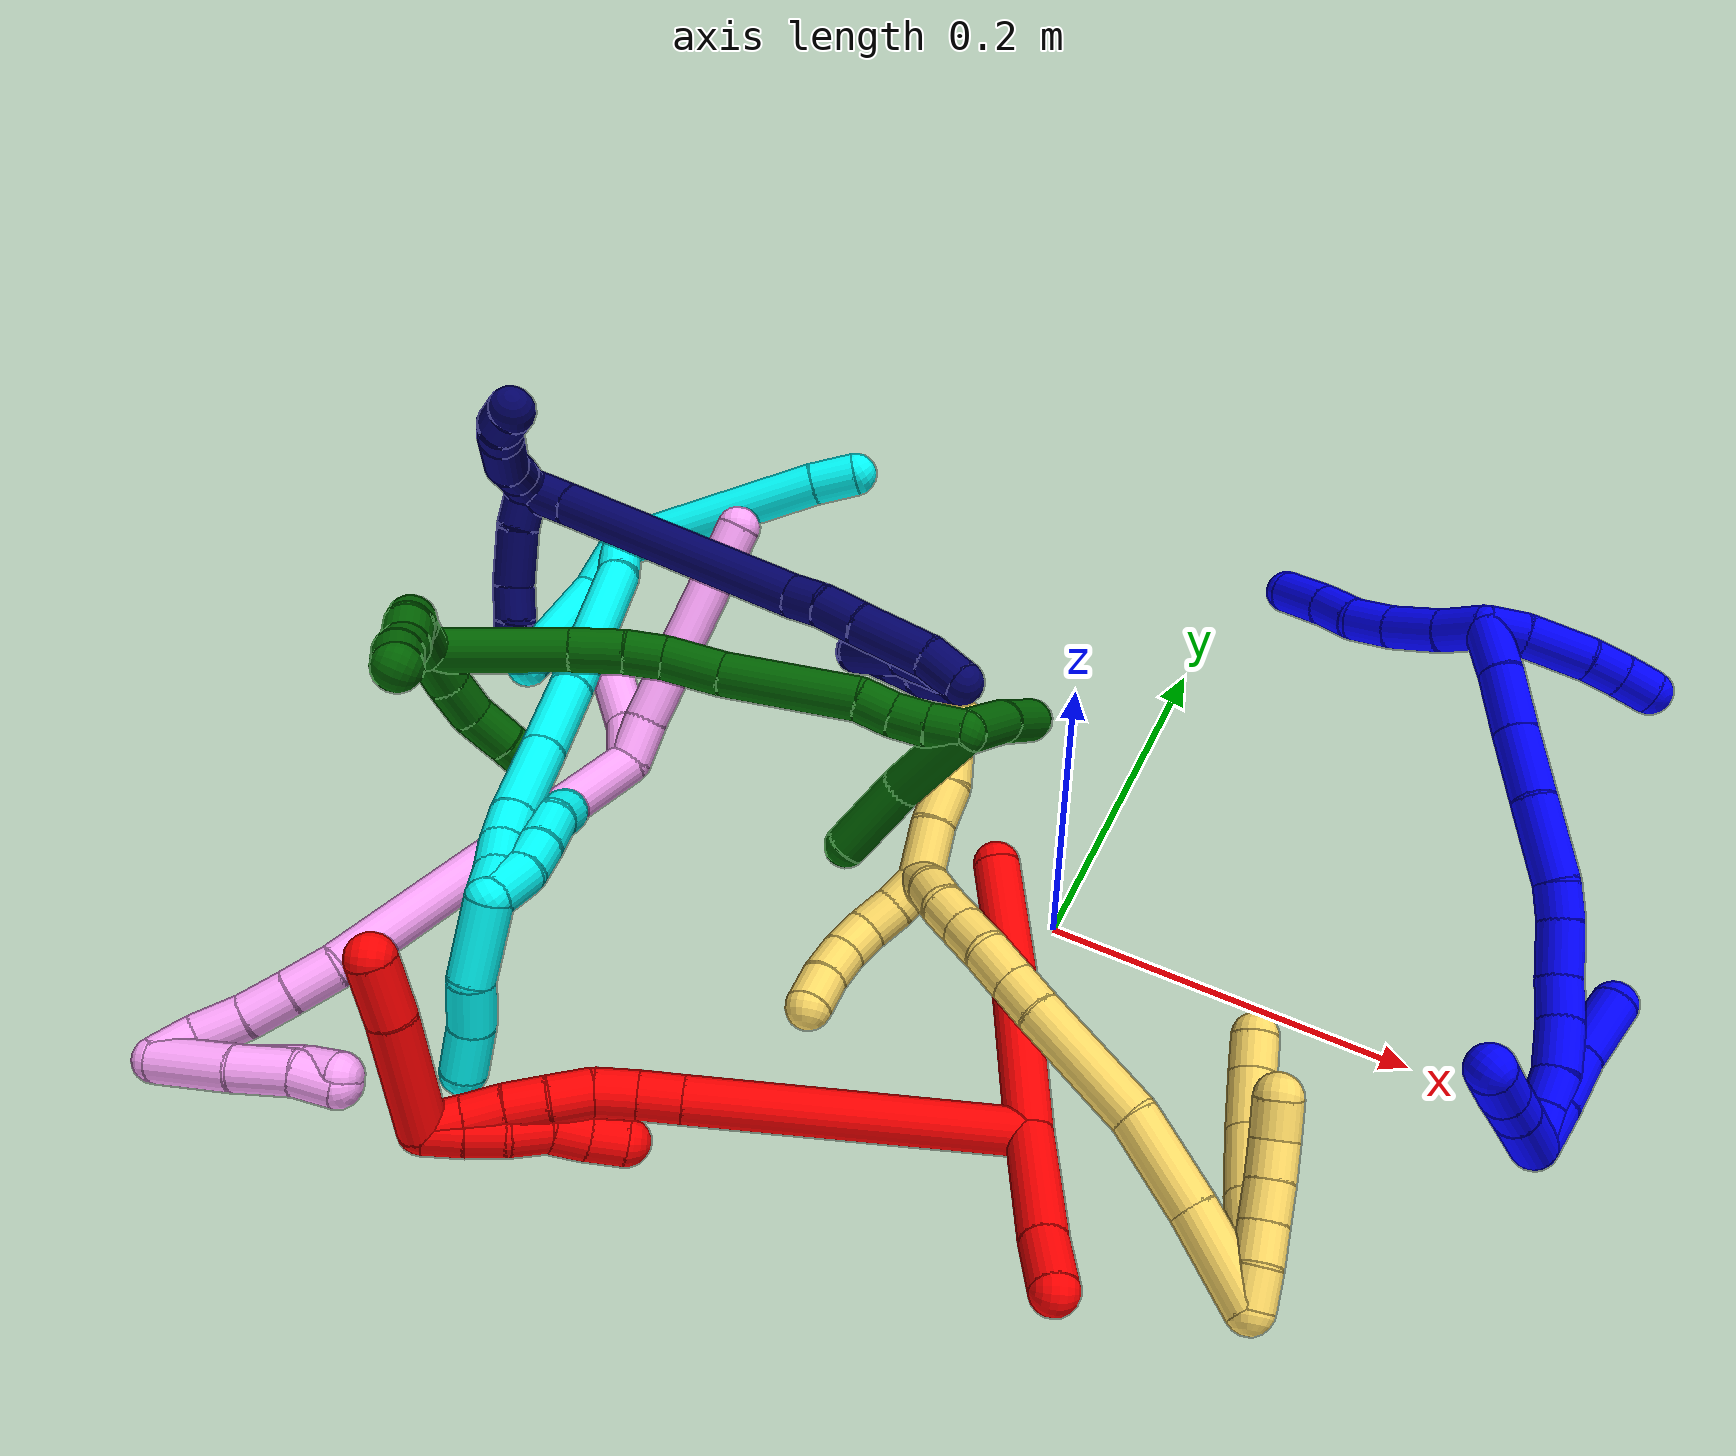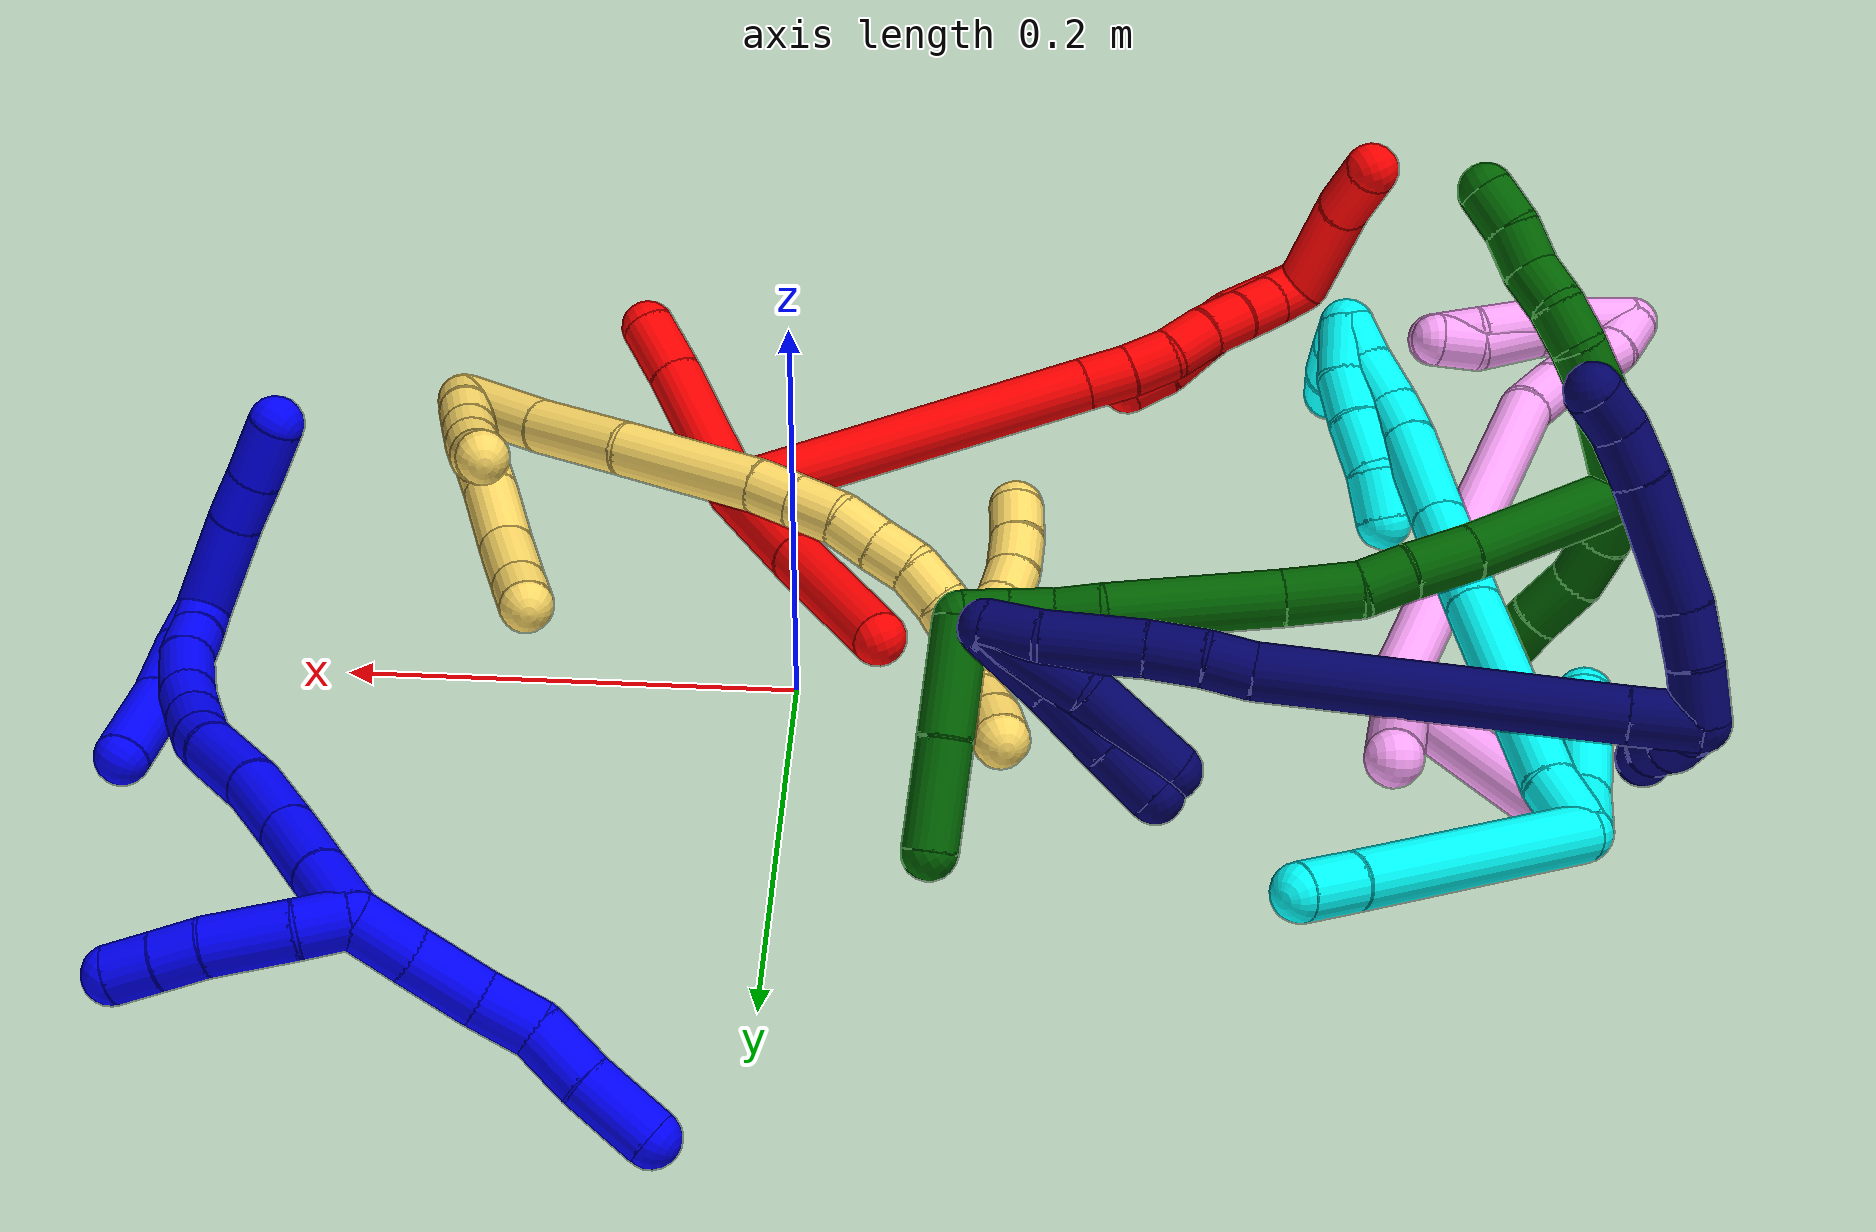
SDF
<sdf version="1.7">
 <world name="default">
  <plugin name="TubeGeneratorPlugin" filename="libtube_generator_plugin.so"/>
  <model name="photoneo_s_sensor">
   <static>1</static>
   <pose>0 0 2 1.57079 1.57079 3.14159</pose>
   <link name="link">
    <inertial><mass>0.1</mass></inertial>
    <sensor name="sensor" type="depth">
     <update_rate>30</update_rate>
     <camera>
      <horizontal_fov>1.22</horizontal_fov>
      <image><width>1920</width><height>1200</height><format>B8G8R8</format></image>
      <clip><near>0.1</near><far>4</far></clip>
      <depth_camera><output>points</output></depth_camera>
     </camera>
     <plugin name="camera_plugin" filename="libgazebo_ros_depth_camera.so">
      <baseline>0.2</baseline>
      <alwaysOn>1</alwaysOn>
      <updateRate>0.0</updateRate>
      <cameraName>camera_ir</cameraName>
      <imageTopicName>/camera/color/image_raw</imageTopicName>
      <cameraInfoTopicName>/camera/color/camera_info</cameraInfoTopicName>
      <depthImageTopicName>/camera/depth/image_raw</depthImageTopicName>
      <depthImageCameraInfoTopicName>/camera/depth/camera_info</depthImageCameraInfoTopicName>
      <pointCloudTopicName>/camera/depth/points</pointCloudTopicName>
      <frameName>fr_optical</frameName>
      <pointCloudCutoff>0.1</pointCloudCutoff>
      <pointCloudCutoffMax>2.0</pointCloudCutoffMax>
      <distortionK1>0</distortionK1>
      <distortionK2>0</distortionK2>
      <distortionK3>0</distortionK3>
      <distortionT1>0</distortionT1>
      <distortionT2>0</distortionT2>
      <CxPrime>0</CxPrime>
      <Cx>0</Cx>
      <Cy>0</Cy>
      <focalLength>0</focalLength>
      <hackBaseline>0</hackBaseline>
     </plugin>
    </sensor>
   </link>
  </model>
  <gravity>0 0 -9.8</gravity>
  <magnetic_field>6e-06 2.3e-05 -4.2e-05</magnetic_field>
  <atmosphere type="adiabatic"/>
  <physics name="default_physics" default="0" type="ode">
   <max_step_size>0.003</max_step_size>
   <real_time_factor>1</real_time_factor>
   <real_time_update_rate>1000</real_time_update_rate>
   <max_contacts>10000</max_contacts>
   <ode>
    <solver>
     <type>quick</type>
     <iters>100</iters>
     <sor>1.3</sor>
     <use_dynamic_moi_rescaling>0</use_dynamic_moi_rescaling>
    </solver>
    <constraints>
     <contact_max_correcting_vel>0</contact_max_correcting_vel>
     <contact_surface_layer>0.001</contact_surface_layer>
     <cfm>0</cfm>
     <erp>0.2</erp>
    </constraints>
   </ode>
  </physics>
  <scene><ambient>0.4 0.4 0.4 1</ambient><background>0.7 0.7 0.7 1</background><shadows>0</shadows></scene>
  <audio><device>default</device></audio>
  <spherical_coordinates>
   <surface_model>EARTH_WGS84</surface_model>
   <latitude_deg>0</latitude_deg>
   <longitude_deg>0</longitude_deg>
   <elevation>0</elevation>
   <heading_deg>0</heading_deg>
  </spherical_coordinates>
  <model name="bin">
   <static>1</static>
   <link name="bottom">
    <collision name="collision-bottom">
     <pose>0 0 -0.01 0 -0 0</pose>
     <geometry><box><size>0.8 0.6 0.02</size></box></geometry>
     <surface>
      <friction><ode><mu>100</mu><mu2>100</mu2></ode></friction>
      <contact><collide_bitmask>65535</collide_bitmask></contact>
     </surface>
    </collision>
   </link>
   <link name="west_wall">
    <collision name="collision-west_wall">
     <pose>-0.41 0 0.1 0 -0 0</pose>
     <geometry><box><size>0.02 0.6 0.2</size></box></geometry>
     <surface>
      <friction><ode><mu>100</mu><mu2>100</mu2></ode></friction>
      <contact><collide_bitmask>65535</collide_bitmask></contact>
     </surface>
    </collision>
   </link>
   <link name="east_wall">
    <collision name="collision-east_wall">
     <pose>0.41 0 0.1 0 -0 0</pose>
     <geometry><box><size>0.02 0.6 0.2</size></box></geometry>
     <surface>
      <friction><ode><mu>100</mu><mu2>100</mu2></ode></friction>
      <contact><collide_bitmask>65535</collide_bitmask></contact>
     </surface>
    </collision>
   </link>
   <link name="south_wall">
    <collision name="collision-south_wall">
     <pose>0 -0.31 0.1 0 -0 0</pose>
     <geometry><box><size>0.8 0.02 0.2</size></box></geometry>
     <surface>
      <friction><ode><mu>100</mu><mu2>100</mu2></ode></friction>
      <contact><collide_bitmask>65535</collide_bitmask></contact>
     </surface>
    </collision>
   </link>
   <link name="north_wall">
    <collision name="collision-north_wall">
     <pose>0 0.31 0.1 0 -0 0</pose>
     <geometry><box><size>0.8 0.02 0.2</size></box></geometry>
     <surface>
      <friction><ode><mu>100</mu><mu2>100</mu2></ode></friction>
      <contact><collide_bitmask>65535</collide_bitmask></contact>
     </surface>
    </collision>
   </link>
  </model>
  <model name="1">
   <static>0</static>
   <link name="1">
    <collision name="collision-cylinder-e_1_2_8">
     <pose>0.005383 0.004339 -0.012065 -2.79635 0.397531 -1.7146</pose>
     <geometry><cylinder><radius>0.0125</radius><length>0.027811</length></cylinder></geometry>
     <surface>
      <friction><ode><mu>1.16</mu><mu2>1.16</mu2><slip1>0</slip1><slip2>0</slip2></ode></friction>
      <contact><ode><kp>1e+06</kp><kd>1</kd><max_vel>0</max_vel><min_depth>0.001</min_depth></ode></contact>
     </surface>
    </collision>
    <visual name="visual-cylinder-e_1_2_8">
     <pose>0.005383 0.004339 -0.012065 -2.79635 0.397531 -1.7146</pose>
     <geometry><cylinder><radius>0.0125</radius><length>0.027811</length></cylinder></geometry>
     <material><ambient>0 0 1 1</ambient></material>
    </visual>
    <collision name="collision-cylinder-e_2_8_9">
     <pose>0.015769 0.012421 -0.039498 -2.90271 0.306296 -1.81986</pose>
     <geometry><cylinder><radius>0.0125</radius><length>0.03318</length></cylinder></geometry>
     <surface>
      <friction><ode><mu>1.16</mu><mu2>1.16</mu2><slip1>0</slip1><slip2>0</slip2></ode></friction>
      <contact><ode><kp>1e+06</kp><kd>1</kd><max_vel>0</max_vel><min_depth>0.001</min_depth></ode></contact>
     </surface>
    </collision>
    <visual name="visual-cylinder-e_2_8_9">
     <pose>0.015769 0.012421 -0.039498 -2.90271 0.306296 -1.81986</pose>
     <geometry><cylinder><radius>0.0125</radius><length>0.03318</length></cylinder></geometry>
     <material><ambient>0 0 1 1</ambient></material>
    </visual>
    <collision name="collision-cylinder-e_3_9_10">
     <pose>0.024048 0.017552 -0.067336 -3.03073 0.255447 -2.32592</pose>
     <geometry><cylinder><radius>0.0125</radius><length>0.025935</length></cylinder></geometry>
     <surface>
      <friction><ode><mu>1.16</mu><mu2>1.16</mu2><slip1>0</slip1><slip2>0</slip2></ode></friction>
      <contact><ode><kp>1e+06</kp><kd>1</kd><max_vel>0</max_vel><min_depth>0.001</min_depth></ode></contact>
     </surface>
    </collision>
    <visual name="visual-cylinder-e_3_9_10">
     <pose>0.024048 0.017552 -0.067336 -3.03073 0.255447 -2.32592</pose>
     <geometry><cylinder><radius>0.0125</radius><length>0.025935</length></cylinder></geometry>
     <material><ambient>0 0 1 1</ambient></material>
    </visual>
    <collision name="collision-cylinder-e_4_10_11">
     <pose>0.026498 0.022349 -0.093447 -2.89671 -0.058731 0.468638</pose>
     <geometry><cylinder><radius>0.0125</radius><length>0.02817</length></cylinder></geometry>
     <surface>
      <friction><ode><mu>1.16</mu><mu2>1.16</mu2><slip1>0</slip1><slip2>0</slip2></ode></friction>
      <contact><ode><kp>1e+06</kp><kd>1</kd><max_vel>0</max_vel><min_depth>0.001</min_depth></ode></contact>
     </surface>
    </collision>
    <visual name="visual-cylinder-e_4_10_11">
     <pose>0.026498 0.022349 -0.093447 -2.89671 -0.058731 0.468638</pose>
     <geometry><cylinder><radius>0.0125</radius><length>0.02817</length></cylinder></geometry>
     <material><ambient>0 0 1 1</ambient></material>
    </visual>
    <collision name="collision-cylinder-e_5_11_6">
     <pose>0.026389 0.02946 -0.124128 -2.92765 0.041164 -0.378795</pose>
     <geometry><cylinder><radius>0.0125</radius><length>0.034904</length></cylinder></geometry>
     <surface>
      <friction><ode><mu>1.16</mu><mu2>1.16</mu2><slip1>0</slip1><slip2>0</slip2></ode></friction>
      <contact><ode><kp>1e+06</kp><kd>1</kd><max_vel>0</max_vel><min_depth>0.001</min_depth></ode></contact>
     </surface>
    </collision>
    <visual name="visual-cylinder-e_5_11_6">
     <pose>0.026389 0.02946 -0.124128 -2.92765 0.041164 -0.378795</pose>
     <geometry><cylinder><radius>0.0125</radius><length>0.034904</length></cylinder></geometry>
     <material><ambient>0 0 1 1</ambient></material>
    </visual>
    <collision name="collision-cylinder-e_1_2_12">
     <pose>-0.006456 0.004685 0.007367 -0.566472 -0.636745 0.191273</pose>
     <geometry><cylinder><radius>0.0125</radius><length>0.021717</length></cylinder></geometry>
     <surface>
      <friction><ode><mu>1.16</mu><mu2>1.16</mu2><slip1>0</slip1><slip2>0</slip2></ode></friction>
      <contact><ode><kp>1e+06</kp><kd>1</kd><max_vel>0</max_vel><min_depth>0.001</min_depth></ode></contact>
     </surface>
    </collision>
    <visual name="visual-cylinder-e_1_2_12">
     <pose>-0.006456 0.004685 0.007367 -0.566472 -0.636745 0.191273</pose>
     <geometry><cylinder><radius>0.0125</radius><length>0.021717</length></cylinder></geometry>
     <material><ambient>0 0 1 1</ambient></material>
    </visual>
    <collision name="collision-cylinder-e_2_12_13">
     <pose>-0.021593 0.018927 0.028413 -0.609777 -0.479689 0.153618</pose>
     <geometry><cylinder><radius>0.0125</radius><length>0.037621</length></cylinder></geometry>
     <surface>
      <friction><ode><mu>1.16</mu><mu2>1.16</mu2><slip1>0</slip1><slip2>0</slip2></ode></friction>
      <contact><ode><kp>1e+06</kp><kd>1</kd><max_vel>0</max_vel><min_depth>0.001</min_depth></ode></contact>
     </surface>
    </collision>
    <visual name="visual-cylinder-e_2_12_13">
     <pose>-0.021593 0.018927 0.028413 -0.609777 -0.479689 0.153618</pose>
     <geometry><cylinder><radius>0.0125</radius><length>0.037621</length></cylinder></geometry>
     <material><ambient>0 0 1 1</ambient></material>
    </visual>
    <collision name="collision-cylinder-e_3_13_14">
     <pose>-0.034394 0.034623 0.048836 -0.738588 -0.424354 0.166372</pose>
     <geometry><cylinder><radius>0.0125</radius><length>0.020014</length></cylinder></geometry>
     <surface>
      <friction><ode><mu>1.16</mu><mu2>1.16</mu2><slip1>0</slip1><slip2>0</slip2></ode></friction>
      <contact><ode><kp>1e+06</kp><kd>1</kd><max_vel>0</max_vel><min_depth>0.001</min_depth></ode></contact>
     </surface>
    </collision>
    <visual name="visual-cylinder-e_3_13_14">
     <pose>-0.034394 0.034623 0.048836 -0.738588 -0.424354 0.166372</pose>
     <geometry><cylinder><radius>0.0125</radius><length>0.020014</length></cylinder></geometry>
     <material><ambient>0 0 1 1</ambient></material>
    </visual>
    <collision name="collision-cylinder-e_4_14_5">
     <pose>-0.042259 0.047309 0.062631 -0.748187 -0.371138 0.147131</pose>
     <geometry><cylinder><radius>0.0125</radius><length>0.020649</length></cylinder></geometry>
     <surface>
      <friction><ode><mu>1.16</mu><mu2>1.16</mu2><slip1>0</slip1><slip2>0</slip2></ode></friction>
      <contact><ode><kp>1e+06</kp><kd>1</kd><max_vel>0</max_vel><min_depth>0.001</min_depth></ode></contact>
     </surface>
    </collision>
    <visual name="visual-cylinder-e_4_14_5">
     <pose>-0.042259 0.047309 0.062631 -0.748187 -0.371138 0.147131</pose>
     <geometry><cylinder><radius>0.0125</radius><length>0.020649</length></cylinder></geometry>
     <material><ambient>0 0 1 1</ambient></material>
    </visual>
    <collision name="collision-cylinder-e_1_2_15">
     <pose>0.008694 0.002666 0.012994 -0.202336 0.580165 -0.060586</pose>
     <geometry><cylinder><radius>0.0125</radius><length>0.03172</length></cylinder></geometry>
     <surface>
      <friction><ode><mu>1.16</mu><mu2>1.16</mu2><slip1>0</slip1><slip2>0</slip2></ode></friction>
      <contact><ode><kp>1e+06</kp><kd>1</kd><max_vel>0</max_vel><min_depth>0.001</min_depth></ode></contact>
     </surface>
    </collision>
    <visual name="visual-cylinder-e_1_2_15">
     <pose>0.008694 0.002666 0.012994 -0.202336 0.580165 -0.060586</pose>
     <geometry><cylinder><radius>0.0125</radius><length>0.03172</length></cylinder></geometry>
     <material><ambient>0 0 1 1</ambient></material>
    </visual>
    <collision name="collision-cylinder-e_2_15_16">
     <pose>0.028412 0.009566 0.040461 -0.284657 0.631298 -0.093524</pose>
     <geometry><cylinder><radius>0.0125</radius><length>0.03736</length></cylinder></geometry>
     <surface>
      <friction><ode><mu>1.16</mu><mu2>1.16</mu2><slip1>0</slip1><slip2>0</slip2></ode></friction>
      <contact><ode><kp>1e+06</kp><kd>1</kd><max_vel>0</max_vel><min_depth>0.001</min_depth></ode></contact>
     </surface>
    </collision>
    <visual name="visual-cylinder-e_2_15_16">
     <pose>0.028412 0.009566 0.040461 -0.284657 0.631298 -0.093524</pose>
     <geometry><cylinder><radius>0.0125</radius><length>0.03736</length></cylinder></geometry>
     <material><ambient>0 0 1 1</ambient></material>
    </visual>
    <collision name="collision-cylinder-e_3_16_17">
     <pose>0.051068 0.018603 0.070889 -0.292347 0.609423 -0.092539</pose>
     <geometry><cylinder><radius>0.0125</radius><length>0.04064</length></cylinder></geometry>
     <surface>
      <friction><ode><mu>1.16</mu><mu2>1.16</mu2><slip1>0</slip1><slip2>0</slip2></ode></friction>
      <contact><ode><kp>1e+06</kp><kd>1</kd><max_vel>0</max_vel><min_depth>0.001</min_depth></ode></contact>
     </surface>
    </collision>
    <visual name="visual-cylinder-e_3_16_17">
     <pose>0.051068 0.018603 0.070889 -0.292347 0.609423 -0.092539</pose>
     <geometry><cylinder><radius>0.0125</radius><length>0.04064</length></cylinder></geometry>
     <material><ambient>0 0 1 1</ambient></material>
    </visual>
    <collision name="collision-cylinder-e_4_17_18">
     <pose>0.075448 0.031899 0.104692 -0.444211 0.572822 -0.132823</pose>
     <geometry><cylinder><radius>0.0125</radius><length>0.047042</length></cylinder></geometry>
     <surface>
      <friction><ode><mu>1.16</mu><mu2>1.16</mu2><slip1>0</slip1><slip2>0</slip2></ode></friction>
      <contact><ode><kp>1e+06</kp><kd>1</kd><max_vel>0</max_vel><min_depth>0.001</min_depth></ode></contact>
     </surface>
    </collision>
    <visual name="visual-cylinder-e_4_17_18">
     <pose>0.075448 0.031899 0.104692 -0.444211 0.572822 -0.132823</pose>
     <geometry><cylinder><radius>0.0125</radius><length>0.047042</length></cylinder></geometry>
     <material><ambient>0 0 1 1</ambient></material>
    </visual>
    <collision name="collision-cylinder-e_5_18_19">
     <pose>0.094621 0.044796 0.128878 -0.607091 0.694304 -0.22569</pose>
     <geometry><cylinder><radius>0.0125</radius><length>0.020082</length></cylinder></geometry>
     <surface>
      <friction><ode><mu>1.16</mu><mu2>1.16</mu2><slip1>0</slip1><slip2>0</slip2></ode></friction>
      <contact><ode><kp>1e+06</kp><kd>1</kd><max_vel>0</max_vel><min_depth>0.001</min_depth></ode></contact>
     </surface>
    </collision>
    <visual name="visual-cylinder-e_5_18_19">
     <pose>0.094621 0.044796 0.128878 -0.607091 0.694304 -0.22569</pose>
     <geometry><cylinder><radius>0.0125</radius><length>0.020082</length></cylinder></geometry>
     <material><ambient>0 0 1 1</ambient></material>
    </visual>
    <collision name="collision-cylinder-e_6_19_20">
     <pose>0.112304 0.054718 0.14388 -0.567268 0.831122 -0.255843</pose>
     <geometry><cylinder><radius>0.0125</radius><length>0.030484</length></cylinder></geometry>
     <surface>
      <friction><ode><mu>1.16</mu><mu2>1.16</mu2><slip1>0</slip1><slip2>0</slip2></ode></friction>
      <contact><ode><kp>1e+06</kp><kd>1</kd><max_vel>0</max_vel><min_depth>0.001</min_depth></ode></contact>
     </surface>
    </collision>
    <visual name="visual-cylinder-e_6_19_20">
     <pose>0.112304 0.054718 0.14388 -0.567268 0.831122 -0.255843</pose>
     <geometry><cylinder><radius>0.0125</radius><length>0.030484</length></cylinder></geometry>
     <material><ambient>0 0 1 1</ambient></material>
    </visual>
    <collision name="collision-cylinder-e_7_20_21">
     <pose>0.132095 0.062764 0.160044 -0.324765 0.822945 -0.142738</pose>
     <geometry><cylinder><radius>0.0125</radius><length>0.023273</length></cylinder></geometry>
     <surface>
      <friction><ode><mu>1.16</mu><mu2>1.16</mu2><slip1>0</slip1><slip2>0</slip2></ode></friction>
      <contact><ode><kp>1e+06</kp><kd>1</kd><max_vel>0</max_vel><min_depth>0.001</min_depth></ode></contact>
     </surface>
    </collision>
    <visual name="visual-cylinder-e_7_20_21">
     <pose>0.132095 0.062764 0.160044 -0.324765 0.822945 -0.142738</pose>
     <geometry><cylinder><radius>0.0125</radius><length>0.023273</length></cylinder></geometry>
     <material><ambient>0 0 1 1</ambient></material>
    </visual>
    <collision name="collision-cylinder-e_8_21_22">
     <pose>0.152193 0.066702 0.176217 -0.161493 0.921106 -0.080254</pose>
     <geometry><cylinder><radius>0.0125</radius><length>0.029053</length></cylinder></geometry>
     <surface>
      <friction><ode><mu>1.16</mu><mu2>1.16</mu2><slip1>0</slip1><slip2>0</slip2></ode></friction>
      <contact><ode><kp>1e+06</kp><kd>1</kd><max_vel>0</max_vel><min_depth>0.001</min_depth></ode></contact>
     </surface>
    </collision>
    <visual name="visual-cylinder-e_8_21_22">
     <pose>0.152193 0.066702 0.176217 -0.161493 0.921106 -0.080254</pose>
     <geometry><cylinder><radius>0.0125</radius><length>0.029053</length></cylinder></geometry>
     <material><ambient>0 0 1 1</ambient></material>
    </visual>
    <collision name="collision-cylinder-e_9_22_23">
     <pose>0.172954 0.068296 0.189005 -0.044119 1.14967 -0.028583</pose>
     <geometry><cylinder><radius>0.0125</radius><length>0.020149</length></cylinder></geometry>
     <surface>
      <friction><ode><mu>1.16</mu><mu2>1.16</mu2><slip1>0</slip1><slip2>0</slip2></ode></friction>
      <contact><ode><kp>1e+06</kp><kd>1</kd><max_vel>0</max_vel><min_depth>0.001</min_depth></ode></contact>
     </surface>
    </collision>
    <visual name="visual-cylinder-e_9_22_23">
     <pose>0.172954 0.068296 0.189005 -0.044119 1.14967 -0.028583</pose>
     <geometry><cylinder><radius>0.0125</radius><length>0.020149</length></cylinder></geometry>
     <material><ambient>0 0 1 1</ambient></material>
    </visual>
    <collision name="collision-cylinder-e_10_23_1">
     <pose>0.191175 0.0689 0.197629 -0.09325 1.10569 -0.057563</pose>
     <geometry><cylinder><radius>0.0125</radius><length>0.020198</length></cylinder></geometry>
     <surface>
      <friction><ode><mu>1.16</mu><mu2>1.16</mu2><slip1>0</slip1><slip2>0</slip2></ode></friction>
      <contact><ode><kp>1e+06</kp><kd>1</kd><max_vel>0</max_vel><min_depth>0.001</min_depth></ode></contact>
     </surface>
    </collision>
    <visual name="visual-cylinder-e_10_23_1">
     <pose>0.191175 0.0689 0.197629 -0.09325 1.10569 -0.057563</pose>
     <geometry><cylinder><radius>0.0125</radius><length>0.020198</length></cylinder></geometry>
     <material><ambient>0 0 1 1</ambient></material>
    </visual>
    <collision name="collision-cylinder-e_1_1_24">
     <pose>0.187629 0.071426 0.197892 -2.68152 -1.21025 2.48869</pose>
     <geometry><cylinder><radius>0.0125</radius><length>0.026872</length></cylinder></geometry>
     <surface>
      <friction><ode><mu>1.16</mu><mu2>1.16</mu2><slip1>0</slip1><slip2>0</slip2></ode></friction>
      <contact><ode><kp>1e+06</kp><kd>1</kd><max_vel>0</max_vel><min_depth>0.001</min_depth></ode></contact>
     </surface>
    </collision>
    <visual name="visual-cylinder-e_1_1_24">
     <pose>0.187629 0.071426 0.197892 -2.68152 -1.21025 2.48869</pose>
     <geometry><cylinder><radius>0.0125</radius><length>0.026872</length></cylinder></geometry>
     <material><ambient>0 0 1 1</ambient></material>
    </visual>
    <collision name="collision-cylinder-e_2_24_25">
     <pose>0.159889 0.076398 0.187685 -2.69319 -1.15965 2.47147</pose>
     <geometry><cylinder><radius>0.0125</radius><length>0.033095</length></cylinder></geometry>
     <surface>
      <friction><ode><mu>1.16</mu><mu2>1.16</mu2><slip1>0</slip1><slip2>0</slip2></ode></friction>
      <contact><ode><kp>1e+06</kp><kd>1</kd><max_vel>0</max_vel><min_depth>0.001</min_depth></ode></contact>
     </surface>
    </collision>
    <visual name="visual-cylinder-e_2_24_25">
     <pose>0.159889 0.076398 0.187685 -2.69319 -1.15965 2.47147</pose>
     <geometry><cylinder><radius>0.0125</radius><length>0.033095</length></cylinder></geometry>
     <material><ambient>0 0 1 1</ambient></material>
    </visual>
    <collision name="collision-cylinder-e_3_25_4">
     <pose>0.125726 0.082949 0.176598 -2.51858 -1.24987 2.30196</pose>
     <geometry><cylinder><radius>0.0125</radius><length>0.040033</length></cylinder></geometry>
     <surface>
      <friction><ode><mu>1.16</mu><mu2>1.16</mu2><slip1>0</slip1><slip2>0</slip2></ode></friction>
      <contact><ode><kp>1e+06</kp><kd>1</kd><max_vel>0</max_vel><min_depth>0.001</min_depth></ode></contact>
     </surface>
    </collision>
    <visual name="visual-cylinder-e_3_25_4">
     <pose>0.125726 0.082949 0.176598 -2.51858 -1.24987 2.30196</pose>
     <geometry><cylinder><radius>0.0125</radius><length>0.040033</length></cylinder></geometry>
     <material><ambient>0 0 1 1</ambient></material>
    </visual>
    <collision name="collision-cylinder-e_1_1_26">
     <pose>0.203893 0.045421 0.202814 1.54256 0.153209 0.148959</pose>
     <geometry><cylinder><radius>0.0125</radius><length>0.048387</length></cylinder></geometry>
     <surface>
      <friction><ode><mu>1.16</mu><mu2>1.16</mu2><slip1>0</slip1><slip2>0</slip2></ode></friction>
      <contact><ode><kp>1e+06</kp><kd>1</kd><max_vel>0</max_vel><min_depth>0.001</min_depth></ode></contact>
     </surface>
    </collision>
    <visual name="visual-cylinder-e_1_1_26">
     <pose>0.203893 0.045421 0.202814 1.54256 0.153209 0.148959</pose>
     <geometry><cylinder><radius>0.0125</radius><length>0.048387</length></cylinder></geometry>
     <material><ambient>0 0 1 1</ambient></material>
    </visual>
    <collision name="collision-cylinder-e_2_26_27">
     <pose>0.209261 0.010087 0.203066 1.60781 0.145391 0.150854</pose>
     <geometry><cylinder><radius>0.0125</radius><length>0.023127</length></cylinder></geometry>
     <surface>
      <friction><ode><mu>1.16</mu><mu2>1.16</mu2><slip1>0</slip1><slip2>0</slip2></ode></friction>
      <contact><ode><kp>1e+06</kp><kd>1</kd><max_vel>0</max_vel><min_depth>0.001</min_depth></ode></contact>
     </surface>
    </collision>
    <visual name="visual-cylinder-e_2_26_27">
     <pose>0.209261 0.010087 0.203066 1.60781 0.145391 0.150854</pose>
     <geometry><cylinder><radius>0.0125</radius><length>0.023127</length></cylinder></geometry>
     <material><ambient>0 0 1 1</ambient></material>
    </visual>
    <collision name="collision-cylinder-e_3_27_3">
     <pose>0.212671 -0.015482 0.202413 1.58702 0.122114 0.124106</pose>
     <geometry><cylinder><radius>0.0125</radius><length>0.028486</length></cylinder></geometry>
     <surface>
      <friction><ode><mu>1.16</mu><mu2>1.16</mu2><slip1>0</slip1><slip2>0</slip2></ode></friction>
      <contact><ode><kp>1e+06</kp><kd>1</kd><max_vel>0</max_vel><min_depth>0.001</min_depth></ode></contact>
     </surface>
    </collision>
    <visual name="visual-cylinder-e_3_27_3">
     <pose>0.212671 -0.015482 0.202413 1.58702 0.122114 0.124106</pose>
     <geometry><cylinder><radius>0.0125</radius><length>0.028486</length></cylinder></geometry>
     <material><ambient>0 0 1 1</ambient></material>
    </visual>
    <collision name="collision-sphere-3">
     <pose>0.214406 -0.029617 0.202184 0 -0 0</pose>
     <geometry><sphere><radius>0.0125</radius></sphere></geometry>
     <surface>
      <friction><ode><mu>1.16</mu><mu2>1.16</mu2><slip1>0</slip1><slip2>0</slip2></ode></friction>
      <contact><ode><kp>1e+06</kp><kd>1</kd><max_vel>0</max_vel><min_depth>0.001</min_depth></ode></contact>
     </surface>
    </collision>
    <visual name="visual-sphere-3">
     <pose>0.214406 -0.029617 0.202184 0 -0 0</pose>
     <geometry><sphere><radius>0.0125</radius></sphere></geometry>
     <material><ambient>0 0 1 1</ambient></material>
    </visual>
    <collision name="collision-sphere-27">
     <pose>0.210936 -0.001347 0.202642 0 -0 0</pose>
     <geometry><sphere><radius>0.0125</radius></sphere></geometry>
     <surface>
      <friction><ode><mu>1.16</mu><mu2>1.16</mu2><slip1>0</slip1><slip2>0</slip2></ode></friction>
      <contact><ode><kp>1e+06</kp><kd>1</kd><max_vel>0</max_vel><min_depth>0.001</min_depth></ode></contact>
     </surface>
    </collision>
    <visual name="visual-sphere-27">
     <pose>0.210936 -0.001347 0.202642 0 -0 0</pose>
     <geometry><sphere><radius>0.0125</radius></sphere></geometry>
     <material><ambient>0 0 1 1</ambient></material>
    </visual>
    <collision name="collision-sphere-26">
     <pose>0.207586 0.021521 0.203489 0 -0 0</pose>
     <geometry><sphere><radius>0.0125</radius></sphere></geometry>
     <surface>
      <friction><ode><mu>1.16</mu><mu2>1.16</mu2><slip1>0</slip1><slip2>0</slip2></ode></friction>
      <contact><ode><kp>1e+06</kp><kd>1</kd><max_vel>0</max_vel><min_depth>0.001</min_depth></ode></contact>
     </surface>
    </collision>
    <visual name="visual-sphere-26">
     <pose>0.207586 0.021521 0.203489 0 -0 0</pose>
     <geometry><sphere><radius>0.0125</radius></sphere></geometry>
     <material><ambient>0 0 1 1</ambient></material>
    </visual>
    <collision name="collision-sphere-4">
     <pose>0.106731 0.086634 0.17147 0 -0 0</pose>
     <geometry><sphere><radius>0.0125</radius></sphere></geometry>
     <surface>
      <friction><ode><mu>1.16</mu><mu2>1.16</mu2><slip1>0</slip1><slip2>0</slip2></ode></friction>
      <contact><ode><kp>1e+06</kp><kd>1</kd><max_vel>0</max_vel><min_depth>0.001</min_depth></ode></contact>
     </surface>
    </collision>
    <visual name="visual-sphere-4">
     <pose>0.106731 0.086634 0.17147 0 -0 0</pose>
     <geometry><sphere><radius>0.0125</radius></sphere></geometry>
     <material><ambient>0 0 1 1</ambient></material>
    </visual>
    <collision name="collision-sphere-25">
     <pose>0.14472 0.079265 0.181726 0 -0 0</pose>
     <geometry><sphere><radius>0.0125</radius></sphere></geometry>
     <surface>
      <friction><ode><mu>1.16</mu><mu2>1.16</mu2><slip1>0</slip1><slip2>0</slip2></ode></friction>
      <contact><ode><kp>1e+06</kp><kd>1</kd><max_vel>0</max_vel><min_depth>0.001</min_depth></ode></contact>
     </surface>
    </collision>
    <visual name="visual-sphere-25">
     <pose>0.14472 0.079265 0.181726 0 -0 0</pose>
     <geometry><sphere><radius>0.0125</radius></sphere></geometry>
     <material><ambient>0 0 1 1</ambient></material>
    </visual>
    <collision name="collision-sphere-24">
     <pose>0.175057 0.073531 0.193645 0 -0 0</pose>
     <geometry><sphere><radius>0.0125</radius></sphere></geometry>
     <surface>
      <friction><ode><mu>1.16</mu><mu2>1.16</mu2><slip1>0</slip1><slip2>0</slip2></ode></friction>
      <contact><ode><kp>1e+06</kp><kd>1</kd><max_vel>0</max_vel><min_depth>0.001</min_depth></ode></contact>
     </surface>
    </collision>
    <visual name="visual-sphere-24">
     <pose>0.175057 0.073531 0.193645 0 -0 0</pose>
     <geometry><sphere><radius>0.0125</radius></sphere></geometry>
     <material><ambient>0 0 1 1</ambient></material>
    </visual>
    <collision name="collision-sphere-1">
     <pose>0.200201 0.069322 0.202139 0 -0 0</pose>
     <geometry><sphere><radius>0.0125</radius></sphere></geometry>
     <surface>
      <friction><ode><mu>1.16</mu><mu2>1.16</mu2><slip1>0</slip1><slip2>0</slip2></ode></friction>
      <contact><ode><kp>1e+06</kp><kd>1</kd><max_vel>0</max_vel><min_depth>0.001</min_depth></ode></contact>
     </surface>
    </collision>
    <visual name="visual-sphere-1">
     <pose>0.200201 0.069322 0.202139 0 -0 0</pose>
     <geometry><sphere><radius>0.0125</radius></sphere></geometry>
     <material><ambient>0 0 1 1</ambient></material>
    </visual>
    <collision name="collision-sphere-23">
     <pose>0.182148 0.068478 0.193119 0 -0 0</pose>
     <geometry><sphere><radius>0.0125</radius></sphere></geometry>
     <surface>
      <friction><ode><mu>1.16</mu><mu2>1.16</mu2><slip1>0</slip1><slip2>0</slip2></ode></friction>
      <contact><ode><kp>1e+06</kp><kd>1</kd><max_vel>0</max_vel><min_depth>0.001</min_depth></ode></contact>
     </surface>
    </collision>
    <visual name="visual-sphere-23">
     <pose>0.182148 0.068478 0.193119 0 -0 0</pose>
     <geometry><sphere><radius>0.0125</radius></sphere></geometry>
     <material><ambient>0 0 1 1</ambient></material>
    </visual>
    <collision name="collision-sphere-22">
     <pose>0.16376 0.068115 0.18489 0 -0 0</pose>
     <geometry><sphere><radius>0.0125</radius></sphere></geometry>
     <surface>
      <friction><ode><mu>1.16</mu><mu2>1.16</mu2><slip1>0</slip1><slip2>0</slip2></ode></friction>
      <contact><ode><kp>1e+06</kp><kd>1</kd><max_vel>0</max_vel><min_depth>0.001</min_depth></ode></contact>
     </surface>
    </collision>
    <visual name="visual-sphere-22">
     <pose>0.16376 0.068115 0.18489 0 -0 0</pose>
     <geometry><sphere><radius>0.0125</radius></sphere></geometry>
     <material><ambient>0 0 1 1</ambient></material>
    </visual>
    <collision name="collision-sphere-21">
     <pose>0.140626 0.065289 0.167544 0 -0 0</pose>
     <geometry><sphere><radius>0.0125</radius></sphere></geometry>
     <surface>
      <friction><ode><mu>1.16</mu><mu2>1.16</mu2><slip1>0</slip1><slip2>0</slip2></ode></friction>
      <contact><ode><kp>1e+06</kp><kd>1</kd><max_vel>0</max_vel><min_depth>0.001</min_depth></ode></contact>
     </surface>
    </collision>
    <visual name="visual-sphere-21">
     <pose>0.140626 0.065289 0.167544 0 -0 0</pose>
     <geometry><sphere><radius>0.0125</radius></sphere></geometry>
     <material><ambient>0 0 1 1</ambient></material>
    </visual>
    <collision name="collision-sphere-6">
     <pose>0.027108 0.033162 -0.141168 0 -0 0</pose>
     <geometry><sphere><radius>0.0125</radius></sphere></geometry>
     <surface>
      <friction><ode><mu>1.16</mu><mu2>1.16</mu2><slip1>0</slip1><slip2>0</slip2></ode></friction>
      <contact><ode><kp>1e+06</kp><kd>1</kd><max_vel>0</max_vel><min_depth>0.001</min_depth></ode></contact>
     </surface>
    </collision>
    <visual name="visual-sphere-6">
     <pose>0.027108 0.033162 -0.141168 0 -0 0</pose>
     <geometry><sphere><radius>0.0125</radius></sphere></geometry>
     <material><ambient>0 0 1 1</ambient></material>
    </visual>
    <collision name="collision-sphere-11">
     <pose>0.025671 0.025757 -0.107088 0 -0 0</pose>
     <geometry><sphere><radius>0.0125</radius></sphere></geometry>
     <surface>
      <friction><ode><mu>1.16</mu><mu2>1.16</mu2><slip1>0</slip1><slip2>0</slip2></ode></friction>
      <contact><ode><kp>1e+06</kp><kd>1</kd><max_vel>0</max_vel><min_depth>0.001</min_depth></ode></contact>
     </surface>
    </collision>
    <visual name="visual-sphere-11">
     <pose>0.025671 0.025757 -0.107088 0 -0 0</pose>
     <geometry><sphere><radius>0.0125</radius></sphere></geometry>
     <material><ambient>0 0 1 1</ambient></material>
    </visual>
    <collision name="collision-sphere-10">
     <pose>0.027325 0.01894 -0.079806 0 -0 0</pose>
     <geometry><sphere><radius>0.0125</radius></sphere></geometry>
     <surface>
      <friction><ode><mu>1.16</mu><mu2>1.16</mu2><slip1>0</slip1><slip2>0</slip2></ode></friction>
      <contact><ode><kp>1e+06</kp><kd>1</kd><max_vel>0</max_vel><min_depth>0.001</min_depth></ode></contact>
     </surface>
    </collision>
    <visual name="visual-sphere-10">
     <pose>0.027325 0.01894 -0.079806 0 -0 0</pose>
     <geometry><sphere><radius>0.0125</radius></sphere></geometry>
     <material><ambient>0 0 1 1</ambient></material>
    </visual>
    <collision name="collision-sphere-9">
     <pose>0.020772 0.016164 -0.054867 0 -0 0</pose>
     <geometry><sphere><radius>0.0125</radius></sphere></geometry>
     <surface>
      <friction><ode><mu>1.16</mu><mu2>1.16</mu2><slip1>0</slip1><slip2>0</slip2></ode></friction>
      <contact><ode><kp>1e+06</kp><kd>1</kd><max_vel>0</max_vel><min_depth>0.001</min_depth></ode></contact>
     </surface>
    </collision>
    <visual name="visual-sphere-9">
     <pose>0.020772 0.016164 -0.054867 0 -0 0</pose>
     <geometry><sphere><radius>0.0125</radius></sphere></geometry>
     <material><ambient>0 0 1 1</ambient></material>
    </visual>
    <collision name="collision-sphere-2">
     <geometry><sphere><radius>0.0125</radius></sphere></geometry>
     <surface>
      <friction><ode><mu>1.16</mu><mu2>1.16</mu2><slip1>0</slip1><slip2>0</slip2></ode></friction>
      <contact><ode><kp>1e+06</kp><kd>1</kd><max_vel>0</max_vel><min_depth>0.001</min_depth></ode></contact>
     </surface>
    </collision>
    <visual name="visual-sphere-2">
     <geometry><sphere><radius>0.0125</radius></sphere></geometry>
     <material><ambient>0 0 1 1</ambient></material>
    </visual>
    <collision name="collision-sphere-19">
     <pose>0.101045 0.049198 0.135215 0 -0 0</pose>
     <geometry><sphere><radius>0.0125</radius></sphere></geometry>
     <surface>
      <friction><ode><mu>1.16</mu><mu2>1.16</mu2><slip1>0</slip1><slip2>0</slip2></ode></friction>
      <contact><ode><kp>1e+06</kp><kd>1</kd><max_vel>0</max_vel><min_depth>0.001</min_depth></ode></contact>
     </surface>
    </collision>
    <visual name="visual-sphere-19">
     <pose>0.101045 0.049198 0.135215 0 -0 0</pose>
     <geometry><sphere><radius>0.0125</radius></sphere></geometry>
     <material><ambient>0 0 1 1</ambient></material>
    </visual>
    <collision name="collision-sphere-8">
     <pose>0.010767 0.008678 -0.024129 0 -0 0</pose>
     <geometry><sphere><radius>0.0125</radius></sphere></geometry>
     <surface>
      <friction><ode><mu>1.16</mu><mu2>1.16</mu2><slip1>0</slip1><slip2>0</slip2></ode></friction>
      <contact><ode><kp>1e+06</kp><kd>1</kd><max_vel>0</max_vel><min_depth>0.001</min_depth></ode></contact>
     </surface>
    </collision>
    <visual name="visual-sphere-8">
     <pose>0.010767 0.008678 -0.024129 0 -0 0</pose>
     <geometry><sphere><radius>0.0125</radius></sphere></geometry>
     <material><ambient>0 0 1 1</ambient></material>
    </visual>
    <collision name="collision-sphere-12">
     <pose>-0.012912 0.009371 0.014733 0 -0 0</pose>
     <geometry><sphere><radius>0.0125</radius></sphere></geometry>
     <surface>
      <friction><ode><mu>1.16</mu><mu2>1.16</mu2><slip1>0</slip1><slip2>0</slip2></ode></friction>
      <contact><ode><kp>1e+06</kp><kd>1</kd><max_vel>0</max_vel><min_depth>0.001</min_depth></ode></contact>
     </surface>
    </collision>
    <visual name="visual-sphere-12">
     <pose>-0.012912 0.009371 0.014733 0 -0 0</pose>
     <geometry><sphere><radius>0.0125</radius></sphere></geometry>
     <material><ambient>0 0 1 1</ambient></material>
    </visual>
    <collision name="collision-sphere-13">
     <pose>-0.030274 0.028484 0.042093 0 -0 0</pose>
     <geometry><sphere><radius>0.0125</radius></sphere></geometry>
     <surface>
      <friction><ode><mu>1.16</mu><mu2>1.16</mu2><slip1>0</slip1><slip2>0</slip2></ode></friction>
      <contact><ode><kp>1e+06</kp><kd>1</kd><max_vel>0</max_vel><min_depth>0.001</min_depth></ode></contact>
     </surface>
    </collision>
    <visual name="visual-sphere-13">
     <pose>-0.030274 0.028484 0.042093 0 -0 0</pose>
     <geometry><sphere><radius>0.0125</radius></sphere></geometry>
     <material><ambient>0 0 1 1</ambient></material>
    </visual>
    <collision name="collision-sphere-14">
     <pose>-0.038515 0.040763 0.055579 0 -0 0</pose>
     <geometry><sphere><radius>0.0125</radius></sphere></geometry>
     <surface>
      <friction><ode><mu>1.16</mu><mu2>1.16</mu2><slip1>0</slip1><slip2>0</slip2></ode></friction>
      <contact><ode><kp>1e+06</kp><kd>1</kd><max_vel>0</max_vel><min_depth>0.001</min_depth></ode></contact>
     </surface>
    </collision>
    <visual name="visual-sphere-14">
     <pose>-0.038515 0.040763 0.055579 0 -0 0</pose>
     <geometry><sphere><radius>0.0125</radius></sphere></geometry>
     <material><ambient>0 0 1 1</ambient></material>
    </visual>
    <collision name="collision-sphere-5">
     <pose>-0.046004 0.053854 0.069683 0 -0 0</pose>
     <geometry><sphere><radius>0.0125</radius></sphere></geometry>
     <surface>
      <friction><ode><mu>1.16</mu><mu2>1.16</mu2><slip1>0</slip1><slip2>0</slip2></ode></friction>
      <contact><ode><kp>1e+06</kp><kd>1</kd><max_vel>0</max_vel><min_depth>0.001</min_depth></ode></contact>
     </surface>
    </collision>
    <visual name="visual-sphere-5">
     <pose>-0.046004 0.053854 0.069683 0 -0 0</pose>
     <geometry><sphere><radius>0.0125</radius></sphere></geometry>
     <material><ambient>0 0 1 1</ambient></material>
    </visual>
    <collision name="collision-sphere-15">
     <pose>0.017388 0.005331 0.025989 0 -0 0</pose>
     <geometry><sphere><radius>0.0125</radius></sphere></geometry>
     <surface>
      <friction><ode><mu>1.16</mu><mu2>1.16</mu2><slip1>0</slip1><slip2>0</slip2></ode></friction>
      <contact><ode><kp>1e+06</kp><kd>1</kd><max_vel>0</max_vel><min_depth>0.001</min_depth></ode></contact>
     </surface>
    </collision>
    <visual name="visual-sphere-15">
     <pose>0.017388 0.005331 0.025989 0 -0 0</pose>
     <geometry><sphere><radius>0.0125</radius></sphere></geometry>
     <material><ambient>0 0 1 1</ambient></material>
    </visual>
    <collision name="collision-sphere-16">
     <pose>0.039437 0.013801 0.054934 0 -0 0</pose>
     <geometry><sphere><radius>0.0125</radius></sphere></geometry>
     <surface>
      <friction><ode><mu>1.16</mu><mu2>1.16</mu2><slip1>0</slip1><slip2>0</slip2></ode></friction>
      <contact><ode><kp>1e+06</kp><kd>1</kd><max_vel>0</max_vel><min_depth>0.001</min_depth></ode></contact>
     </surface>
    </collision>
    <visual name="visual-sphere-16">
     <pose>0.039437 0.013801 0.054934 0 -0 0</pose>
     <geometry><sphere><radius>0.0125</radius></sphere></geometry>
     <material><ambient>0 0 1 1</ambient></material>
    </visual>
    <collision name="collision-sphere-17">
     <pose>0.062699 0.023405 0.086844 0 -0 0</pose>
     <geometry><sphere><radius>0.0125</radius></sphere></geometry>
     <surface>
      <friction><ode><mu>1.16</mu><mu2>1.16</mu2><slip1>0</slip1><slip2>0</slip2></ode></friction>
      <contact><ode><kp>1e+06</kp><kd>1</kd><max_vel>0</max_vel><min_depth>0.001</min_depth></ode></contact>
     </surface>
    </collision>
    <visual name="visual-sphere-17">
     <pose>0.062699 0.023405 0.086844 0 -0 0</pose>
     <geometry><sphere><radius>0.0125</radius></sphere></geometry>
     <material><ambient>0 0 1 1</ambient></material>
    </visual>
    <collision name="collision-sphere-18">
     <pose>0.088196 0.040394 0.12254 0 -0 0</pose>
     <geometry><sphere><radius>0.0125</radius></sphere></geometry>
     <surface>
      <friction><ode><mu>1.16</mu><mu2>1.16</mu2><slip1>0</slip1><slip2>0</slip2></ode></friction>
      <contact><ode><kp>1e+06</kp><kd>1</kd><max_vel>0</max_vel><min_depth>0.001</min_depth></ode></contact>
     </surface>
    </collision>
    <visual name="visual-sphere-18">
     <pose>0.088196 0.040394 0.12254 0 -0 0</pose>
     <geometry><sphere><radius>0.0125</radius></sphere></geometry>
     <material><ambient>0 0 1 1</ambient></material>
    </visual>
    <collision name="collision-sphere-20">
     <pose>0.123563 0.060239 0.152544 0 -0 0</pose>
     <geometry><sphere><radius>0.0125</radius></sphere></geometry>
     <surface>
      <friction><ode><mu>1.16</mu><mu2>1.16</mu2><slip1>0</slip1><slip2>0</slip2></ode></friction>
      <contact><ode><kp>1e+06</kp><kd>1</kd><max_vel>0</max_vel><min_depth>0.001</min_depth></ode></contact>
     </surface>
    </collision>
    <visual name="visual-sphere-20">
     <pose>0.123563 0.060239 0.152544 0 -0 0</pose>
     <geometry><sphere><radius>0.0125</radius></sphere></geometry>
     <material><ambient>0 0 1 1</ambient></material>
    </visual>
    <inertial>
     <pose>0.084945 0.035094 0.087153 0 -0 0</pose>
     <mass>0.75</mass>
     <inertia><ixx>5.9e-05</ixx><ixy>0</ixy><ixz>0</ixz><iyy>5.9e-05</iyy><iyz>0</iyz><izz>-1.1e-05</izz></inertia>
    </inertial>
   </link>
   <pose>0.156015 0.237926 0.081714 -1.33269 0.252653 -2.00721</pose>
  </model>
  <model name="2">
   <static>0</static>
   <link name="2">
    <collision name="collision-cylinder-e_1_2_8">
     <pose>-0.002964 0.035927 0.003407 -1.47625 -0.081936 0.074541</pose>
     <geometry><cylinder><radius>0.0125</radius><length>0.072419</length></cylinder></geometry>
     <surface>
      <friction><ode><mu>1.16</mu><mu2>1.16</mu2><slip1>0</slip1><slip2>0</slip2></ode></friction>
      <contact><ode><kp>1e+06</kp><kd>1</kd><max_vel>0</max_vel><min_depth>0.001</min_depth></ode></contact>
     </surface>
    </collision>
    <visual name="visual-cylinder-e_1_2_8">
     <pose>-0.002964 0.035927 0.003407 -1.47625 -0.081936 0.074541</pose>
     <geometry><cylinder><radius>0.0125</radius><length>0.072419</length></cylinder></geometry>
     <material><ambient>1 0 0 1</ambient></material>
    </visual>
    <collision name="collision-cylinder-e_2_8_6">
     <pose>-0.010488 0.110012 0.012094 -1.43328 -0.117856 0.102698</pose>
     <geometry><cylinder><radius>0.0125</radius><length>0.077581</length></cylinder></geometry>
     <surface>
      <friction><ode><mu>1.16</mu><mu2>1.16</mu2><slip1>0</slip1><slip2>0</slip2></ode></friction>
      <contact><ode><kp>1e+06</kp><kd>1</kd><max_vel>0</max_vel><min_depth>0.001</min_depth></ode></contact>
     </surface>
    </collision>
    <visual name="visual-cylinder-e_2_8_6">
     <pose>-0.010488 0.110012 0.012094 -1.43328 -0.117856 0.102698</pose>
     <geometry><cylinder><radius>0.0125</radius><length>0.077581</length></cylinder></geometry>
     <material><ambient>1 0 0 1</ambient></material>
    </visual>
    <collision name="collision-cylinder-e_1_2_9">
     <pose>0.018253 -0.030108 0.000225 1.56334 0.545005 0.541151</pose>
     <geometry><cylinder><radius>0.0125</radius><length>0.070419</length></cylinder></geometry>
     <surface>
      <friction><ode><mu>1.16</mu><mu2>1.16</mu2><slip1>0</slip1><slip2>0</slip2></ode></friction>
      <contact><ode><kp>1e+06</kp><kd>1</kd><max_vel>0</max_vel><min_depth>0.001</min_depth></ode></contact>
     </surface>
    </collision>
    <visual name="visual-cylinder-e_1_2_9">
     <pose>0.018253 -0.030108 0.000225 1.56334 0.545005 0.541151</pose>
     <geometry><cylinder><radius>0.0125</radius><length>0.070419</length></cylinder></geometry>
     <material><ambient>1 0 0 1</ambient></material>
    </visual>
    <collision name="collision-cylinder-e_2_9_5">
     <pose>0.044632 -0.072556 -0.000222 1.62511 0.581573 0.612105</pose>
     <geometry><cylinder><radius>0.0125</radius><length>0.029581</length></cylinder></geometry>
     <surface>
      <friction><ode><mu>1.16</mu><mu2>1.16</mu2><slip1>0</slip1><slip2>0</slip2></ode></friction>
      <contact><ode><kp>1e+06</kp><kd>1</kd><max_vel>0</max_vel><min_depth>0.001</min_depth></ode></contact>
     </surface>
    </collision>
    <visual name="visual-cylinder-e_2_9_5">
     <pose>0.044632 -0.072556 -0.000222 1.62511 0.581573 0.612105</pose>
     <geometry><cylinder><radius>0.0125</radius><length>0.029581</length></cylinder></geometry>
     <material><ambient>1 0 0 1</ambient></material>
    </visual>
    <collision name="collision-cylinder-e_1_2_10">
     <pose>-0.007966 0.003082 0.08612 -0.035773 -0.092177 0.00165</pose>
     <geometry><cylinder><radius>0.0125</radius><length>0.173086</length></cylinder></geometry>
     <surface>
      <friction><ode><mu>1.16</mu><mu2>1.16</mu2><slip1>0</slip1><slip2>0</slip2></ode></friction>
      <contact><ode><kp>1e+06</kp><kd>1</kd><max_vel>0</max_vel><min_depth>0.001</min_depth></ode></contact>
     </surface>
    </collision>
    <visual name="visual-cylinder-e_1_2_10">
     <pose>-0.007966 0.003082 0.08612 -0.035773 -0.092177 0.00165</pose>
     <geometry><cylinder><radius>0.0125</radius><length>0.173086</length></cylinder></geometry>
     <material><ambient>1 0 0 1</ambient></material>
    </visual>
    <collision name="collision-cylinder-e_2_10_11">
     <pose>-0.016981 0.006641 0.183465 -0.042463 -0.093118 0.001979</pose>
     <geometry><cylinder><radius>0.0125</radius><length>0.022566</length></cylinder></geometry>
     <surface>
      <friction><ode><mu>1.16</mu><mu2>1.16</mu2><slip1>0</slip1><slip2>0</slip2></ode></friction>
      <contact><ode><kp>1e+06</kp><kd>1</kd><max_vel>0</max_vel><min_depth>0.001</min_depth></ode></contact>
     </surface>
    </collision>
    <visual name="visual-cylinder-e_2_10_11">
     <pose>-0.016981 0.006641 0.183465 -0.042463 -0.093118 0.001979</pose>
     <geometry><cylinder><radius>0.0125</radius><length>0.022566</length></cylinder></geometry>
     <material><ambient>1 0 0 1</ambient></material>
    </visual>
    <collision name="collision-cylinder-e_3_11_12">
     <pose>-0.018251 0.006941 0.205514 0.016369 -0.020416 -0.000167</pose>
     <geometry><cylinder><radius>0.0125</radius><length>0.021657</length></cylinder></geometry>
     <surface>
      <friction><ode><mu>1.16</mu><mu2>1.16</mu2><slip1>0</slip1><slip2>0</slip2></ode></friction>
      <contact><ode><kp>1e+06</kp><kd>1</kd><max_vel>0</max_vel><min_depth>0.001</min_depth></ode></contact>
     </surface>
    </collision>
    <visual name="visual-cylinder-e_3_11_12">
     <pose>-0.018251 0.006941 0.205514 0.016369 -0.020416 -0.000167</pose>
     <geometry><cylinder><radius>0.0125</radius><length>0.021657</length></cylinder></geometry>
     <material><ambient>1 0 0 1</ambient></material>
    </visual>
    <collision name="collision-cylinder-e_4_12_13">
     <pose>-0.018197 0.003791 0.226908 0.274165 0.025113 0.003464</pose>
     <geometry><cylinder><radius>0.0125</radius><length>0.021965</length></cylinder></geometry>
     <surface>
      <friction><ode><mu>1.16</mu><mu2>1.16</mu2><slip1>0</slip1><slip2>0</slip2></ode></friction>
      <contact><ode><kp>1e+06</kp><kd>1</kd><max_vel>0</max_vel><min_depth>0.001</min_depth></ode></contact>
     </surface>
    </collision>
    <visual name="visual-cylinder-e_4_12_13">
     <pose>-0.018197 0.003791 0.226908 0.274165 0.025113 0.003464</pose>
     <geometry><cylinder><radius>0.0125</radius><length>0.021965</length></cylinder></geometry>
     <material><ambient>1 0 0 1</ambient></material>
    </visual>
    <collision name="collision-cylinder-e_5_13_14">
     <pose>-0.018961 -0.001754 0.247442 0.252615 -0.100709 -0.012799</pose>
     <geometry><cylinder><radius>0.0125</radius><length>0.020689</length></cylinder></geometry>
     <surface>
      <friction><ode><mu>1.16</mu><mu2>1.16</mu2><slip1>0</slip1><slip2>0</slip2></ode></friction>
      <contact><ode><kp>1e+06</kp><kd>1</kd><max_vel>0</max_vel><min_depth>0.001</min_depth></ode></contact>
     </surface>
    </collision>
    <visual name="visual-cylinder-e_5_13_14">
     <pose>-0.018961 -0.001754 0.247442 0.252615 -0.100709 -0.012799</pose>
     <geometry><cylinder><radius>0.0125</radius><length>0.020689</length></cylinder></geometry>
     <material><ambient>1 0 0 1</ambient></material>
    </visual>
    <collision name="collision-cylinder-e_6_14_15">
     <pose>-0.02141 -0.007569 0.266764 0.333672 -0.141369 -0.023845</pose>
     <geometry><cylinder><radius>0.0125</radius><length>0.020005</length></cylinder></geometry>
     <surface>
      <friction><ode><mu>1.16</mu><mu2>1.16</mu2><slip1>0</slip1><slip2>0</slip2></ode></friction>
      <contact><ode><kp>1e+06</kp><kd>1</kd><max_vel>0</max_vel><min_depth>0.001</min_depth></ode></contact>
     </surface>
    </collision>
    <visual name="visual-cylinder-e_6_14_15">
     <pose>-0.02141 -0.007569 0.266764 0.333672 -0.141369 -0.023845</pose>
     <geometry><cylinder><radius>0.0125</radius><length>0.020005</length></cylinder></geometry>
     <material><ambient>1 0 0 1</ambient></material>
    </visual>
    <collision name="collision-cylinder-e_7_15_1">
     <pose>-0.023637 -0.013953 0.285596 0.320034 -0.081705 -0.013194</pose>
     <geometry><cylinder><radius>0.0125</radius><length>0.020032</length></cylinder></geometry>
     <surface>
      <friction><ode><mu>1.16</mu><mu2>1.16</mu2><slip1>0</slip1><slip2>0</slip2></ode></friction>
      <contact><ode><kp>1e+06</kp><kd>1</kd><max_vel>0</max_vel><min_depth>0.001</min_depth></ode></contact>
     </surface>
    </collision>
    <visual name="visual-cylinder-e_7_15_1">
     <pose>-0.023637 -0.013953 0.285596 0.320034 -0.081705 -0.013194</pose>
     <geometry><cylinder><radius>0.0125</radius><length>0.020032</length></cylinder></geometry>
     <material><ambient>1 0 0 1</ambient></material>
    </visual>
    <collision name="collision-cylinder-e_1_1_16">
     <pose>-0.024546 -0.016996 0.285073 -3.1318 -0.009174 1.50541</pose>
     <geometry><cylinder><radius>0.0125</radius><length>0.02</length></cylinder></geometry>
     <surface>
      <friction><ode><mu>1.16</mu><mu2>1.16</mu2><slip1>0</slip1><slip2>0</slip2></ode></friction>
      <contact><ode><kp>1e+06</kp><kd>1</kd><max_vel>0</max_vel><min_depth>0.001</min_depth></ode></contact>
     </surface>
    </collision>
    <visual name="visual-cylinder-e_1_1_16">
     <pose>-0.024546 -0.016996 0.285073 -3.1318 -0.009174 1.50541</pose>
     <geometry><cylinder><radius>0.0125</radius><length>0.02</length></cylinder></geometry>
     <material><ambient>1 0 0 1</ambient></material>
    </visual>
    <collision name="collision-cylinder-e_2_16_17">
     <pose>-0.024404 -0.016116 0.265107 -3.06332 0.023437 -0.581584</pose>
     <geometry><cylinder><radius>0.0125</radius><length>0.02</length></cylinder></geometry>
     <surface>
      <friction><ode><mu>1.16</mu><mu2>1.16</mu2><slip1>0</slip1><slip2>0</slip2></ode></friction>
      <contact><ode><kp>1e+06</kp><kd>1</kd><max_vel>0</max_vel><min_depth>0.001</min_depth></ode></contact>
     </surface>
    </collision>
    <visual name="visual-cylinder-e_2_16_17">
     <pose>-0.024404 -0.016116 0.265107 -3.06332 0.023437 -0.581584</pose>
     <geometry><cylinder><radius>0.0125</radius><length>0.02</length></cylinder></geometry>
     <material><ambient>1 0 0 1</ambient></material>
    </visual>
    <collision name="collision-cylinder-e_3_17_18">
     <pose>-0.025801 -0.013082 0.245535 -2.91129 -0.163908 1.23501</pose>
     <geometry><cylinder><radius>0.0125</radius><length>0.02</length></cylinder></geometry>
     <surface>
      <friction><ode><mu>1.16</mu><mu2>1.16</mu2><slip1>0</slip1><slip2>0</slip2></ode></friction>
      <contact><ode><kp>1e+06</kp><kd>1</kd><max_vel>0</max_vel><min_depth>0.001</min_depth></ode></contact>
     </surface>
    </collision>
    <visual name="visual-cylinder-e_3_17_18">
     <pose>-0.025801 -0.013082 0.245535 -2.91129 -0.163908 1.23501</pose>
     <geometry><cylinder><radius>0.0125</radius><length>0.02</length></cylinder></geometry>
     <material><ambient>1 0 0 1</ambient></material>
    </visual>
    <collision name="collision-cylinder-e_4_18_19">
     <pose>-0.031142 -0.011334 0.226656 3.08726 -0.379963 -2.86086</pose>
     <geometry><cylinder><radius>0.0125</radius><length>0.02</length></cylinder></geometry>
     <surface>
      <friction><ode><mu>1.16</mu><mu2>1.16</mu2><slip1>0</slip1><slip2>0</slip2></ode></friction>
      <contact><ode><kp>1e+06</kp><kd>1</kd><max_vel>0</max_vel><min_depth>0.001</min_depth></ode></contact>
     </surface>
    </collision>
    <visual name="visual-cylinder-e_4_18_19">
     <pose>-0.031142 -0.011334 0.226656 3.08726 -0.379963 -2.86086</pose>
     <geometry><cylinder><radius>0.0125</radius><length>0.02</length></cylinder></geometry>
     <material><ambient>1 0 0 1</ambient></material>
    </visual>
    <collision name="collision-cylinder-e_5_19_4">
     <pose>-0.035787 -0.012191 0.207433 3.1062 -0.093823 -2.42053</pose>
     <geometry><cylinder><radius>0.0125</radius><length>0.02</length></cylinder></geometry>
     <surface>
      <friction><ode><mu>1.16</mu><mu2>1.16</mu2><slip1>0</slip1><slip2>0</slip2></ode></friction>
      <contact><ode><kp>1e+06</kp><kd>1</kd><max_vel>0</max_vel><min_depth>0.001</min_depth></ode></contact>
     </surface>
    </collision>
    <visual name="visual-cylinder-e_5_19_4">
     <pose>-0.035787 -0.012191 0.207433 3.1062 -0.093823 -2.42053</pose>
     <geometry><cylinder><radius>0.0125</radius><length>0.02</length></cylinder></geometry>
     <material><ambient>1 0 0 1</ambient></material>
    </visual>
    <collision name="collision-cylinder-e_1_1_20">
     <pose>0.001366 0.002905 0.30343 -1.17495 0.872462 -0.602006</pose>
     <geometry><cylinder><radius>0.0125</radius><length>0.067425</length></cylinder></geometry>
     <surface>
      <friction><ode><mu>1.16</mu><mu2>1.16</mu2><slip1>0</slip1><slip2>0</slip2></ode></friction>
      <contact><ode><kp>1e+06</kp><kd>1</kd><max_vel>0</max_vel><min_depth>0.001</min_depth></ode></contact>
     </surface>
    </collision>
    <visual name="visual-cylinder-e_1_1_20">
     <pose>0.001366 0.002905 0.30343 -1.17495 0.872462 -0.602006</pose>
     <geometry><cylinder><radius>0.0125</radius><length>0.067425</length></cylinder></geometry>
     <material><ambient>1 0 0 1</ambient></material>
    </visual>
    <collision name="collision-cylinder-e_2_20_3">
     <pose>0.038761 0.033099 0.317023 -1.09635 0.790313 -0.49875</pose>
     <geometry><cylinder><radius>0.0125</radius><length>0.032575</length></cylinder></geometry>
     <surface>
      <friction><ode><mu>1.16</mu><mu2>1.16</mu2><slip1>0</slip1><slip2>0</slip2></ode></friction>
      <contact><ode><kp>1e+06</kp><kd>1</kd><max_vel>0</max_vel><min_depth>0.001</min_depth></ode></contact>
     </surface>
    </collision>
    <visual name="visual-cylinder-e_2_20_3">
     <pose>0.038761 0.033099 0.317023 -1.09635 0.790313 -0.49875</pose>
     <geometry><cylinder><radius>0.0125</radius><length>0.032575</length></cylinder></geometry>
     <material><ambient>1 0 0 1</ambient></material>
    </visual>
    <collision name="collision-sphere-3">
     <pose>0.050334 0.043293 0.322258 0 -0 0</pose>
     <geometry><sphere><radius>0.0125</radius></sphere></geometry>
     <surface>
      <friction><ode><mu>1.16</mu><mu2>1.16</mu2><slip1>0</slip1><slip2>0</slip2></ode></friction>
      <contact><ode><kp>1e+06</kp><kd>1</kd><max_vel>0</max_vel><min_depth>0.001</min_depth></ode></contact>
     </surface>
    </collision>
    <visual name="visual-sphere-3">
     <pose>0.050334 0.043293 0.322258 0 -0 0</pose>
     <geometry><sphere><radius>0.0125</radius></sphere></geometry>
     <material><ambient>1 0 0 1</ambient></material>
    </visual>
    <collision name="collision-sphere-20">
     <pose>0.027187 0.022905 0.311787 0 -0 0</pose>
     <geometry><sphere><radius>0.0125</radius></sphere></geometry>
     <surface>
      <friction><ode><mu>1.16</mu><mu2>1.16</mu2><slip1>0</slip1><slip2>0</slip2></ode></friction>
      <contact><ode><kp>1e+06</kp><kd>1</kd><max_vel>0</max_vel><min_depth>0.001</min_depth></ode></contact>
     </surface>
    </collision>
    <visual name="visual-sphere-20">
     <pose>0.027187 0.022905 0.311787 0 -0 0</pose>
     <geometry><sphere><radius>0.0125</radius></sphere></geometry>
     <material><ambient>1 0 0 1</ambient></material>
    </visual>
    <collision name="collision-sphere-4">
     <pose>-0.036724 -0.012543 0.197484 0 -0 0</pose>
     <geometry><sphere><radius>0.0125</radius></sphere></geometry>
     <surface>
      <friction><ode><mu>1.16</mu><mu2>1.16</mu2><slip1>0</slip1><slip2>0</slip2></ode></friction>
      <contact><ode><kp>1e+06</kp><kd>1</kd><max_vel>0</max_vel><min_depth>0.001</min_depth></ode></contact>
     </surface>
    </collision>
    <visual name="visual-sphere-4">
     <pose>-0.036724 -0.012543 0.197484 0 -0 0</pose>
     <geometry><sphere><radius>0.0125</radius></sphere></geometry>
     <material><ambient>1 0 0 1</ambient></material>
    </visual>
    <collision name="collision-sphere-10">
     <pose>-0.015932 0.006164 0.172241 0 -0 0</pose>
     <geometry><sphere><radius>0.0125</radius></sphere></geometry>
     <surface>
      <friction><ode><mu>1.16</mu><mu2>1.16</mu2><slip1>0</slip1><slip2>0</slip2></ode></friction>
      <contact><ode><kp>1e+06</kp><kd>1</kd><max_vel>0</max_vel><min_depth>0.001</min_depth></ode></contact>
     </surface>
    </collision>
    <visual name="visual-sphere-10">
     <pose>-0.015932 0.006164 0.172241 0 -0 0</pose>
     <geometry><sphere><radius>0.0125</radius></sphere></geometry>
     <material><ambient>1 0 0 1</ambient></material>
    </visual>
    <collision name="collision-sphere-5">
     <pose>0.052757 -0.084897 -0.000893 0 -0 0</pose>
     <geometry><sphere><radius>0.0125</radius></sphere></geometry>
     <surface>
      <friction><ode><mu>1.16</mu><mu2>1.16</mu2><slip1>0</slip1><slip2>0</slip2></ode></friction>
      <contact><ode><kp>1e+06</kp><kd>1</kd><max_vel>0</max_vel><min_depth>0.001</min_depth></ode></contact>
     </surface>
    </collision>
    <visual name="visual-sphere-5">
     <pose>0.052757 -0.084897 -0.000893 0 -0 0</pose>
     <geometry><sphere><radius>0.0125</radius></sphere></geometry>
     <material><ambient>1 0 0 1</ambient></material>
    </visual>
    <collision name="collision-sphere-6">
     <pose>-0.015049 0.148169 0.017375 0 -0 0</pose>
     <geometry><sphere><radius>0.0125</radius></sphere></geometry>
     <surface>
      <friction><ode><mu>1.16</mu><mu2>1.16</mu2><slip1>0</slip1><slip2>0</slip2></ode></friction>
      <contact><ode><kp>1e+06</kp><kd>1</kd><max_vel>0</max_vel><min_depth>0.001</min_depth></ode></contact>
     </surface>
    </collision>
    <visual name="visual-sphere-6">
     <pose>-0.015049 0.148169 0.017375 0 -0 0</pose>
     <geometry><sphere><radius>0.0125</radius></sphere></geometry>
     <material><ambient>1 0 0 1</ambient></material>
    </visual>
    <collision name="collision-sphere-9">
     <pose>0.036507 -0.060215 0.000449 0 -0 0</pose>
     <geometry><sphere><radius>0.0125</radius></sphere></geometry>
     <surface>
      <friction><ode><mu>1.16</mu><mu2>1.16</mu2><slip1>0</slip1><slip2>0</slip2></ode></friction>
      <contact><ode><kp>1e+06</kp><kd>1</kd><max_vel>0</max_vel><min_depth>0.001</min_depth></ode></contact>
     </surface>
    </collision>
    <visual name="visual-sphere-9">
     <pose>0.036507 -0.060215 0.000449 0 -0 0</pose>
     <geometry><sphere><radius>0.0125</radius></sphere></geometry>
     <material><ambient>1 0 0 1</ambient></material>
    </visual>
    <collision name="collision-sphere-2">
     <geometry><sphere><radius>0.0125</radius></sphere></geometry>
     <surface>
      <friction><ode><mu>1.16</mu><mu2>1.16</mu2><slip1>0</slip1><slip2>0</slip2></ode></friction>
      <contact><ode><kp>1e+06</kp><kd>1</kd><max_vel>0</max_vel><min_depth>0.001</min_depth></ode></contact>
     </surface>
    </collision>
    <visual name="visual-sphere-2">
     <geometry><sphere><radius>0.0125</radius></sphere></geometry>
     <material><ambient>1 0 0 1</ambient></material>
    </visual>
    <collision name="collision-sphere-19">
     <pose>-0.03485 -0.011839 0.217383 0 -0 0</pose>
     <geometry><sphere><radius>0.0125</radius></sphere></geometry>
     <surface>
      <friction><ode><mu>1.16</mu><mu2>1.16</mu2><slip1>0</slip1><slip2>0</slip2></ode></friction>
      <contact><ode><kp>1e+06</kp><kd>1</kd><max_vel>0</max_vel><min_depth>0.001</min_depth></ode></contact>
     </surface>
    </collision>
    <visual name="visual-sphere-19">
     <pose>-0.03485 -0.011839 0.217383 0 -0 0</pose>
     <geometry><sphere><radius>0.0125</radius></sphere></geometry>
     <material><ambient>1 0 0 1</ambient></material>
    </visual>
    <collision name="collision-sphere-8">
     <pose>-0.005927 0.071854 0.006814 0 -0 0</pose>
     <geometry><sphere><radius>0.0125</radius></sphere></geometry>
     <surface>
      <friction><ode><mu>1.16</mu><mu2>1.16</mu2><slip1>0</slip1><slip2>0</slip2></ode></friction>
      <contact><ode><kp>1e+06</kp><kd>1</kd><max_vel>0</max_vel><min_depth>0.001</min_depth></ode></contact>
     </surface>
    </collision>
    <visual name="visual-sphere-8">
     <pose>-0.005927 0.071854 0.006814 0 -0 0</pose>
     <geometry><sphere><radius>0.0125</radius></sphere></geometry>
     <material><ambient>1 0 0 1</ambient></material>
    </visual>
    <collision name="collision-sphere-11">
     <pose>-0.01803 0.007118 0.194689 0 -0 0</pose>
     <geometry><sphere><radius>0.0125</radius></sphere></geometry>
     <surface>
      <friction><ode><mu>1.16</mu><mu2>1.16</mu2><slip1>0</slip1><slip2>0</slip2></ode></friction>
      <contact><ode><kp>1e+06</kp><kd>1</kd><max_vel>0</max_vel><min_depth>0.001</min_depth></ode></contact>
     </surface>
    </collision>
    <visual name="visual-sphere-11">
     <pose>-0.01803 0.007118 0.194689 0 -0 0</pose>
     <geometry><sphere><radius>0.0125</radius></sphere></geometry>
     <material><ambient>1 0 0 1</ambient></material>
    </visual>
    <collision name="collision-sphere-12">
     <pose>-0.018472 0.006764 0.216339 0 -0 0</pose>
     <geometry><sphere><radius>0.0125</radius></sphere></geometry>
     <surface>
      <friction><ode><mu>1.16</mu><mu2>1.16</mu2><slip1>0</slip1><slip2>0</slip2></ode></friction>
      <contact><ode><kp>1e+06</kp><kd>1</kd><max_vel>0</max_vel><min_depth>0.001</min_depth></ode></contact>
     </surface>
    </collision>
    <visual name="visual-sphere-12">
     <pose>-0.018472 0.006764 0.216339 0 -0 0</pose>
     <geometry><sphere><radius>0.0125</radius></sphere></geometry>
     <material><ambient>1 0 0 1</ambient></material>
    </visual>
    <collision name="collision-sphere-13">
     <pose>-0.017921 0.000819 0.237477 0 -0 0</pose>
     <geometry><sphere><radius>0.0125</radius></sphere></geometry>
     <surface>
      <friction><ode><mu>1.16</mu><mu2>1.16</mu2><slip1>0</slip1><slip2>0</slip2></ode></friction>
      <contact><ode><kp>1e+06</kp><kd>1</kd><max_vel>0</max_vel><min_depth>0.001</min_depth></ode></contact>
     </surface>
    </collision>
    <visual name="visual-sphere-13">
     <pose>-0.017921 0.000819 0.237477 0 -0 0</pose>
     <geometry><sphere><radius>0.0125</radius></sphere></geometry>
     <material><ambient>1 0 0 1</ambient></material>
    </visual>
    <collision name="collision-sphere-14">
     <pose>-0.020001 -0.004326 0.257407 0 -0 0</pose>
     <geometry><sphere><radius>0.0125</radius></sphere></geometry>
     <surface>
      <friction><ode><mu>1.16</mu><mu2>1.16</mu2><slip1>0</slip1><slip2>0</slip2></ode></friction>
      <contact><ode><kp>1e+06</kp><kd>1</kd><max_vel>0</max_vel><min_depth>0.001</min_depth></ode></contact>
     </surface>
    </collision>
    <visual name="visual-sphere-14">
     <pose>-0.020001 -0.004326 0.257407 0 -0 0</pose>
     <geometry><sphere><radius>0.0125</radius></sphere></geometry>
     <material><ambient>1 0 0 1</ambient></material>
    </visual>
    <collision name="collision-sphere-15">
     <pose>-0.02282 -0.010813 0.276121 0 -0 0</pose>
     <geometry><sphere><radius>0.0125</radius></sphere></geometry>
     <surface>
      <friction><ode><mu>1.16</mu><mu2>1.16</mu2><slip1>0</slip1><slip2>0</slip2></ode></friction>
      <contact><ode><kp>1e+06</kp><kd>1</kd><max_vel>0</max_vel><min_depth>0.001</min_depth></ode></contact>
     </surface>
    </collision>
    <visual name="visual-sphere-15">
     <pose>-0.02282 -0.010813 0.276121 0 -0 0</pose>
     <geometry><sphere><radius>0.0125</radius></sphere></geometry>
     <material><ambient>1 0 0 1</ambient></material>
    </visual>
    <collision name="collision-sphere-1">
     <pose>-0.024454 -0.017094 0.295072 0 -0 0</pose>
     <geometry><sphere><radius>0.0125</radius></sphere></geometry>
     <surface>
      <friction><ode><mu>1.16</mu><mu2>1.16</mu2><slip1>0</slip1><slip2>0</slip2></ode></friction>
      <contact><ode><kp>1e+06</kp><kd>1</kd><max_vel>0</max_vel><min_depth>0.001</min_depth></ode></contact>
     </surface>
    </collision>
    <visual name="visual-sphere-1">
     <pose>-0.024454 -0.017094 0.295072 0 -0 0</pose>
     <geometry><sphere><radius>0.0125</radius></sphere></geometry>
     <material><ambient>1 0 0 1</ambient></material>
    </visual>
    <collision name="collision-sphere-18">
     <pose>-0.027433 -0.01083 0.235929 0 -0 0</pose>
     <geometry><sphere><radius>0.0125</radius></sphere></geometry>
     <surface>
      <friction><ode><mu>1.16</mu><mu2>1.16</mu2><slip1>0</slip1><slip2>0</slip2></ode></friction>
      <contact><ode><kp>1e+06</kp><kd>1</kd><max_vel>0</max_vel><min_depth>0.001</min_depth></ode></contact>
     </surface>
    </collision>
    <visual name="visual-sphere-18">
     <pose>-0.027433 -0.01083 0.235929 0 -0 0</pose>
     <geometry><sphere><radius>0.0125</radius></sphere></geometry>
     <material><ambient>1 0 0 1</ambient></material>
    </visual>
    <collision name="collision-sphere-16">
     <pose>-0.024638 -0.016898 0.275074 0 -0 0</pose>
     <geometry><sphere><radius>0.0125</radius></sphere></geometry>
     <surface>
      <friction><ode><mu>1.16</mu><mu2>1.16</mu2><slip1>0</slip1><slip2>0</slip2></ode></friction>
      <contact><ode><kp>1e+06</kp><kd>1</kd><max_vel>0</max_vel><min_depth>0.001</min_depth></ode></contact>
     </surface>
    </collision>
    <visual name="visual-sphere-16">
     <pose>-0.024638 -0.016898 0.275074 0 -0 0</pose>
     <geometry><sphere><radius>0.0125</radius></sphere></geometry>
     <material><ambient>1 0 0 1</ambient></material>
    </visual>
    <collision name="collision-sphere-17">
     <pose>-0.024169 -0.015334 0.25514 0 -0 0</pose>
     <geometry><sphere><radius>0.0125</radius></sphere></geometry>
     <surface>
      <friction><ode><mu>1.16</mu><mu2>1.16</mu2><slip1>0</slip1><slip2>0</slip2></ode></friction>
      <contact><ode><kp>1e+06</kp><kd>1</kd><max_vel>0</max_vel><min_depth>0.001</min_depth></ode></contact>
     </surface>
    </collision>
    <visual name="visual-sphere-17">
     <pose>-0.024169 -0.015334 0.25514 0 -0 0</pose>
     <geometry><sphere><radius>0.0125</radius></sphere></geometry>
     <material><ambient>1 0 0 1</ambient></material>
    </visual>
    <inertial>
     <pose>-0.005003 0.009599 0.134979 0 -0 0</pose>
     <mass>0.75</mass>
     <inertia>
      <ixx>0.000583</ixx>
      <ixy>0</ixy>
      <ixz>0</ixz>
      <iyy>0.000512</iyy>
      <iyz>0</iyz>
      <izz>-5.3e-05</izz>
     </inertia>
    </inertial>
   </link>
   <pose>0.03933 -0.12404 0.012254 0.89393 -1.2653 -0.467418</pose>
  </model>
  <model name="3">
   <static>0</static>
   <link name="3">
    <collision name="collision-cylinder-e_1_2_8">
     <pose>-0.016935 -0.007566 -0.059166 3.0144 -0.276643 -2.28353</pose>
     <geometry><cylinder><radius>0.0125</radius><length>0.124011</length></cylinder></geometry>
     <surface>
      <friction><ode><mu>1.16</mu><mu2>1.16</mu2><slip1>0</slip1><slip2>0</slip2></ode></friction>
      <contact><ode><kp>1e+06</kp><kd>1</kd><max_vel>0</max_vel><min_depth>0.001</min_depth></ode></contact>
     </surface>
    </collision>
    <visual name="visual-cylinder-e_1_2_8">
     <pose>-0.016935 -0.007566 -0.059166 3.0144 -0.276643 -2.28353</pose>
     <geometry><cylinder><radius>0.0125</radius><length>0.124011</length></cylinder></geometry>
     <material><ambient>0.003922 1 0.996078 1</ambient></material>
    </visual>
    <collision name="collision-cylinder-e_2_8_6">
     <pose>-0.038468 -0.016582 -0.130399 3.02202 -0.361647 -2.50876</pose>
     <geometry><cylinder><radius>0.0125</radius><length>0.025989</length></cylinder></geometry>
     <surface>
      <friction><ode><mu>1.16</mu><mu2>1.16</mu2><slip1>0</slip1><slip2>0</slip2></ode></friction>
      <contact><ode><kp>1e+06</kp><kd>1</kd><max_vel>0</max_vel><min_depth>0.001</min_depth></ode></contact>
     </surface>
    </collision>
    <visual name="visual-cylinder-e_2_8_6">
     <pose>-0.038468 -0.016582 -0.130399 3.02202 -0.361647 -2.50876</pose>
     <geometry><cylinder><radius>0.0125</radius><length>0.025989</length></cylinder></geometry>
     <material><ambient>0.003922 1 0.996078 1</ambient></material>
    </visual>
    <collision name="collision-cylinder-e_1_2_9">
     <pose>-0.00807 -0.003582 0.013823 0.25355 -0.514411 -0.067026</pose>
     <geometry><cylinder><radius>0.0125</radius><length>0.032804</length></cylinder></geometry>
     <surface>
      <friction><ode><mu>1.16</mu><mu2>1.16</mu2><slip1>0</slip1><slip2>0</slip2></ode></friction>
      <contact><ode><kp>1e+06</kp><kd>1</kd><max_vel>0</max_vel><min_depth>0.001</min_depth></ode></contact>
     </surface>
    </collision>
    <visual name="visual-cylinder-e_1_2_9">
     <pose>-0.00807 -0.003582 0.013823 0.25355 -0.514411 -0.067026</pose>
     <geometry><cylinder><radius>0.0125</radius><length>0.032804</length></cylinder></geometry>
     <material><ambient>0.003922 1 0.996078 1</ambient></material>
    </visual>
    <collision name="collision-cylinder-e_2_9_5">
     <pose>-0.028467 -0.023035 0.054571 0.532626 -0.375678 -0.103612</pose>
     <geometry><cylinder><radius>0.0125</radius><length>0.067196</length></cylinder></geometry>
     <surface>
      <friction><ode><mu>1.16</mu><mu2>1.16</mu2><slip1>0</slip1><slip2>0</slip2></ode></friction>
      <contact><ode><kp>1e+06</kp><kd>1</kd><max_vel>0</max_vel><min_depth>0.001</min_depth></ode></contact>
     </surface>
    </collision>
    <visual name="visual-cylinder-e_2_9_5">
     <pose>-0.028467 -0.023035 0.054571 0.532626 -0.375678 -0.103612</pose>
     <geometry><cylinder><radius>0.0125</radius><length>0.067196</length></cylinder></geometry>
     <material><ambient>0.003922 1 0.996078 1</ambient></material>
    </visual>
    <collision name="collision-cylinder-e_1_2_10">
     <pose>-0.009694 -0.009496 0.005186 1.07092 -0.730552 -0.446229</pose>
     <geometry><cylinder><radius>0.0125</radius><length>0.029055</length></cylinder></geometry>
     <surface>
      <friction><ode><mu>1.16</mu><mu2>1.16</mu2><slip1>0</slip1><slip2>0</slip2></ode></friction>
      <contact><ode><kp>1e+06</kp><kd>1</kd><max_vel>0</max_vel><min_depth>0.001</min_depth></ode></contact>
     </surface>
    </collision>
    <visual name="visual-cylinder-e_1_2_10">
     <pose>-0.009694 -0.009496 0.005186 1.07092 -0.730552 -0.446229</pose>
     <geometry><cylinder><radius>0.0125</radius><length>0.029055</length></cylinder></geometry>
     <material><ambient>0.003922 1 0.996078 1</ambient></material>
    </visual>
    <collision name="collision-cylinder-e_2_10_11">
     <pose>-0.048017 -0.052194 0.036928 0.896159 -0.59264 -0.291437</pose>
     <geometry><cylinder><radius>0.0125</radius><length>0.102511</length></cylinder></geometry>
     <surface>
      <friction><ode><mu>1.16</mu><mu2>1.16</mu2><slip1>0</slip1><slip2>0</slip2></ode></friction>
      <contact><ode><kp>1e+06</kp><kd>1</kd><max_vel>0</max_vel><min_depth>0.001</min_depth></ode></contact>
     </surface>
    </collision>
    <visual name="visual-cylinder-e_2_10_11">
     <pose>-0.048017 -0.052194 0.036928 0.896159 -0.59264 -0.291437</pose>
     <geometry><cylinder><radius>0.0125</radius><length>0.102511</length></cylinder></geometry>
     <material><ambient>0.003922 1 0.996078 1</ambient></material>
    </visual>
    <collision name="collision-cylinder-e_3_11_12">
     <pose>-0.090571 -0.102344 0.076905 0.901028 -0.572213 -0.282684</pose>
     <geometry><cylinder><radius>0.0125</radius><length>0.051432</length></cylinder></geometry>
     <surface>
      <friction><ode><mu>1.16</mu><mu2>1.16</mu2><slip1>0</slip1><slip2>0</slip2></ode></friction>
      <contact><ode><kp>1e+06</kp><kd>1</kd><max_vel>0</max_vel><min_depth>0.001</min_depth></ode></contact>
     </surface>
    </collision>
    <visual name="visual-cylinder-e_3_11_12">
     <pose>-0.090571 -0.102344 0.076905 0.901028 -0.572213 -0.282684</pose>
     <geometry><cylinder><radius>0.0125</radius><length>0.051432</length></cylinder></geometry>
     <material><ambient>0.003922 1 0.996078 1</ambient></material>
    </visual>
    <collision name="collision-cylinder-e_4_12_13">
     <pose>-0.117592 -0.135468 0.103256 0.896451 -0.563913 -0.276809</pose>
     <geometry><cylinder><radius>0.0125</radius><length>0.049002</length></cylinder></geometry>
     <surface>
      <friction><ode><mu>1.16</mu><mu2>1.16</mu2><slip1>0</slip1><slip2>0</slip2></ode></friction>
      <contact><ode><kp>1e+06</kp><kd>1</kd><max_vel>0</max_vel><min_depth>0.001</min_depth></ode></contact>
     </surface>
    </collision>
    <visual name="visual-cylinder-e_4_12_13">
     <pose>-0.117592 -0.135468 0.103256 0.896451 -0.563913 -0.276809</pose>
     <geometry><cylinder><radius>0.0125</radius><length>0.049002</length></cylinder></geometry>
     <material><ambient>0.003922 1 0.996078 1</ambient></material>
    </visual>
    <collision name="collision-cylinder-e_5_13_14">
     <pose>-0.137051 -0.158552 0.121343 0.929542 -0.635863 -0.327073</pose>
     <geometry><cylinder><radius>0.0125</radius><length>0.021431</length></cylinder></geometry>
     <surface>
      <friction><ode><mu>1.16</mu><mu2>1.16</mu2><slip1>0</slip1><slip2>0</slip2></ode></friction>
      <contact><ode><kp>1e+06</kp><kd>1</kd><max_vel>0</max_vel><min_depth>0.001</min_depth></ode></contact>
     </surface>
    </collision>
    <visual name="visual-cylinder-e_5_13_14">
     <pose>-0.137051 -0.158552 0.121343 0.929542 -0.635863 -0.327073</pose>
     <geometry><cylinder><radius>0.0125</radius><length>0.021431</length></cylinder></geometry>
     <material><ambient>0.003922 1 0.996078 1</ambient></material>
    </visual>
    <collision name="collision-cylinder-e_6_14_15">
     <pose>-0.150605 -0.175274 0.129836 1.24308 -0.606525 -0.440955</pose>
     <geometry><cylinder><radius>0.0125</radius><length>0.02523</length></cylinder></geometry>
     <surface>
      <friction><ode><mu>1.16</mu><mu2>1.16</mu2><slip1>0</slip1><slip2>0</slip2></ode></friction>
      <contact><ode><kp>1e+06</kp><kd>1</kd><max_vel>0</max_vel><min_depth>0.001</min_depth></ode></contact>
     </surface>
    </collision>
    <visual name="visual-cylinder-e_6_14_15">
     <pose>-0.150605 -0.175274 0.129836 1.24308 -0.606525 -0.440955</pose>
     <geometry><cylinder><radius>0.0125</radius><length>0.02523</length></cylinder></geometry>
     <material><ambient>0.003922 1 0.996078 1</ambient></material>
    </visual>
    <collision name="collision-cylinder-e_7_15_1">
     <pose>-0.163056 -0.19389 0.136118 1.24796 -0.515479 -0.375093</pose>
     <geometry><cylinder><radius>0.0125</radius><length>0.021339</length></cylinder></geometry>
     <surface>
      <friction><ode><mu>1.16</mu><mu2>1.16</mu2><slip1>0</slip1><slip2>0</slip2></ode></friction>
      <contact><ode><kp>1e+06</kp><kd>1</kd><max_vel>0</max_vel><min_depth>0.001</min_depth></ode></contact>
     </surface>
    </collision>
    <visual name="visual-cylinder-e_7_15_1">
     <pose>-0.163056 -0.19389 0.136118 1.24796 -0.515479 -0.375093</pose>
     <geometry><cylinder><radius>0.0125</radius><length>0.021339</length></cylinder></geometry>
     <material><ambient>0.003922 1 0.996078 1</ambient></material>
    </visual>
    <collision name="collision-cylinder-e_1_1_16">
     <pose>-0.165871 -0.191828 0.130838 -2.21871 0.177482 -0.354125</pose>
     <geometry><cylinder><radius>0.0125</radius><length>0.027691</length></cylinder></geometry>
     <surface>
      <friction><ode><mu>1.16</mu><mu2>1.16</mu2><slip1>0</slip1><slip2>0</slip2></ode></friction>
      <contact><ode><kp>1e+06</kp><kd>1</kd><max_vel>0</max_vel><min_depth>0.001</min_depth></ode></contact>
     </surface>
    </collision>
    <visual name="visual-cylinder-e_1_1_16">
     <pose>-0.165871 -0.191828 0.130838 -2.21871 0.177482 -0.354125</pose>
     <geometry><cylinder><radius>0.0125</radius><length>0.027691</length></cylinder></geometry>
     <material><ambient>0.003922 1 0.996078 1</ambient></material>
    </visual>
    <collision name="collision-cylinder-e_2_16_17">
     <pose>-0.158754 -0.172017 0.117299 -2.10685 0.422119 -0.720151</pose>
     <geometry><cylinder><radius>0.0125</radius><length>0.02281</length></cylinder></geometry>
     <surface>
      <friction><ode><mu>1.16</mu><mu2>1.16</mu2><slip1>0</slip1><slip2>0</slip2></ode></friction>
      <contact><ode><kp>1e+06</kp><kd>1</kd><max_vel>0</max_vel><min_depth>0.001</min_depth></ode></contact>
     </surface>
    </collision>
    <visual name="visual-cylinder-e_2_16_17">
     <pose>-0.158754 -0.172017 0.117299 -2.10685 0.422119 -0.720151</pose>
     <geometry><cylinder><radius>0.0125</radius><length>0.02281</length></cylinder></geometry>
     <material><ambient>0.003922 1 0.996078 1</ambient></material>
    </visual>
    <collision name="collision-cylinder-e_3_17_18">
     <pose>-0.148339 -0.151954 0.106979 -1.99389 0.44012 -0.666275</pose>
     <geometry><cylinder><radius>0.0125</radius><length>0.026956</length></cylinder></geometry>
     <surface>
      <friction><ode><mu>1.16</mu><mu2>1.16</mu2><slip1>0</slip1><slip2>0</slip2></ode></friction>
      <contact><ode><kp>1e+06</kp><kd>1</kd><max_vel>0</max_vel><min_depth>0.001</min_depth></ode></contact>
     </surface>
    </collision>
    <visual name="visual-cylinder-e_3_17_18">
     <pose>-0.148339 -0.151954 0.106979 -1.99389 0.44012 -0.666275</pose>
     <geometry><cylinder><radius>0.0125</radius><length>0.026956</length></cylinder></geometry>
     <material><ambient>0.003922 1 0.996078 1</ambient></material>
    </visual>
    <collision name="collision-cylinder-e_4_18_4">
     <pose>-0.140544 -0.130043 0.099451 -1.80035 0.183102 -0.230443</pose>
     <geometry><cylinder><radius>0.0125</radius><length>0.022544</length></cylinder></geometry>
     <surface>
      <friction><ode><mu>1.16</mu><mu2>1.16</mu2><slip1>0</slip1><slip2>0</slip2></ode></friction>
      <contact><ode><kp>1e+06</kp><kd>1</kd><max_vel>0</max_vel><min_depth>0.001</min_depth></ode></contact>
     </surface>
    </collision>
    <visual name="visual-cylinder-e_4_18_4">
     <pose>-0.140544 -0.130043 0.099451 -1.80035 0.183102 -0.230443</pose>
     <geometry><cylinder><radius>0.0125</radius><length>0.022544</length></cylinder></geometry>
     <material><ambient>0.003922 1 0.996078 1</ambient></material>
    </visual>
    <collision name="collision-cylinder-e_1_1_19">
     <pose>-0.182291 -0.196182 0.154899 -0.390139 -0.684542 0.140563</pose>
     <geometry><cylinder><radius>0.0125</radius><length>0.044205</length></cylinder></geometry>
     <surface>
      <friction><ode><mu>1.16</mu><mu2>1.16</mu2><slip1>0</slip1><slip2>0</slip2></ode></friction>
      <contact><ode><kp>1e+06</kp><kd>1</kd><max_vel>0</max_vel><min_depth>0.001</min_depth></ode></contact>
     </surface>
    </collision>
    <visual name="visual-cylinder-e_1_1_19">
     <pose>-0.182291 -0.196182 0.154899 -0.390139 -0.684542 0.140563</pose>
     <geometry><cylinder><radius>0.0125</radius><length>0.044205</length></cylinder></geometry>
     <material><ambient>0.003922 1 0.996078 1</ambient></material>
    </visual>
    <collision name="collision-cylinder-e_2_19_20">
     <pose>-0.205327 -0.182344 0.178288 -0.770136 -0.710875 0.298658</pose>
     <geometry><cylinder><radius>0.0125</radius><length>0.02777</length></cylinder></geometry>
     <surface>
      <friction><ode><mu>1.16</mu><mu2>1.16</mu2><slip1>0</slip1><slip2>0</slip2></ode></friction>
      <contact><ode><kp>1e+06</kp><kd>1</kd><max_vel>0</max_vel><min_depth>0.001</min_depth></ode></contact>
     </surface>
    </collision>
    <visual name="visual-cylinder-e_2_19_20">
     <pose>-0.205327 -0.182344 0.178288 -0.770136 -0.710875 0.298658</pose>
     <geometry><cylinder><radius>0.0125</radius><length>0.02777</length></cylinder></geometry>
     <material><ambient>0.003922 1 0.996078 1</ambient></material>
    </visual>
    <collision name="collision-cylinder-e_3_20_3">
     <pose>-0.222719 -0.168778 0.195221 -0.587007 -0.636861 0.198605</pose>
     <geometry><cylinder><radius>0.0125</radius><length>0.028025</length></cylinder></geometry>
     <surface>
      <friction><ode><mu>1.16</mu><mu2>1.16</mu2><slip1>0</slip1><slip2>0</slip2></ode></friction>
      <contact><ode><kp>1e+06</kp><kd>1</kd><max_vel>0</max_vel><min_depth>0.001</min_depth></ode></contact>
     </surface>
    </collision>
    <visual name="visual-cylinder-e_3_20_3">
     <pose>-0.222719 -0.168778 0.195221 -0.587007 -0.636861 0.198605</pose>
     <geometry><cylinder><radius>0.0125</radius><length>0.028025</length></cylinder></geometry>
     <material><ambient>0.003922 1 0.996078 1</ambient></material>
    </visual>
    <collision name="collision-sphere-3">
     <pose>-0.231052 -0.162539 0.2046 0 -0 0</pose>
     <geometry><sphere><radius>0.0125</radius></sphere></geometry>
     <surface>
      <friction><ode><mu>1.16</mu><mu2>1.16</mu2><slip1>0</slip1><slip2>0</slip2></ode></friction>
      <contact><ode><kp>1e+06</kp><kd>1</kd><max_vel>0</max_vel><min_depth>0.001</min_depth></ode></contact>
     </surface>
    </collision>
    <visual name="visual-sphere-3">
     <pose>-0.231052 -0.162539 0.2046 0 -0 0</pose>
     <geometry><sphere><radius>0.0125</radius></sphere></geometry>
     <material><ambient>0.003922 1 0.996078 1</ambient></material>
    </visual>
    <collision name="collision-sphere-20">
     <pose>-0.214386 -0.175018 0.185841 0 -0 0</pose>
     <geometry><sphere><radius>0.0125</radius></sphere></geometry>
     <surface>
      <friction><ode><mu>1.16</mu><mu2>1.16</mu2><slip1>0</slip1><slip2>0</slip2></ode></friction>
      <contact><ode><kp>1e+06</kp><kd>1</kd><max_vel>0</max_vel><min_depth>0.001</min_depth></ode></contact>
     </surface>
    </collision>
    <visual name="visual-sphere-20">
     <pose>-0.214386 -0.175018 0.185841 0 -0 0</pose>
     <geometry><sphere><radius>0.0125</radius></sphere></geometry>
     <material><ambient>0.003922 1 0.996078 1</ambient></material>
    </visual>
    <collision name="collision-sphere-19">
     <pose>-0.196267 -0.189669 0.170735 0 -0 0</pose>
     <geometry><sphere><radius>0.0125</radius></sphere></geometry>
     <surface>
      <friction><ode><mu>1.16</mu><mu2>1.16</mu2><slip1>0</slip1><slip2>0</slip2></ode></friction>
      <contact><ode><kp>1e+06</kp><kd>1</kd><max_vel>0</max_vel><min_depth>0.001</min_depth></ode></contact>
     </surface>
    </collision>
    <visual name="visual-sphere-19">
     <pose>-0.196267 -0.189669 0.170735 0 -0 0</pose>
     <geometry><sphere><radius>0.0125</radius></sphere></geometry>
     <material><ambient>0.003922 1 0.996078 1</ambient></material>
    </visual>
    <collision name="collision-sphere-10">
     <pose>-0.019388 -0.018992 0.010372 0 -0 0</pose>
     <geometry><sphere><radius>0.0125</radius></sphere></geometry>
     <surface>
      <friction><ode><mu>1.16</mu><mu2>1.16</mu2><slip1>0</slip1><slip2>0</slip2></ode></friction>
      <contact><ode><kp>1e+06</kp><kd>1</kd><max_vel>0</max_vel><min_depth>0.001</min_depth></ode></contact>
     </surface>
    </collision>
    <visual name="visual-sphere-10">
     <pose>-0.019388 -0.018992 0.010372 0 -0 0</pose>
     <geometry><sphere><radius>0.0125</radius></sphere></geometry>
     <material><ambient>0.003922 1 0.996078 1</ambient></material>
    </visual>
    <collision name="collision-sphere-5">
     <pose>-0.040795 -0.038906 0.081496 0 -0 0</pose>
     <geometry><sphere><radius>0.0125</radius></sphere></geometry>
     <surface>
      <friction><ode><mu>1.16</mu><mu2>1.16</mu2><slip1>0</slip1><slip2>0</slip2></ode></friction>
      <contact><ode><kp>1e+06</kp><kd>1</kd><max_vel>0</max_vel><min_depth>0.001</min_depth></ode></contact>
     </surface>
    </collision>
    <visual name="visual-sphere-5">
     <pose>-0.040795 -0.038906 0.081496 0 -0 0</pose>
     <geometry><sphere><radius>0.0125</radius></sphere></geometry>
     <material><ambient>0.003922 1 0.996078 1</ambient></material>
    </visual>
    <collision name="collision-sphere-6">
     <pose>-0.043066 -0.018032 -0.142466 0 -0 0</pose>
     <geometry><sphere><radius>0.0125</radius></sphere></geometry>
     <surface>
      <friction><ode><mu>1.16</mu><mu2>1.16</mu2><slip1>0</slip1><slip2>0</slip2></ode></friction>
      <contact><ode><kp>1e+06</kp><kd>1</kd><max_vel>0</max_vel><min_depth>0.001</min_depth></ode></contact>
     </surface>
    </collision>
    <visual name="visual-sphere-6">
     <pose>-0.043066 -0.018032 -0.142466 0 -0 0</pose>
     <geometry><sphere><radius>0.0125</radius></sphere></geometry>
     <material><ambient>0.003922 1 0.996078 1</ambient></material>
    </visual>
    <collision name="collision-sphere-9">
     <pose>-0.01614 -0.007164 0.027645 0 -0 0</pose>
     <geometry><sphere><radius>0.0125</radius></sphere></geometry>
     <surface>
      <friction><ode><mu>1.16</mu><mu2>1.16</mu2><slip1>0</slip1><slip2>0</slip2></ode></friction>
      <contact><ode><kp>1e+06</kp><kd>1</kd><max_vel>0</max_vel><min_depth>0.001</min_depth></ode></contact>
     </surface>
    </collision>
    <visual name="visual-sphere-9">
     <pose>-0.01614 -0.007164 0.027645 0 -0 0</pose>
     <geometry><sphere><radius>0.0125</radius></sphere></geometry>
     <material><ambient>0.003922 1 0.996078 1</ambient></material>
    </visual>
    <collision name="collision-sphere-2">
     <geometry><sphere><radius>0.0125</radius></sphere></geometry>
     <surface>
      <friction><ode><mu>1.16</mu><mu2>1.16</mu2><slip1>0</slip1><slip2>0</slip2></ode></friction>
      <contact><ode><kp>1e+06</kp><kd>1</kd><max_vel>0</max_vel><min_depth>0.001</min_depth></ode></contact>
     </surface>
    </collision>
    <visual name="visual-sphere-2">
     <geometry><sphere><radius>0.0125</radius></sphere></geometry>
     <material><ambient>0.003922 1 0.996078 1</ambient></material>
    </visual>
    <collision name="collision-sphere-8">
     <pose>-0.033871 -0.015133 -0.118332 0 -0 0</pose>
     <geometry><sphere><radius>0.0125</radius></sphere></geometry>
     <surface>
      <friction><ode><mu>1.16</mu><mu2>1.16</mu2><slip1>0</slip1><slip2>0</slip2></ode></friction>
      <contact><ode><kp>1e+06</kp><kd>1</kd><max_vel>0</max_vel><min_depth>0.001</min_depth></ode></contact>
     </surface>
    </collision>
    <visual name="visual-sphere-8">
     <pose>-0.033871 -0.015133 -0.118332 0 -0 0</pose>
     <geometry><sphere><radius>0.0125</radius></sphere></geometry>
     <material><ambient>0.003922 1 0.996078 1</ambient></material>
    </visual>
    <collision name="collision-sphere-11">
     <pose>-0.076646 -0.085395 0.063483 0 -0 0</pose>
     <geometry><sphere><radius>0.0125</radius></sphere></geometry>
     <surface>
      <friction><ode><mu>1.16</mu><mu2>1.16</mu2><slip1>0</slip1><slip2>0</slip2></ode></friction>
      <contact><ode><kp>1e+06</kp><kd>1</kd><max_vel>0</max_vel><min_depth>0.001</min_depth></ode></contact>
     </surface>
    </collision>
    <visual name="visual-sphere-11">
     <pose>-0.076646 -0.085395 0.063483 0 -0 0</pose>
     <geometry><sphere><radius>0.0125</radius></sphere></geometry>
     <material><ambient>0.003922 1 0.996078 1</ambient></material>
    </visual>
    <collision name="collision-sphere-12">
     <pose>-0.104496 -0.119293 0.090326 0 -0 0</pose>
     <geometry><sphere><radius>0.0125</radius></sphere></geometry>
     <surface>
      <friction><ode><mu>1.16</mu><mu2>1.16</mu2><slip1>0</slip1><slip2>0</slip2></ode></friction>
      <contact><ode><kp>1e+06</kp><kd>1</kd><max_vel>0</max_vel><min_depth>0.001</min_depth></ode></contact>
     </surface>
    </collision>
    <visual name="visual-sphere-12">
     <pose>-0.104496 -0.119293 0.090326 0 -0 0</pose>
     <geometry><sphere><radius>0.0125</radius></sphere></geometry>
     <material><ambient>0.003922 1 0.996078 1</ambient></material>
    </visual>
    <collision name="collision-sphere-13">
     <pose>-0.130688 -0.151643 0.116185 0 -0 0</pose>
     <geometry><sphere><radius>0.0125</radius></sphere></geometry>
     <surface>
      <friction><ode><mu>1.16</mu><mu2>1.16</mu2><slip1>0</slip1><slip2>0</slip2></ode></friction>
      <contact><ode><kp>1e+06</kp><kd>1</kd><max_vel>0</max_vel><min_depth>0.001</min_depth></ode></contact>
     </surface>
    </collision>
    <visual name="visual-sphere-13">
     <pose>-0.130688 -0.151643 0.116185 0 -0 0</pose>
     <geometry><sphere><radius>0.0125</radius></sphere></geometry>
     <material><ambient>0.003922 1 0.996078 1</ambient></material>
    </visual>
    <collision name="collision-sphere-14">
     <pose>-0.143415 -0.16546 0.1265 0 -0 0</pose>
     <geometry><sphere><radius>0.0125</radius></sphere></geometry>
     <surface>
      <friction><ode><mu>1.16</mu><mu2>1.16</mu2><slip1>0</slip1><slip2>0</slip2></ode></friction>
      <contact><ode><kp>1e+06</kp><kd>1</kd><max_vel>0</max_vel><min_depth>0.001</min_depth></ode></contact>
     </surface>
    </collision>
    <visual name="visual-sphere-14">
     <pose>-0.143415 -0.16546 0.1265 0 -0 0</pose>
     <geometry><sphere><radius>0.0125</radius></sphere></geometry>
     <material><ambient>0.003922 1 0.996078 1</ambient></material>
    </visual>
    <collision name="collision-sphere-15">
     <pose>-0.157796 -0.185087 0.133172 0 -0 0</pose>
     <geometry><sphere><radius>0.0125</radius></sphere></geometry>
     <surface>
      <friction><ode><mu>1.16</mu><mu2>1.16</mu2><slip1>0</slip1><slip2>0</slip2></ode></friction>
      <contact><ode><kp>1e+06</kp><kd>1</kd><max_vel>0</max_vel><min_depth>0.001</min_depth></ode></contact>
     </surface>
    </collision>
    <visual name="visual-sphere-15">
     <pose>-0.157796 -0.185087 0.133172 0 -0 0</pose>
     <geometry><sphere><radius>0.0125</radius></sphere></geometry>
     <material><ambient>0.003922 1 0.996078 1</ambient></material>
    </visual>
    <collision name="collision-sphere-1">
     <pose>-0.168315 -0.202694 0.139063 0 -0 0</pose>
     <geometry><sphere><radius>0.0125</radius></sphere></geometry>
     <surface>
      <friction><ode><mu>1.16</mu><mu2>1.16</mu2><slip1>0</slip1><slip2>0</slip2></ode></friction>
      <contact><ode><kp>1e+06</kp><kd>1</kd><max_vel>0</max_vel><min_depth>0.001</min_depth></ode></contact>
     </surface>
    </collision>
    <visual name="visual-sphere-1">
     <pose>-0.168315 -0.202694 0.139063 0 -0 0</pose>
     <geometry><sphere><radius>0.0125</radius></sphere></geometry>
     <material><ambient>0.003922 1 0.996078 1</ambient></material>
    </visual>
    <collision name="collision-sphere-18">
     <pose>-0.142597 -0.140836 0.101973 0 -0 0</pose>
     <geometry><sphere><radius>0.0125</radius></sphere></geometry>
     <surface>
      <friction><ode><mu>1.16</mu><mu2>1.16</mu2><slip1>0</slip1><slip2>0</slip2></ode></friction>
      <contact><ode><kp>1e+06</kp><kd>1</kd><max_vel>0</max_vel><min_depth>0.001</min_depth></ode></contact>
     </surface>
    </collision>
    <visual name="visual-sphere-18">
     <pose>-0.142597 -0.140836 0.101973 0 -0 0</pose>
     <geometry><sphere><radius>0.0125</radius></sphere></geometry>
     <material><ambient>0.003922 1 0.996078 1</ambient></material>
    </visual>
    <collision name="collision-sphere-16">
     <pose>-0.163426 -0.180962 0.122613 0 -0 0</pose>
     <geometry><sphere><radius>0.0125</radius></sphere></geometry>
     <surface>
      <friction><ode><mu>1.16</mu><mu2>1.16</mu2><slip1>0</slip1><slip2>0</slip2></ode></friction>
      <contact><ode><kp>1e+06</kp><kd>1</kd><max_vel>0</max_vel><min_depth>0.001</min_depth></ode></contact>
     </surface>
    </collision>
    <visual name="visual-sphere-16">
     <pose>-0.163426 -0.180962 0.122613 0 -0 0</pose>
     <geometry><sphere><radius>0.0125</radius></sphere></geometry>
     <material><ambient>0.003922 1 0.996078 1</ambient></material>
    </visual>
    <collision name="collision-sphere-17">
     <pose>-0.154081 -0.163073 0.111986 0 -0 0</pose>
     <geometry><sphere><radius>0.0125</radius></sphere></geometry>
     <surface>
      <friction><ode><mu>1.16</mu><mu2>1.16</mu2><slip1>0</slip1><slip2>0</slip2></ode></friction>
      <contact><ode><kp>1e+06</kp><kd>1</kd><max_vel>0</max_vel><min_depth>0.001</min_depth></ode></contact>
     </surface>
    </collision>
    <visual name="visual-sphere-17">
     <pose>-0.154081 -0.163073 0.111986 0 -0 0</pose>
     <geometry><sphere><radius>0.0125</radius></sphere></geometry>
     <material><ambient>0.003922 1 0.996078 1</ambient></material>
    </visual>
    <collision name="collision-sphere-4">
     <pose>-0.138492 -0.119251 0.096929 0 -0 0</pose>
     <geometry><sphere><radius>0.0125</radius></sphere></geometry>
     <surface>
      <friction><ode><mu>1.16</mu><mu2>1.16</mu2><slip1>0</slip1><slip2>0</slip2></ode></friction>
      <contact><ode><kp>1e+06</kp><kd>1</kd><max_vel>0</max_vel><min_depth>0.001</min_depth></ode></contact>
     </surface>
    </collision>
    <visual name="visual-sphere-4">
     <pose>-0.138492 -0.119251 0.096929 0 -0 0</pose>
     <geometry><sphere><radius>0.0125</radius></sphere></geometry>
     <material><ambient>0.003922 1 0.996078 1</ambient></material>
    </visual>
    <inertial>
     <pose>-0.088668 -0.089666 0.058427 0 -0 0</pose>
     <mass>0.75</mass>
     <inertia>
      <ixx>-0.000134</ixx>
      <ixy>0</ixy>
      <ixz>0</ixz>
      <iyy>7.6e-05</iyy>
      <iyz>0</iyz>
      <izz>0.000248</izz>
     </inertia>
    </inertial>
   </link>
   <pose>-0.338203 0.1163 0.042344 -1.91164 -0.477388 2.65997</pose>
  </model>
  <model name="4">
   <static>0</static>
   <link name="4">
    <collision name="collision-cylinder-e_1_2_8">
     <pose>-0.006712 0.010462 -0.003642 -1.90583 -0.544734 0.748907</pose>
     <geometry><cylinder><radius>0.0125</radius><length>0.025905</length></cylinder></geometry>
     <surface>
      <friction><ode><mu>1.16</mu><mu2>1.16</mu2><slip1>0</slip1><slip2>0</slip2></ode></friction>
      <contact><ode><kp>1e+06</kp><kd>1</kd><max_vel>0</max_vel><min_depth>0.001</min_depth></ode></contact>
     </surface>
    </collision>
    <visual name="visual-cylinder-e_1_2_8">
     <pose>-0.006712 0.010462 -0.003642 -1.90583 -0.544734 0.748907</pose>
     <geometry><cylinder><radius>0.0125</radius><length>0.025905</length></cylinder></geometry>
     <material><ambient>1 0.65098 0.996078 1</ambient></material>
    </visual>
    <collision name="collision-cylinder-e_2_8_6">
     <pose>-0.038045 0.072086 -0.032307 -2.02567 -0.408042 0.640217</pose>
     <geometry><cylinder><radius>0.0125</radius><length>0.124095</length></cylinder></geometry>
     <surface>
      <friction><ode><mu>1.16</mu><mu2>1.16</mu2><slip1>0</slip1><slip2>0</slip2></ode></friction>
      <contact><ode><kp>1e+06</kp><kd>1</kd><max_vel>0</max_vel><min_depth>0.001</min_depth></ode></contact>
     </surface>
    </collision>
    <visual name="visual-cylinder-e_2_8_6">
     <pose>-0.038045 0.072086 -0.032307 -2.02567 -0.408042 0.640217</pose>
     <geometry><cylinder><radius>0.0125</radius><length>0.124095</length></cylinder></geometry>
     <material><ambient>1 0.65098 0.996078 1</ambient></material>
    </visual>
    <collision name="collision-cylinder-e_1_2_9">
     <pose>-0.009929 0.008237 0.003689 -1.14972 -0.833041 0.558254</pose>
     <geometry><cylinder><radius>0.0125</radius><length>0.026837</length></cylinder></geometry>
     <surface>
      <friction><ode><mu>1.16</mu><mu2>1.16</mu2><slip1>0</slip1><slip2>0</slip2></ode></friction>
      <contact><ode><kp>1e+06</kp><kd>1</kd><max_vel>0</max_vel><min_depth>0.001</min_depth></ode></contact>
     </surface>
    </collision>
    <visual name="visual-cylinder-e_1_2_9">
     <pose>-0.009929 0.008237 0.003689 -1.14972 -0.833041 0.558254</pose>
     <geometry><cylinder><radius>0.0125</radius><length>0.026837</length></cylinder></geometry>
     <material><ambient>1 0.65098 0.996078 1</ambient></material>
    </visual>
    <collision name="collision-cylinder-e_2_9_5">
     <pose>-0.044416 0.037801 0.024121 -0.905231 -0.735977 0.370672</pose>
     <geometry><cylinder><radius>0.0125</radius><length>0.073163</length></cylinder></geometry>
     <surface>
      <friction><ode><mu>1.16</mu><mu2>1.16</mu2><slip1>0</slip1><slip2>0</slip2></ode></friction>
      <contact><ode><kp>1e+06</kp><kd>1</kd><max_vel>0</max_vel><min_depth>0.001</min_depth></ode></contact>
     </surface>
    </collision>
    <visual name="visual-cylinder-e_2_9_5">
     <pose>-0.044416 0.037801 0.024121 -0.905231 -0.735977 0.370672</pose>
     <geometry><cylinder><radius>0.0125</radius><length>0.073163</length></cylinder></geometry>
     <material><ambient>1 0.65098 0.996078 1</ambient></material>
    </visual>
    <collision name="collision-cylinder-e_1_2_10">
     <pose>0.076639 -0.03406 0.054426 0.559185 0.873457 0.266456</pose>
     <geometry><cylinder><radius>0.0125</radius><length>0.199959</length></cylinder></geometry>
     <surface>
      <friction><ode><mu>1.16</mu><mu2>1.16</mu2><slip1>0</slip1><slip2>0</slip2></ode></friction>
      <contact><ode><kp>1e+06</kp><kd>1</kd><max_vel>0</max_vel><min_depth>0.001</min_depth></ode></contact>
     </surface>
    </collision>
    <visual name="visual-cylinder-e_1_2_10">
     <pose>0.076639 -0.03406 0.054426 0.559185 0.873457 0.266456</pose>
     <geometry><cylinder><radius>0.0125</radius><length>0.199959</length></cylinder></geometry>
     <material><ambient>1 0.65098 0.996078 1</ambient></material>
    </visual>
    <collision name="collision-cylinder-e_2_10_11">
     <pose>0.16074 -0.072859 0.118776 0.44546 0.596051 0.138918</pose>
     <geometry><cylinder><radius>0.0125</radius><length>0.02658</length></cylinder></geometry>
     <surface>
      <friction><ode><mu>1.16</mu><mu2>1.16</mu2><slip1>0</slip1><slip2>0</slip2></ode></friction>
      <contact><ode><kp>1e+06</kp><kd>1</kd><max_vel>0</max_vel><min_depth>0.001</min_depth></ode></contact>
     </surface>
    </collision>
    <visual name="visual-cylinder-e_2_10_11">
     <pose>0.16074 -0.072859 0.118776 0.44546 0.596051 0.138918</pose>
     <geometry><cylinder><radius>0.0125</radius><length>0.02658</length></cylinder></geometry>
     <material><ambient>1 0.65098 0.996078 1</ambient></material>
    </visual>
    <collision name="collision-cylinder-e_3_11_12">
     <pose>0.174657 -0.082054 0.138503 0.426591 0.540164 0.119781</pose>
     <geometry><cylinder><radius>0.0125</radius><length>0.02511</length></cylinder></geometry>
     <surface>
      <friction><ode><mu>1.16</mu><mu2>1.16</mu2><slip1>0</slip1><slip2>0</slip2></ode></friction>
      <contact><ode><kp>1e+06</kp><kd>1</kd><max_vel>0</max_vel><min_depth>0.001</min_depth></ode></contact>
     </surface>
    </collision>
    <visual name="visual-cylinder-e_3_11_12">
     <pose>0.174657 -0.082054 0.138503 0.426591 0.540164 0.119781</pose>
     <geometry><cylinder><radius>0.0125</radius><length>0.02511</length></cylinder></geometry>
     <material><ambient>1 0.65098 0.996078 1</ambient></material>
    </visual>
    <collision name="collision-cylinder-e_4_12_13">
     <pose>0.187192 -0.08996 0.159304 0.304062 0.485297 0.075812</pose>
     <geometry><cylinder><radius>0.0125</radius><length>0.026061</length></cylinder></geometry>
     <surface>
      <friction><ode><mu>1.16</mu><mu2>1.16</mu2><slip1>0</slip1><slip2>0</slip2></ode></friction>
      <contact><ode><kp>1e+06</kp><kd>1</kd><max_vel>0</max_vel><min_depth>0.001</min_depth></ode></contact>
     </surface>
    </collision>
    <visual name="visual-cylinder-e_4_12_13">
     <pose>0.187192 -0.08996 0.159304 0.304062 0.485297 0.075812</pose>
     <geometry><cylinder><radius>0.0125</radius><length>0.026061</length></cylinder></geometry>
     <material><ambient>1 0.65098 0.996078 1</ambient></material>
    </visual>
    <collision name="collision-cylinder-e_5_13_1">
     <pose>0.201418 -0.096366 0.177309 0.399036 0.819757 0.175264</pose>
     <geometry><cylinder><radius>0.0125</radius><length>0.02229</length></cylinder></geometry>
     <surface>
      <friction><ode><mu>1.16</mu><mu2>1.16</mu2><slip1>0</slip1><slip2>0</slip2></ode></friction>
      <contact><ode><kp>1e+06</kp><kd>1</kd><max_vel>0</max_vel><min_depth>0.001</min_depth></ode></contact>
     </surface>
    </collision>
    <visual name="visual-cylinder-e_5_13_1">
     <pose>0.201418 -0.096366 0.177309 0.399036 0.819757 0.175264</pose>
     <geometry><cylinder><radius>0.0125</radius><length>0.02229</length></cylinder></geometry>
     <material><ambient>1 0.65098 0.996078 1</ambient></material>
    </visual>
    <collision name="collision-cylinder-e_1_1_14">
     <pose>0.209336 -0.100949 0.161876 3.06915 -0.010137 -0.277954</pose>
     <geometry><cylinder><radius>0.0125</radius><length>0.045002</length></cylinder></geometry>
     <surface>
      <friction><ode><mu>1.16</mu><mu2>1.16</mu2><slip1>0</slip1><slip2>0</slip2></ode></friction>
      <contact><ode><kp>1e+06</kp><kd>1</kd><max_vel>0</max_vel><min_depth>0.001</min_depth></ode></contact>
     </surface>
    </collision>
    <visual name="visual-cylinder-e_1_1_14">
     <pose>0.209336 -0.100949 0.161876 3.06915 -0.010137 -0.277954</pose>
     <geometry><cylinder><radius>0.0125</radius><length>0.045002</length></cylinder></geometry>
     <material><ambient>1 0.65098 0.996078 1</ambient></material>
    </visual>
    <collision name="collision-cylinder-e_2_14_15">
     <pose>0.206671 -0.104176 0.123573 3.04113 -0.151681 -1.97255</pose>
     <geometry><cylinder><radius>0.0125</radius><length>0.032254</length></cylinder></geometry>
     <surface>
      <friction><ode><mu>1.16</mu><mu2>1.16</mu2><slip1>0</slip1><slip2>0</slip2></ode></friction>
      <contact><ode><kp>1e+06</kp><kd>1</kd><max_vel>0</max_vel><min_depth>0.001</min_depth></ode></contact>
     </surface>
    </collision>
    <visual name="visual-cylinder-e_2_14_15">
     <pose>0.206671 -0.104176 0.123573 3.04113 -0.151681 -1.97255</pose>
     <geometry><cylinder><radius>0.0125</radius><length>0.032254</length></cylinder></geometry>
     <material><ambient>1 0.65098 0.996078 1</ambient></material>
    </visual>
    <collision name="collision-cylinder-e_3_15_4">
     <pose>0.203196 -0.109171 0.096909 2.83703 -0.091462 -0.579589</pose>
     <geometry><cylinder><radius>0.0125</radius><length>0.022744</length></cylinder></geometry>
     <surface>
      <friction><ode><mu>1.16</mu><mu2>1.16</mu2><slip1>0</slip1><slip2>0</slip2></ode></friction>
      <contact><ode><kp>1e+06</kp><kd>1</kd><max_vel>0</max_vel><min_depth>0.001</min_depth></ode></contact>
     </surface>
    </collision>
    <visual name="visual-cylinder-e_3_15_4">
     <pose>0.203196 -0.109171 0.096909 2.83703 -0.091462 -0.579589</pose>
     <geometry><cylinder><radius>0.0125</radius><length>0.022744</length></cylinder></geometry>
     <material><ambient>1 0.65098 0.996078 1</ambient></material>
    </visual>
    <collision name="collision-cylinder-e_1_1_16">
     <pose>0.207421 -0.101957 0.160334 3.03209 -0.088617 -1.36039</pose>
     <geometry><cylinder><radius>0.0125</radius><length>0.048445</length></cylinder></geometry>
     <surface>
      <friction><ode><mu>1.16</mu><mu2>1.16</mu2><slip1>0</slip1><slip2>0</slip2></ode></friction>
      <contact><ode><kp>1e+06</kp><kd>1</kd><max_vel>0</max_vel><min_depth>0.001</min_depth></ode></contact>
     </surface>
    </collision>
    <visual name="visual-cylinder-e_1_1_16">
     <pose>0.207421 -0.101957 0.160334 3.03209 -0.088617 -1.36039</pose>
     <geometry><cylinder><radius>0.0125</radius><length>0.048445</length></cylinder></geometry>
     <material><ambient>1 0.65098 0.996078 1</ambient></material>
    </visual>
    <collision name="collision-cylinder-e_2_16_17">
     <pose>0.201831 -0.10566 0.121155 3.07157 -0.222444 -2.53378</pose>
     <geometry><cylinder><radius>0.0125</radius><length>0.031237</length></cylinder></geometry>
     <surface>
      <friction><ode><mu>1.16</mu><mu2>1.16</mu2><slip1>0</slip1><slip2>0</slip2></ode></friction>
      <contact><ode><kp>1e+06</kp><kd>1</kd><max_vel>0</max_vel><min_depth>0.001</min_depth></ode></contact>
     </surface>
    </collision>
    <visual name="visual-cylinder-e_2_16_17">
     <pose>0.201831 -0.10566 0.121155 3.07157 -0.222444 -2.53378</pose>
     <geometry><cylinder><radius>0.0125</radius><length>0.031237</length></cylinder></geometry>
     <material><ambient>1 0.65098 0.996078 1</ambient></material>
    </visual>
    <collision name="collision-cylinder-e_3_17_3">
     <pose>0.199469 -0.107388 0.095879 3.07593 0.106823 2.03986</pose>
     <geometry><cylinder><radius>0.0125</radius><length>0.020318</length></cylinder></geometry>
     <surface>
      <friction><ode><mu>1.16</mu><mu2>1.16</mu2><slip1>0</slip1><slip2>0</slip2></ode></friction>
      <contact><ode><kp>1e+06</kp><kd>1</kd><max_vel>0</max_vel><min_depth>0.001</min_depth></ode></contact>
     </surface>
    </collision>
    <visual name="visual-cylinder-e_3_17_3">
     <pose>0.199469 -0.107388 0.095879 3.07593 0.106823 2.03986</pose>
     <geometry><cylinder><radius>0.0125</radius><length>0.020318</length></cylinder></geometry>
     <material><ambient>1 0.65098 0.996078 1</ambient></material>
    </visual>
    <collision name="collision-sphere-3">
     <pose>0.200552 -0.108051 0.085799 0 -0 0</pose>
     <geometry><sphere><radius>0.0125</radius></sphere></geometry>
     <surface>
      <friction><ode><mu>1.16</mu><mu2>1.16</mu2><slip1>0</slip1><slip2>0</slip2></ode></friction>
      <contact><ode><kp>1e+06</kp><kd>1</kd><max_vel>0</max_vel><min_depth>0.001</min_depth></ode></contact>
     </surface>
    </collision>
    <visual name="visual-sphere-3">
     <pose>0.200552 -0.108051 0.085799 0 -0 0</pose>
     <geometry><sphere><radius>0.0125</radius></sphere></geometry>
     <material><ambient>1 0.65098 0.996078 1</ambient></material>
    </visual>
    <collision name="collision-sphere-17">
     <pose>0.198386 -0.106726 0.105958 0 -0 0</pose>
     <geometry><sphere><radius>0.0125</radius></sphere></geometry>
     <surface>
      <friction><ode><mu>1.16</mu><mu2>1.16</mu2><slip1>0</slip1><slip2>0</slip2></ode></friction>
      <contact><ode><kp>1e+06</kp><kd>1</kd><max_vel>0</max_vel><min_depth>0.001</min_depth></ode></contact>
     </surface>
    </collision>
    <visual name="visual-sphere-17">
     <pose>0.198386 -0.106726 0.105958 0 -0 0</pose>
     <geometry><sphere><radius>0.0125</radius></sphere></geometry>
     <material><ambient>1 0.65098 0.996078 1</ambient></material>
    </visual>
    <collision name="collision-sphere-16">
     <pose>0.205277 -0.104594 0.136351 0 -0 0</pose>
     <geometry><sphere><radius>0.0125</radius></sphere></geometry>
     <surface>
      <friction><ode><mu>1.16</mu><mu2>1.16</mu2><slip1>0</slip1><slip2>0</slip2></ode></friction>
      <contact><ode><kp>1e+06</kp><kd>1</kd><max_vel>0</max_vel><min_depth>0.001</min_depth></ode></contact>
     </surface>
    </collision>
    <visual name="visual-sphere-16">
     <pose>0.205277 -0.104594 0.136351 0 -0 0</pose>
     <geometry><sphere><radius>0.0125</radius></sphere></geometry>
     <material><ambient>1 0.65098 0.996078 1</ambient></material>
    </visual>
    <collision name="collision-sphere-4">
     <pose>0.202157 -0.112567 0.086105 0 -0 0</pose>
     <geometry><sphere><radius>0.0125</radius></sphere></geometry>
     <surface>
      <friction><ode><mu>1.16</mu><mu2>1.16</mu2><slip1>0</slip1><slip2>0</slip2></ode></friction>
      <contact><ode><kp>1e+06</kp><kd>1</kd><max_vel>0</max_vel><min_depth>0.001</min_depth></ode></contact>
     </surface>
    </collision>
    <visual name="visual-sphere-4">
     <pose>0.202157 -0.112567 0.086105 0 -0 0</pose>
     <geometry><sphere><radius>0.0125</radius></sphere></geometry>
     <material><ambient>1 0.65098 0.996078 1</ambient></material>
    </visual>
    <collision name="collision-sphere-15">
     <pose>0.204235 -0.105775 0.107712 0 -0 0</pose>
     <geometry><sphere><radius>0.0125</radius></sphere></geometry>
     <surface>
      <friction><ode><mu>1.16</mu><mu2>1.16</mu2><slip1>0</slip1><slip2>0</slip2></ode></friction>
      <contact><ode><kp>1e+06</kp><kd>1</kd><max_vel>0</max_vel><min_depth>0.001</min_depth></ode></contact>
     </surface>
    </collision>
    <visual name="visual-sphere-15">
     <pose>0.204235 -0.105775 0.107712 0 -0 0</pose>
     <geometry><sphere><radius>0.0125</radius></sphere></geometry>
     <material><ambient>1 0.65098 0.996078 1</ambient></material>
    </visual>
    <collision name="collision-sphere-14">
     <pose>0.209108 -0.102577 0.139434 0 -0 0</pose>
     <geometry><sphere><radius>0.0125</radius></sphere></geometry>
     <surface>
      <friction><ode><mu>1.16</mu><mu2>1.16</mu2><slip1>0</slip1><slip2>0</slip2></ode></friction>
      <contact><ode><kp>1e+06</kp><kd>1</kd><max_vel>0</max_vel><min_depth>0.001</min_depth></ode></contact>
     </surface>
    </collision>
    <visual name="visual-sphere-14">
     <pose>0.209108 -0.102577 0.139434 0 -0 0</pose>
     <geometry><sphere><radius>0.0125</radius></sphere></geometry>
     <material><ambient>1 0.65098 0.996078 1</ambient></material>
    </visual>
    <collision name="collision-sphere-1">
     <pose>0.209564 -0.09932 0.184317 0 -0 0</pose>
     <geometry><sphere><radius>0.0125</radius></sphere></geometry>
     <surface>
      <friction><ode><mu>1.16</mu><mu2>1.16</mu2><slip1>0</slip1><slip2>0</slip2></ode></friction>
      <contact><ode><kp>1e+06</kp><kd>1</kd><max_vel>0</max_vel><min_depth>0.001</min_depth></ode></contact>
     </surface>
    </collision>
    <visual name="visual-sphere-1">
     <pose>0.209564 -0.09932 0.184317 0 -0 0</pose>
     <geometry><sphere><radius>0.0125</radius></sphere></geometry>
     <material><ambient>1 0.65098 0.996078 1</ambient></material>
    </visual>
    <collision name="collision-sphere-13">
     <pose>0.193271 -0.093411 0.170301 0 -0 0</pose>
     <geometry><sphere><radius>0.0125</radius></sphere></geometry>
     <surface>
      <friction><ode><mu>1.16</mu><mu2>1.16</mu2><slip1>0</slip1><slip2>0</slip2></ode></friction>
      <contact><ode><kp>1e+06</kp><kd>1</kd><max_vel>0</max_vel><min_depth>0.001</min_depth></ode></contact>
     </surface>
    </collision>
    <visual name="visual-sphere-13">
     <pose>0.193271 -0.093411 0.170301 0 -0 0</pose>
     <geometry><sphere><radius>0.0125</radius></sphere></geometry>
     <material><ambient>1 0.65098 0.996078 1</ambient></material>
    </visual>
    <collision name="collision-sphere-12">
     <pose>0.181114 -0.086509 0.148306 0 -0 0</pose>
     <geometry><sphere><radius>0.0125</radius></sphere></geometry>
     <surface>
      <friction><ode><mu>1.16</mu><mu2>1.16</mu2><slip1>0</slip1><slip2>0</slip2></ode></friction>
      <contact><ode><kp>1e+06</kp><kd>1</kd><max_vel>0</max_vel><min_depth>0.001</min_depth></ode></contact>
     </surface>
    </collision>
    <visual name="visual-sphere-12">
     <pose>0.181114 -0.086509 0.148306 0 -0 0</pose>
     <geometry><sphere><radius>0.0125</radius></sphere></geometry>
     <material><ambient>1 0.65098 0.996078 1</ambient></material>
    </visual>
    <collision name="collision-sphere-11">
     <pose>0.1682 -0.077598 0.128701 0 -0 0</pose>
     <geometry><sphere><radius>0.0125</radius></sphere></geometry>
     <surface>
      <friction><ode><mu>1.16</mu><mu2>1.16</mu2><slip1>0</slip1><slip2>0</slip2></ode></friction>
      <contact><ode><kp>1e+06</kp><kd>1</kd><max_vel>0</max_vel><min_depth>0.001</min_depth></ode></contact>
     </surface>
    </collision>
    <visual name="visual-sphere-11">
     <pose>0.1682 -0.077598 0.128701 0 -0 0</pose>
     <geometry><sphere><radius>0.0125</radius></sphere></geometry>
     <material><ambient>1 0.65098 0.996078 1</ambient></material>
    </visual>
    <collision name="collision-sphere-8">
     <pose>-0.013424 0.020924 -0.007285 0 -0 0</pose>
     <geometry><sphere><radius>0.0125</radius></sphere></geometry>
     <surface>
      <friction><ode><mu>1.16</mu><mu2>1.16</mu2><slip1>0</slip1><slip2>0</slip2></ode></friction>
      <contact><ode><kp>1e+06</kp><kd>1</kd><max_vel>0</max_vel><min_depth>0.001</min_depth></ode></contact>
     </surface>
    </collision>
    <visual name="visual-sphere-8">
     <pose>-0.013424 0.020924 -0.007285 0 -0 0</pose>
     <geometry><sphere><radius>0.0125</radius></sphere></geometry>
     <material><ambient>1 0.65098 0.996078 1</ambient></material>
    </visual>
    <collision name="collision-sphere-2">
     <geometry><sphere><radius>0.0125</radius></sphere></geometry>
     <surface>
      <friction><ode><mu>1.16</mu><mu2>1.16</mu2><slip1>0</slip1><slip2>0</slip2></ode></friction>
      <contact><ode><kp>1e+06</kp><kd>1</kd><max_vel>0</max_vel><min_depth>0.001</min_depth></ode></contact>
     </surface>
    </collision>
    <visual name="visual-sphere-2">
     <geometry><sphere><radius>0.0125</radius></sphere></geometry>
     <material><ambient>1 0.65098 0.996078 1</ambient></material>
    </visual>
    <collision name="collision-sphere-9">
     <pose>-0.019858 0.016474 0.007378 0 -0 0</pose>
     <geometry><sphere><radius>0.0125</radius></sphere></geometry>
     <surface>
      <friction><ode><mu>1.16</mu><mu2>1.16</mu2><slip1>0</slip1><slip2>0</slip2></ode></friction>
      <contact><ode><kp>1e+06</kp><kd>1</kd><max_vel>0</max_vel><min_depth>0.001</min_depth></ode></contact>
     </surface>
    </collision>
    <visual name="visual-sphere-9">
     <pose>-0.019858 0.016474 0.007378 0 -0 0</pose>
     <geometry><sphere><radius>0.0125</radius></sphere></geometry>
     <material><ambient>1 0.65098 0.996078 1</ambient></material>
    </visual>
    <collision name="collision-sphere-6">
     <pose>-0.062666 0.123248 -0.057329 0 -0 0</pose>
     <geometry><sphere><radius>0.0125</radius></sphere></geometry>
     <surface>
      <friction><ode><mu>1.16</mu><mu2>1.16</mu2><slip1>0</slip1><slip2>0</slip2></ode></friction>
      <contact><ode><kp>1e+06</kp><kd>1</kd><max_vel>0</max_vel><min_depth>0.001</min_depth></ode></contact>
     </surface>
    </collision>
    <visual name="visual-sphere-6">
     <pose>-0.062666 0.123248 -0.057329 0 -0 0</pose>
     <geometry><sphere><radius>0.0125</radius></sphere></geometry>
     <material><ambient>1 0.65098 0.996078 1</ambient></material>
    </visual>
    <collision name="collision-sphere-5">
     <pose>-0.068974 0.059127 0.040864 0 -0 0</pose>
     <geometry><sphere><radius>0.0125</radius></sphere></geometry>
     <surface>
      <friction><ode><mu>1.16</mu><mu2>1.16</mu2><slip1>0</slip1><slip2>0</slip2></ode></friction>
      <contact><ode><kp>1e+06</kp><kd>1</kd><max_vel>0</max_vel><min_depth>0.001</min_depth></ode></contact>
     </surface>
    </collision>
    <visual name="visual-sphere-5">
     <pose>-0.068974 0.059127 0.040864 0 -0 0</pose>
     <geometry><sphere><radius>0.0125</radius></sphere></geometry>
     <material><ambient>1 0.65098 0.996078 1</ambient></material>
    </visual>
    <collision name="collision-sphere-10">
     <pose>0.153279 -0.068121 0.108851 0 -0 0</pose>
     <geometry><sphere><radius>0.0125</radius></sphere></geometry>
     <surface>
      <friction><ode><mu>1.16</mu><mu2>1.16</mu2><slip1>0</slip1><slip2>0</slip2></ode></friction>
      <contact><ode><kp>1e+06</kp><kd>1</kd><max_vel>0</max_vel><min_depth>0.001</min_depth></ode></contact>
     </surface>
    </collision>
    <visual name="visual-sphere-10">
     <pose>0.153279 -0.068121 0.108851 0 -0 0</pose>
     <geometry><sphere><radius>0.0125</radius></sphere></geometry>
     <material><ambient>1 0.65098 0.996078 1</ambient></material>
    </visual>
    <inertial>
     <pose>0.088072 -0.031873 0.067142 0 -0 0</pose>
     <mass>0.75</mass>
     <inertia>
      <ixx>0.000784</ixx>
      <ixy>0</ixy>
      <ixz>0</ixz>
      <iyy>0.000834</iyy>
      <iyz>0</iyz>
      <izz>-0.000353</izz>
     </inertia>
    </inertial>
   </link>
   <pose>-0.263911 -0.006145 0.011493 1.81925 -0.600717 -1.43149</pose>
  </model>
  <model name="5">
   <static>0</static>
   <link name="5">
    <collision name="collision-cylinder-e_1_2_8">
     <pose>-0.000529 0.005274 0.013811 -0.364788 -0.035785 0.006601</pose>
     <geometry><cylinder><radius>0.0125</radius><length>0.029586</length></cylinder></geometry>
     <surface>
      <friction><ode><mu>1.16</mu><mu2>1.16</mu2><slip1>0</slip1><slip2>0</slip2></ode></friction>
      <contact><ode><kp>1e+06</kp><kd>1</kd><max_vel>0</max_vel><min_depth>0.001</min_depth></ode></contact>
     </surface>
    </collision>
    <visual name="visual-cylinder-e_1_2_8">
     <pose>-0.000529 0.005274 0.013811 -0.364788 -0.035785 0.006601</pose>
     <geometry><cylinder><radius>0.0125</radius><length>0.029586</length></cylinder></geometry>
     <material><ambient>1 0.858824 0.4 1</ambient></material>
    </visual>
    <collision name="collision-cylinder-e_2_8_9">
     <pose>-0.003211 0.017733 0.041059 -0.491036 -0.140342 0.03522</pose>
     <geometry><cylinder><radius>0.0125</radius><length>0.030777</length></cylinder></geometry>
     <surface>
      <friction><ode><mu>1.16</mu><mu2>1.16</mu2><slip1>0</slip1><slip2>0</slip2></ode></friction>
      <contact><ode><kp>1e+06</kp><kd>1</kd><max_vel>0</max_vel><min_depth>0.001</min_depth></ode></contact>
     </surface>
    </collision>
    <visual name="visual-cylinder-e_2_8_9">
     <pose>-0.003211 0.017733 0.041059 -0.491036 -0.140342 0.03522</pose>
     <geometry><cylinder><radius>0.0125</radius><length>0.030777</length></cylinder></geometry>
     <material><ambient>1 0.858824 0.4 1</ambient></material>
    </visual>
    <collision name="collision-cylinder-e_3_9_10">
     <pose>-0.006853 0.031807 0.071895 -0.376998 -0.079405 0.015155</pose>
     <geometry><cylinder><radius>0.0125</radius><length>0.037546</length></cylinder></geometry>
     <surface>
      <friction><ode><mu>1.16</mu><mu2>1.16</mu2><slip1>0</slip1><slip2>0</slip2></ode></friction>
      <contact><ode><kp>1e+06</kp><kd>1</kd><max_vel>0</max_vel><min_depth>0.001</min_depth></ode></contact>
     </surface>
    </collision>
    <visual name="visual-cylinder-e_3_9_10">
     <pose>-0.006853 0.031807 0.071895 -0.376998 -0.079405 0.015155</pose>
     <geometry><cylinder><radius>0.0125</radius><length>0.037546</length></cylinder></geometry>
     <material><ambient>1 0.858824 0.4 1</ambient></material>
    </visual>
    <collision name="collision-cylinder-e_4_10_11">
     <pose>-0.00926 0.041601 0.104969 -0.183262 -0.057536 0.005288</pose>
     <geometry><cylinder><radius>0.0125</radius><length>0.031937</length></cylinder></geometry>
     <surface>
      <friction><ode><mu>1.16</mu><mu2>1.16</mu2><slip1>0</slip1><slip2>0</slip2></ode></friction>
      <contact><ode><kp>1e+06</kp><kd>1</kd><max_vel>0</max_vel><min_depth>0.001</min_depth></ode></contact>
     </surface>
    </collision>
    <visual name="visual-cylinder-e_4_10_11">
     <pose>-0.00926 0.041601 0.104969 -0.183262 -0.057536 0.005288</pose>
     <geometry><cylinder><radius>0.0125</radius><length>0.031937</length></cylinder></geometry>
     <material><ambient>1 0.858824 0.4 1</ambient></material>
    </visual>
    <collision name="collision-cylinder-e_5_11_6">
     <pose>-0.010581 0.045323 0.130681 -0.081178 -0.040002 0.001625</pose>
     <geometry><cylinder><radius>0.0125</radius><length>0.020154</length></cylinder></geometry>
     <surface>
      <friction><ode><mu>1.16</mu><mu2>1.16</mu2><slip1>0</slip1><slip2>0</slip2></ode></friction>
      <contact><ode><kp>1e+06</kp><kd>1</kd><max_vel>0</max_vel><min_depth>0.001</min_depth></ode></contact>
     </surface>
    </collision>
    <visual name="visual-cylinder-e_5_11_6">
     <pose>-0.010581 0.045323 0.130681 -0.081178 -0.040002 0.001625</pose>
     <geometry><cylinder><radius>0.0125</radius><length>0.020154</length></cylinder></geometry>
     <material><ambient>1 0.858824 0.4 1</ambient></material>
    </visual>
    <collision name="collision-cylinder-e_1_2_12">
     <pose>0.000826 -0.001067 0.009909 0.107268 0.082665 0.00444</pose>
     <geometry><cylinder><radius>0.0125</radius><length>0.02</length></cylinder></geometry>
     <surface>
      <friction><ode><mu>1.16</mu><mu2>1.16</mu2><slip1>0</slip1><slip2>0</slip2></ode></friction>
      <contact><ode><kp>1e+06</kp><kd>1</kd><max_vel>0</max_vel><min_depth>0.001</min_depth></ode></contact>
     </surface>
    </collision>
    <visual name="visual-cylinder-e_1_2_12">
     <pose>0.000826 -0.001067 0.009909 0.107268 0.082665 0.00444</pose>
     <geometry><cylinder><radius>0.0125</radius><length>0.02</length></cylinder></geometry>
     <material><ambient>1 0.858824 0.4 1</ambient></material>
    </visual>
    <collision name="collision-cylinder-e_2_12_13">
     <pose>0.00202 -0.001544 0.029793 -0.059089 0.03684 -0.001089</pose>
     <geometry><cylinder><radius>0.0125</radius><length>0.02</length></cylinder></geometry>
     <surface>
      <friction><ode><mu>1.16</mu><mu2>1.16</mu2><slip1>0</slip1><slip2>0</slip2></ode></friction>
      <contact><ode><kp>1e+06</kp><kd>1</kd><max_vel>0</max_vel><min_depth>0.001</min_depth></ode></contact>
     </surface>
    </collision>
    <visual name="visual-cylinder-e_2_12_13">
     <pose>0.00202 -0.001544 0.029793 -0.059089 0.03684 -0.001089</pose>
     <geometry><cylinder><radius>0.0125</radius><length>0.02</length></cylinder></geometry>
     <material><ambient>1 0.858824 0.4 1</ambient></material>
    </visual>
    <collision name="collision-cylinder-e_3_13_14">
     <pose>0.002805 -0.001247 0.049756 0.029406 0.041666 0.000613</pose>
     <geometry><cylinder><radius>0.0125</radius><length>0.02</length></cylinder></geometry>
     <surface>
      <friction><ode><mu>1.16</mu><mu2>1.16</mu2><slip1>0</slip1><slip2>0</slip2></ode></friction>
      <contact><ode><kp>1e+06</kp><kd>1</kd><max_vel>0</max_vel><min_depth>0.001</min_depth></ode></contact>
     </surface>
    </collision>
    <visual name="visual-cylinder-e_3_13_14">
     <pose>0.002805 -0.001247 0.049756 0.029406 0.041666 0.000613</pose>
     <geometry><cylinder><radius>0.0125</radius><length>0.02</length></cylinder></geometry>
     <material><ambient>1 0.858824 0.4 1</ambient></material>
    </visual>
    <collision name="collision-cylinder-e_4_14_15">
     <pose>0.003249 -0.002224 0.069719 0.068365 0.002803 9.6e-05</pose>
     <geometry><cylinder><radius>0.0125</radius><length>0.02</length></cylinder></geometry>
     <surface>
      <friction><ode><mu>1.16</mu><mu2>1.16</mu2><slip1>0</slip1><slip2>0</slip2></ode></friction>
      <contact><ode><kp>1e+06</kp><kd>1</kd><max_vel>0</max_vel><min_depth>0.001</min_depth></ode></contact>
     </surface>
    </collision>
    <visual name="visual-cylinder-e_4_14_15">
     <pose>0.003249 -0.002224 0.069719 0.068365 0.002803 9.6e-05</pose>
     <geometry><cylinder><radius>0.0125</radius><length>0.02</length></cylinder></geometry>
     <material><ambient>1 0.858824 0.4 1</ambient></material>
    </visual>
    <collision name="collision-cylinder-e_5_15_5">
     <pose>0.003056 -0.006134 0.089158 0.328638 -0.022162 -0.003675</pose>
     <geometry><cylinder><radius>0.0125</radius><length>0.02</length></cylinder></geometry>
     <surface>
      <friction><ode><mu>1.16</mu><mu2>1.16</mu2><slip1>0</slip1><slip2>0</slip2></ode></friction>
      <contact><ode><kp>1e+06</kp><kd>1</kd><max_vel>0</max_vel><min_depth>0.001</min_depth></ode></contact>
     </surface>
    </collision>
    <visual name="visual-cylinder-e_5_15_5">
     <pose>0.003056 -0.006134 0.089158 0.328638 -0.022162 -0.003675</pose>
     <geometry><cylinder><radius>0.0125</radius><length>0.02</length></cylinder></geometry>
     <material><ambient>1 0.858824 0.4 1</ambient></material>
    </visual>
    <collision name="collision-cylinder-e_1_2_16">
     <pose>-0.015508 -0.000507 0.020968 0.024179 -0.636668 -0.007968</pose>
     <geometry><cylinder><radius>0.0125</radius><length>0.052169</length></cylinder></geometry>
     <surface>
      <friction><ode><mu>1.16</mu><mu2>1.16</mu2><slip1>0</slip1><slip2>0</slip2></ode></friction>
      <contact><ode><kp>1e+06</kp><kd>1</kd><max_vel>0</max_vel><min_depth>0.001</min_depth></ode></contact>
     </surface>
    </collision>
    <visual name="visual-cylinder-e_1_2_16">
     <pose>-0.015508 -0.000507 0.020968 0.024179 -0.636668 -0.007968</pose>
     <geometry><cylinder><radius>0.0125</radius><length>0.052169</length></cylinder></geometry>
     <material><ambient>1 0.858824 0.4 1</ambient></material>
    </visual>
    <collision name="collision-cylinder-e_2_16_17">
     <pose>-0.047589 -0.001995 0.061711 0.04954 -0.696928 -0.018001</pose>
     <geometry><cylinder><radius>0.0125</radius><length>0.05164</length></cylinder></geometry>
     <surface>
      <friction><ode><mu>1.16</mu><mu2>1.16</mu2><slip1>0</slip1><slip2>0</slip2></ode></friction>
      <contact><ode><kp>1e+06</kp><kd>1</kd><max_vel>0</max_vel><min_depth>0.001</min_depth></ode></contact>
     </surface>
    </collision>
    <visual name="visual-cylinder-e_2_16_17">
     <pose>-0.047589 -0.001995 0.061711 0.04954 -0.696928 -0.018001</pose>
     <geometry><cylinder><radius>0.0125</radius><length>0.05164</length></cylinder></geometry>
     <material><ambient>1 0.858824 0.4 1</ambient></material>
    </visual>
    <collision name="collision-cylinder-e_3_17_18">
     <pose>-0.091159 -0.001111 0.104449 -0.080995 -0.864362 0.037376</pose>
     <geometry><cylinder><radius>0.0125</radius><length>0.070982</length></cylinder></geometry>
     <surface>
      <friction><ode><mu>1.16</mu><mu2>1.16</mu2><slip1>0</slip1><slip2>0</slip2></ode></friction>
      <contact><ode><kp>1e+06</kp><kd>1</kd><max_vel>0</max_vel><min_depth>0.001</min_depth></ode></contact>
     </surface>
    </collision>
    <visual name="visual-cylinder-e_3_17_18">
     <pose>-0.091159 -0.001111 0.104449 -0.080995 -0.864362 0.037376</pose>
     <geometry><cylinder><radius>0.0125</radius><length>0.070982</length></cylinder></geometry>
     <material><ambient>1 0.858824 0.4 1</ambient></material>
    </visual>
    <collision name="collision-cylinder-e_4_18_19">
     <pose>-0.125783 0.002247 0.134428 -0.20978 -0.815942 0.090943</pose>
     <geometry><cylinder><radius>0.0125</radius><length>0.020941</length></cylinder></geometry>
     <surface>
      <friction><ode><mu>1.16</mu><mu2>1.16</mu2><slip1>0</slip1><slip2>0</slip2></ode></friction>
      <contact><ode><kp>1e+06</kp><kd>1</kd><max_vel>0</max_vel><min_depth>0.001</min_depth></ode></contact>
     </surface>
    </collision>
    <visual name="visual-cylinder-e_4_18_19">
     <pose>-0.125783 0.002247 0.134428 -0.20978 -0.815942 0.090943</pose>
     <geometry><cylinder><radius>0.0125</radius><length>0.020941</length></cylinder></geometry>
     <material><ambient>1 0.858824 0.4 1</ambient></material>
    </visual>
    <collision name="collision-cylinder-e_5_19_20">
     <pose>-0.141809 0.005448 0.149221 -0.216089 -0.812202 0.093215</pose>
     <geometry><cylinder><radius>0.0125</radius><length>0.023146</length></cylinder></geometry>
     <surface>
      <friction><ode><mu>1.16</mu><mu2>1.16</mu2><slip1>0</slip1><slip2>0</slip2></ode></friction>
      <contact><ode><kp>1e+06</kp><kd>1</kd><max_vel>0</max_vel><min_depth>0.001</min_depth></ode></contact>
     </surface>
    </collision>
    <visual name="visual-cylinder-e_5_19_20">
     <pose>-0.141809 0.005448 0.149221 -0.216089 -0.812202 0.093215</pose>
     <geometry><cylinder><radius>0.0125</radius><length>0.023146</length></cylinder></geometry>
     <material><ambient>1 0.858824 0.4 1</ambient></material>
    </visual>
    <collision name="collision-cylinder-e_6_20_21">
     <pose>-0.1574 0.011265 0.163506 -0.563254 -0.751344 0.227232</pose>
     <geometry><cylinder><radius>0.0125</radius><length>0.02107</length></cylinder></geometry>
     <surface>
      <friction><ode><mu>1.16</mu><mu2>1.16</mu2><slip1>0</slip1><slip2>0</slip2></ode></friction>
      <contact><ode><kp>1e+06</kp><kd>1</kd><max_vel>0</max_vel><min_depth>0.001</min_depth></ode></contact>
     </surface>
    </collision>
    <visual name="visual-cylinder-e_6_20_21">
     <pose>-0.1574 0.011265 0.163506 -0.563254 -0.751344 0.227232</pose>
     <geometry><cylinder><radius>0.0125</radius><length>0.02107</length></cylinder></geometry>
     <material><ambient>1 0.858824 0.4 1</ambient></material>
    </visual>
    <collision name="collision-cylinder-e_7_21_22">
     <pose>-0.171561 0.018825 0.176315 -0.500925 -0.770423 0.206726</pose>
     <geometry><cylinder><radius>0.0125</radius><length>0.020016</length></cylinder></geometry>
     <surface>
      <friction><ode><mu>1.16</mu><mu2>1.16</mu2><slip1>0</slip1><slip2>0</slip2></ode></friction>
      <contact><ode><kp>1e+06</kp><kd>1</kd><max_vel>0</max_vel><min_depth>0.001</min_depth></ode></contact>
     </surface>
    </collision>
    <visual name="visual-cylinder-e_7_21_22">
     <pose>-0.171561 0.018825 0.176315 -0.500925 -0.770423 0.206726</pose>
     <geometry><cylinder><radius>0.0125</radius><length>0.020016</length></cylinder></geometry>
     <material><ambient>1 0.858824 0.4 1</ambient></material>
    </visual>
    <collision name="collision-cylinder-e_8_22_23">
     <pose>-0.18377 0.028174 0.188777 -0.763575 -0.55068 0.225887</pose>
     <geometry><cylinder><radius>0.0125</radius><length>0.020024</length></cylinder></geometry>
     <surface>
      <friction><ode><mu>1.16</mu><mu2>1.16</mu2><slip1>0</slip1><slip2>0</slip2></ode></friction>
      <contact><ode><kp>1e+06</kp><kd>1</kd><max_vel>0</max_vel><min_depth>0.001</min_depth></ode></contact>
     </surface>
    </collision>
    <visual name="visual-cylinder-e_8_22_23">
     <pose>-0.18377 0.028174 0.188777 -0.763575 -0.55068 0.225887</pose>
     <geometry><cylinder><radius>0.0125</radius><length>0.020024</length></cylinder></geometry>
     <material><ambient>1 0.858824 0.4 1</ambient></material>
    </visual>
    <collision name="collision-cylinder-e_9_23_1">
     <pose>-0.193651 0.042015 0.198878 -1.11056 -0.482425 0.3029</pose>
     <geometry><cylinder><radius>0.0125</radius><length>0.020012</length></cylinder></geometry>
     <surface>
      <friction><ode><mu>1.16</mu><mu2>1.16</mu2><slip1>0</slip1><slip2>0</slip2></ode></friction>
      <contact><ode><kp>1e+06</kp><kd>1</kd><max_vel>0</max_vel><min_depth>0.001</min_depth></ode></contact>
     </surface>
    </collision>
    <visual name="visual-cylinder-e_9_23_1">
     <pose>-0.193651 0.042015 0.198878 -1.11056 -0.482425 0.3029</pose>
     <geometry><cylinder><radius>0.0125</radius><length>0.020012</length></cylinder></geometry>
     <material><ambient>1 0.858824 0.4 1</ambient></material>
    </visual>
    <collision name="collision-cylinder-e_1_1_24">
     <pose>-0.203954 0.049615 0.194578 3.10006 -0.601745 -3.00794</pose>
     <geometry><cylinder><radius>0.0125</radius><length>0.02</length></cylinder></geometry>
     <surface>
      <friction><ode><mu>1.16</mu><mu2>1.16</mu2><slip1>0</slip1><slip2>0</slip2></ode></friction>
      <contact><ode><kp>1e+06</kp><kd>1</kd><max_vel>0</max_vel><min_depth>0.001</min_depth></ode></contact>
     </surface>
    </collision>
    <visual name="visual-cylinder-e_1_1_24">
     <pose>-0.203954 0.049615 0.194578 3.10006 -0.601745 -3.00794</pose>
     <geometry><cylinder><radius>0.0125</radius><length>0.02</length></cylinder></geometry>
     <material><ambient>1 0.858824 0.4 1</ambient></material>
    </visual>
    <collision name="collision-cylinder-e_2_24_25">
     <pose>-0.215865 0.048071 0.17863 2.98702 -0.675234 -2.70737</pose>
     <geometry><cylinder><radius>0.0125</radius><length>0.02</length></cylinder></geometry>
     <surface>
      <friction><ode><mu>1.16</mu><mu2>1.16</mu2><slip1>0</slip1><slip2>0</slip2></ode></friction>
      <contact><ode><kp>1e+06</kp><kd>1</kd><max_vel>0</max_vel><min_depth>0.001</min_depth></ode></contact>
     </surface>
    </collision>
    <visual name="visual-cylinder-e_2_24_25">
     <pose>-0.215865 0.048071 0.17863 2.98702 -0.675234 -2.70737</pose>
     <geometry><cylinder><radius>0.0125</radius><length>0.02</length></cylinder></geometry>
     <material><ambient>1 0.858824 0.4 1</ambient></material>
    </visual>
    <collision name="collision-cylinder-e_3_25_26">
     <pose>-0.226332 0.043015 0.162709 2.70253 -0.435127 -1.56149</pose>
     <geometry><cylinder><radius>0.0125</radius><length>0.02</length></cylinder></geometry>
     <surface>
      <friction><ode><mu>1.16</mu><mu2>1.16</mu2><slip1>0</slip1><slip2>0</slip2></ode></friction>
      <contact><ode><kp>1e+06</kp><kd>1</kd><max_vel>0</max_vel><min_depth>0.001</min_depth></ode></contact>
     </surface>
    </collision>
    <visual name="visual-cylinder-e_3_25_26">
     <pose>-0.226332 0.043015 0.162709 2.70253 -0.435127 -1.56149</pose>
     <geometry><cylinder><radius>0.0125</radius><length>0.02</length></cylinder></geometry>
     <material><ambient>1 0.858824 0.4 1</ambient></material>
    </visual>
    <collision name="collision-cylinder-e_4_26_27">
     <pose>-0.233254 0.034638 0.146002 2.65259 -0.274101 -1.00995</pose>
     <geometry><cylinder><radius>0.0125</radius><length>0.02</length></cylinder></geometry>
     <surface>
      <friction><ode><mu>1.16</mu><mu2>1.16</mu2><slip1>0</slip1><slip2>0</slip2></ode></friction>
      <contact><ode><kp>1e+06</kp><kd>1</kd><max_vel>0</max_vel><min_depth>0.001</min_depth></ode></contact>
     </surface>
    </collision>
    <visual name="visual-cylinder-e_4_26_27">
     <pose>-0.233254 0.034638 0.146002 2.65259 -0.274101 -1.00995</pose>
     <geometry><cylinder><radius>0.0125</radius><length>0.02</length></cylinder></geometry>
     <material><ambient>1 0.858824 0.4 1</ambient></material>
    </visual>
    <collision name="collision-cylinder-e_5_27_4">
     <pose>-0.237598 0.026086 0.128499 2.72086 -0.164476 -0.736782</pose>
     <geometry><cylinder><radius>0.0125</radius><length>0.02</length></cylinder></geometry>
     <surface>
      <friction><ode><mu>1.16</mu><mu2>1.16</mu2><slip1>0</slip1><slip2>0</slip2></ode></friction>
      <contact><ode><kp>1e+06</kp><kd>1</kd><max_vel>0</max_vel><min_depth>0.001</min_depth></ode></contact>
     </surface>
    </collision>
    <visual name="visual-cylinder-e_5_27_4">
     <pose>-0.237598 0.026086 0.128499 2.72086 -0.164476 -0.736782</pose>
     <geometry><cylinder><radius>0.0125</radius><length>0.02</length></cylinder></geometry>
     <material><ambient>1 0.858824 0.4 1</ambient></material>
    </visual>
    <collision name="collision-cylinder-e_1_1_28">
     <pose>-0.197425 0.049932 0.219668 0.001511 0.05146 3.9e-05</pose>
     <geometry><cylinder><radius>0.0125</radius><length>0.033751</length></cylinder></geometry>
     <surface>
      <friction><ode><mu>1.16</mu><mu2>1.16</mu2><slip1>0</slip1><slip2>0</slip2></ode></friction>
      <contact><ode><kp>1e+06</kp><kd>1</kd><max_vel>0</max_vel><min_depth>0.001</min_depth></ode></contact>
     </surface>
    </collision>
    <visual name="visual-cylinder-e_1_1_28">
     <pose>-0.197425 0.049932 0.219668 0.001511 0.05146 3.9e-05</pose>
     <geometry><cylinder><radius>0.0125</radius><length>0.033751</length></cylinder></geometry>
     <material><ambient>1 0.858824 0.4 1</ambient></material>
    </visual>
    <collision name="collision-cylinder-e_2_28_29">
     <pose>-0.194306 0.051036 0.248462 -0.094312 0.185473 -0.008778</pose>
     <geometry><cylinder><radius>0.0125</radius><length>0.024408</length></cylinder></geometry>
     <surface>
      <friction><ode><mu>1.16</mu><mu2>1.16</mu2><slip1>0</slip1><slip2>0</slip2></ode></friction>
      <contact><ode><kp>1e+06</kp><kd>1</kd><max_vel>0</max_vel><min_depth>0.001</min_depth></ode></contact>
     </surface>
    </collision>
    <visual name="visual-cylinder-e_2_28_29">
     <pose>-0.194306 0.051036 0.248462 -0.094312 0.185473 -0.008778</pose>
     <geometry><cylinder><radius>0.0125</radius><length>0.024408</length></cylinder></geometry>
     <material><ambient>1 0.858824 0.4 1</ambient></material>
    </visual>
    <collision name="collision-cylinder-e_3_29_30">
     <pose>-0.193049 0.052116 0.271228 0.004546 -0.09147 -0.000208</pose>
     <geometry><cylinder><radius>0.0125</radius><length>0.02174</length></cylinder></geometry>
     <surface>
      <friction><ode><mu>1.16</mu><mu2>1.16</mu2><slip1>0</slip1><slip2>0</slip2></ode></friction>
      <contact><ode><kp>1e+06</kp><kd>1</kd><max_vel>0</max_vel><min_depth>0.001</min_depth></ode></contact>
     </surface>
    </collision>
    <visual name="visual-cylinder-e_3_29_30">
     <pose>-0.193049 0.052116 0.271228 0.004546 -0.09147 -0.000208</pose>
     <geometry><cylinder><radius>0.0125</radius><length>0.02174</length></cylinder></geometry>
     <material><ambient>1 0.858824 0.4 1</ambient></material>
    </visual>
    <collision name="collision-cylinder-e_4_30_3">
     <pose>-0.193546 0.052404 0.292085 -0.033587 0.049342 -0.000829</pose>
     <geometry><cylinder><radius>0.0125</radius><length>0.020101</length></cylinder></geometry>
     <surface>
      <friction><ode><mu>1.16</mu><mu2>1.16</mu2><slip1>0</slip1><slip2>0</slip2></ode></friction>
      <contact><ode><kp>1e+06</kp><kd>1</kd><max_vel>0</max_vel><min_depth>0.001</min_depth></ode></contact>
     </surface>
    </collision>
    <visual name="visual-cylinder-e_4_30_3">
     <pose>-0.193546 0.052404 0.292085 -0.033587 0.049342 -0.000829</pose>
     <geometry><cylinder><radius>0.0125</radius><length>0.020101</length></cylinder></geometry>
     <material><ambient>1 0.858824 0.4 1</ambient></material>
    </visual>
    <collision name="collision-sphere-3">
     <pose>-0.19305 0.052741 0.302118 0 -0 0</pose>
     <geometry><sphere><radius>0.0125</radius></sphere></geometry>
     <surface>
      <friction><ode><mu>1.16</mu><mu2>1.16</mu2><slip1>0</slip1><slip2>0</slip2></ode></friction>
      <contact><ode><kp>1e+06</kp><kd>1</kd><max_vel>0</max_vel><min_depth>0.001</min_depth></ode></contact>
     </surface>
    </collision>
    <visual name="visual-sphere-3">
     <pose>-0.19305 0.052741 0.302118 0 -0 0</pose>
     <geometry><sphere><radius>0.0125</radius></sphere></geometry>
     <material><ambient>1 0.858824 0.4 1</ambient></material>
    </visual>
    <collision name="collision-sphere-30">
     <pose>-0.194042 0.052067 0.282053 0 -0 0</pose>
     <geometry><sphere><radius>0.0125</radius></sphere></geometry>
     <surface>
      <friction><ode><mu>1.16</mu><mu2>1.16</mu2><slip1>0</slip1><slip2>0</slip2></ode></friction>
      <contact><ode><kp>1e+06</kp><kd>1</kd><max_vel>0</max_vel><min_depth>0.001</min_depth></ode></contact>
     </surface>
    </collision>
    <visual name="visual-sphere-30">
     <pose>-0.194042 0.052067 0.282053 0 -0 0</pose>
     <geometry><sphere><radius>0.0125</radius></sphere></geometry>
     <material><ambient>1 0.858824 0.4 1</ambient></material>
    </visual>
    <collision name="collision-sphere-29">
     <pose>-0.192056 0.052166 0.260404 0 -0 0</pose>
     <geometry><sphere><radius>0.0125</radius></sphere></geometry>
     <surface>
      <friction><ode><mu>1.16</mu><mu2>1.16</mu2><slip1>0</slip1><slip2>0</slip2></ode></friction>
      <contact><ode><kp>1e+06</kp><kd>1</kd><max_vel>0</max_vel><min_depth>0.001</min_depth></ode></contact>
     </surface>
    </collision>
    <visual name="visual-sphere-29">
     <pose>-0.192056 0.052166 0.260404 0 -0 0</pose>
     <geometry><sphere><radius>0.0125</radius></sphere></geometry>
     <material><ambient>1 0.858824 0.4 1</ambient></material>
    </visual>
    <collision name="collision-sphere-28">
     <pose>-0.196557 0.049906 0.236521 0 -0 0</pose>
     <geometry><sphere><radius>0.0125</radius></sphere></geometry>
     <surface>
      <friction><ode><mu>1.16</mu><mu2>1.16</mu2><slip1>0</slip1><slip2>0</slip2></ode></friction>
      <contact><ode><kp>1e+06</kp><kd>1</kd><max_vel>0</max_vel><min_depth>0.001</min_depth></ode></contact>
     </surface>
    </collision>
    <visual name="visual-sphere-28">
     <pose>-0.196557 0.049906 0.236521 0 -0 0</pose>
     <geometry><sphere><radius>0.0125</radius></sphere></geometry>
     <material><ambient>1 0.858824 0.4 1</ambient></material>
    </visual>
    <collision name="collision-sphere-4">
     <pose>-0.239235 0.022057 0.119495 0 -0 0</pose>
     <geometry><sphere><radius>0.0125</radius></sphere></geometry>
     <surface>
      <friction><ode><mu>1.16</mu><mu2>1.16</mu2><slip1>0</slip1><slip2>0</slip2></ode></friction>
      <contact><ode><kp>1e+06</kp><kd>1</kd><max_vel>0</max_vel><min_depth>0.001</min_depth></ode></contact>
     </surface>
    </collision>
    <visual name="visual-sphere-4">
     <pose>-0.239235 0.022057 0.119495 0 -0 0</pose>
     <geometry><sphere><radius>0.0125</radius></sphere></geometry>
     <material><ambient>1 0.858824 0.4 1</ambient></material>
    </visual>
    <collision name="collision-sphere-27">
     <pose>-0.23596 0.030116 0.137504 0 -0 0</pose>
     <geometry><sphere><radius>0.0125</radius></sphere></geometry>
     <surface>
      <friction><ode><mu>1.16</mu><mu2>1.16</mu2><slip1>0</slip1><slip2>0</slip2></ode></friction>
      <contact><ode><kp>1e+06</kp><kd>1</kd><max_vel>0</max_vel><min_depth>0.001</min_depth></ode></contact>
     </surface>
    </collision>
    <visual name="visual-sphere-27">
     <pose>-0.23596 0.030116 0.137504 0 -0 0</pose>
     <geometry><sphere><radius>0.0125</radius></sphere></geometry>
     <material><ambient>1 0.858824 0.4 1</ambient></material>
    </visual>
    <collision name="collision-sphere-26">
     <pose>-0.230547 0.03916 0.154501 0 -0 0</pose>
     <geometry><sphere><radius>0.0125</radius></sphere></geometry>
     <surface>
      <friction><ode><mu>1.16</mu><mu2>1.16</mu2><slip1>0</slip1><slip2>0</slip2></ode></friction>
      <contact><ode><kp>1e+06</kp><kd>1</kd><max_vel>0</max_vel><min_depth>0.001</min_depth></ode></contact>
     </surface>
    </collision>
    <visual name="visual-sphere-26">
     <pose>-0.230547 0.03916 0.154501 0 -0 0</pose>
     <geometry><sphere><radius>0.0125</radius></sphere></geometry>
     <material><ambient>1 0.858824 0.4 1</ambient></material>
    </visual>
    <collision name="collision-sphere-25">
     <pose>-0.222116 0.046869 0.170917 0 -0 0</pose>
     <geometry><sphere><radius>0.0125</radius></sphere></geometry>
     <surface>
      <friction><ode><mu>1.16</mu><mu2>1.16</mu2><slip1>0</slip1><slip2>0</slip2></ode></friction>
      <contact><ode><kp>1e+06</kp><kd>1</kd><max_vel>0</max_vel><min_depth>0.001</min_depth></ode></contact>
     </surface>
    </collision>
    <visual name="visual-sphere-25">
     <pose>-0.222116 0.046869 0.170917 0 -0 0</pose>
     <geometry><sphere><radius>0.0125</radius></sphere></geometry>
     <material><ambient>1 0.858824 0.4 1</ambient></material>
    </visual>
    <collision name="collision-sphere-24">
     <pose>-0.209615 0.049273 0.186342 0 -0 0</pose>
     <geometry><sphere><radius>0.0125</radius></sphere></geometry>
     <surface>
      <friction><ode><mu>1.16</mu><mu2>1.16</mu2><slip1>0</slip1><slip2>0</slip2></ode></friction>
      <contact><ode><kp>1e+06</kp><kd>1</kd><max_vel>0</max_vel><min_depth>0.001</min_depth></ode></contact>
     </surface>
    </collision>
    <visual name="visual-sphere-24">
     <pose>-0.209615 0.049273 0.186342 0 -0 0</pose>
     <geometry><sphere><radius>0.0125</radius></sphere></geometry>
     <material><ambient>1 0.858824 0.4 1</ambient></material>
    </visual>
    <collision name="collision-sphere-1">
     <pose>-0.198293 0.049957 0.202815 0 -0 0</pose>
     <geometry><sphere><radius>0.0125</radius></sphere></geometry>
     <surface>
      <friction><ode><mu>1.16</mu><mu2>1.16</mu2><slip1>0</slip1><slip2>0</slip2></ode></friction>
      <contact><ode><kp>1e+06</kp><kd>1</kd><max_vel>0</max_vel><min_depth>0.001</min_depth></ode></contact>
     </surface>
    </collision>
    <visual name="visual-sphere-1">
     <pose>-0.198293 0.049957 0.202815 0 -0 0</pose>
     <geometry><sphere><radius>0.0125</radius></sphere></geometry>
     <material><ambient>1 0.858824 0.4 1</ambient></material>
    </visual>
    <collision name="collision-sphere-23">
     <pose>-0.189009 0.034073 0.194941 0 -0 0</pose>
     <geometry><sphere><radius>0.0125</radius></sphere></geometry>
     <surface>
      <friction><ode><mu>1.16</mu><mu2>1.16</mu2><slip1>0</slip1><slip2>0</slip2></ode></friction>
      <contact><ode><kp>1e+06</kp><kd>1</kd><max_vel>0</max_vel><min_depth>0.001</min_depth></ode></contact>
     </surface>
    </collision>
    <visual name="visual-sphere-23">
     <pose>-0.189009 0.034073 0.194941 0 -0 0</pose>
     <geometry><sphere><radius>0.0125</radius></sphere></geometry>
     <material><ambient>1 0.858824 0.4 1</ambient></material>
    </visual>
    <collision name="collision-sphere-22">
     <pose>-0.178531 0.022274 0.182614 0 -0 0</pose>
     <geometry><sphere><radius>0.0125</radius></sphere></geometry>
     <surface>
      <friction><ode><mu>1.16</mu><mu2>1.16</mu2><slip1>0</slip1><slip2>0</slip2></ode></friction>
      <contact><ode><kp>1e+06</kp><kd>1</kd><max_vel>0</max_vel><min_depth>0.001</min_depth></ode></contact>
     </surface>
    </collision>
    <visual name="visual-sphere-22">
     <pose>-0.178531 0.022274 0.182614 0 -0 0</pose>
     <geometry><sphere><radius>0.0125</radius></sphere></geometry>
     <material><ambient>1 0.858824 0.4 1</ambient></material>
    </visual>
    <collision name="collision-sphere-21">
     <pose>-0.164591 0.015376 0.170015 0 -0 0</pose>
     <geometry><sphere><radius>0.0125</radius></sphere></geometry>
     <surface>
      <friction><ode><mu>1.16</mu><mu2>1.16</mu2><slip1>0</slip1><slip2>0</slip2></ode></friction>
      <contact><ode><kp>1e+06</kp><kd>1</kd><max_vel>0</max_vel><min_depth>0.001</min_depth></ode></contact>
     </surface>
    </collision>
    <visual name="visual-sphere-21">
     <pose>-0.164591 0.015376 0.170015 0 -0 0</pose>
     <geometry><sphere><radius>0.0125</radius></sphere></geometry>
     <material><ambient>1 0.858824 0.4 1</ambient></material>
    </visual>
    <collision name="collision-sphere-6">
     <pose>-0.010984 0.04614 0.140716 0 -0 0</pose>
     <geometry><sphere><radius>0.0125</radius></sphere></geometry>
     <surface>
      <friction><ode><mu>1.16</mu><mu2>1.16</mu2><slip1>0</slip1><slip2>0</slip2></ode></friction>
      <contact><ode><kp>1e+06</kp><kd>1</kd><max_vel>0</max_vel><min_depth>0.001</min_depth></ode></contact>
     </surface>
    </collision>
    <visual name="visual-sphere-6">
     <pose>-0.010984 0.04614 0.140716 0 -0 0</pose>
     <geometry><sphere><radius>0.0125</radius></sphere></geometry>
     <material><ambient>1 0.858824 0.4 1</ambient></material>
    </visual>
    <collision name="collision-sphere-11">
     <pose>-0.010178 0.044507 0.120645 0 -0 0</pose>
     <geometry><sphere><radius>0.0125</radius></sphere></geometry>
     <surface>
      <friction><ode><mu>1.16</mu><mu2>1.16</mu2><slip1>0</slip1><slip2>0</slip2></ode></friction>
      <contact><ode><kp>1e+06</kp><kd>1</kd><max_vel>0</max_vel><min_depth>0.001</min_depth></ode></contact>
     </surface>
    </collision>
    <visual name="visual-sphere-11">
     <pose>-0.010178 0.044507 0.120645 0 -0 0</pose>
     <geometry><sphere><radius>0.0125</radius></sphere></geometry>
     <material><ambient>1 0.858824 0.4 1</ambient></material>
    </visual>
    <collision name="collision-sphere-10">
     <pose>-0.008342 0.038696 0.089294 0 -0 0</pose>
     <geometry><sphere><radius>0.0125</radius></sphere></geometry>
     <surface>
      <friction><ode><mu>1.16</mu><mu2>1.16</mu2><slip1>0</slip1><slip2>0</slip2></ode></friction>
      <contact><ode><kp>1e+06</kp><kd>1</kd><max_vel>0</max_vel><min_depth>0.001</min_depth></ode></contact>
     </surface>
    </collision>
    <visual name="visual-sphere-10">
     <pose>-0.008342 0.038696 0.089294 0 -0 0</pose>
     <geometry><sphere><radius>0.0125</radius></sphere></geometry>
     <material><ambient>1 0.858824 0.4 1</ambient></material>
    </visual>
    <collision name="collision-sphere-9">
     <pose>-0.005364 0.024918 0.054495 0 -0 0</pose>
     <geometry><sphere><radius>0.0125</radius></sphere></geometry>
     <surface>
      <friction><ode><mu>1.16</mu><mu2>1.16</mu2><slip1>0</slip1><slip2>0</slip2></ode></friction>
      <contact><ode><kp>1e+06</kp><kd>1</kd><max_vel>0</max_vel><min_depth>0.001</min_depth></ode></contact>
     </surface>
    </collision>
    <visual name="visual-sphere-9">
     <pose>-0.005364 0.024918 0.054495 0 -0 0</pose>
     <geometry><sphere><radius>0.0125</radius></sphere></geometry>
     <material><ambient>1 0.858824 0.4 1</ambient></material>
    </visual>
    <collision name="collision-sphere-2">
     <geometry><sphere><radius>0.0125</radius></sphere></geometry>
     <surface>
      <friction><ode><mu>1.16</mu><mu2>1.16</mu2><slip1>0</slip1><slip2>0</slip2></ode></friction>
      <contact><ode><kp>1e+06</kp><kd>1</kd><max_vel>0</max_vel><min_depth>0.001</min_depth></ode></contact>
     </surface>
    </collision>
    <visual name="visual-sphere-2">
     <geometry><sphere><radius>0.0125</radius></sphere></geometry>
     <material><ambient>1 0.858824 0.4 1</ambient></material>
    </visual>
    <collision name="collision-sphere-19">
     <pose>-0.133409 0.003741 0.141445 0 -0 0</pose>
     <geometry><sphere><radius>0.0125</radius></sphere></geometry>
     <surface>
      <friction><ode><mu>1.16</mu><mu2>1.16</mu2><slip1>0</slip1><slip2>0</slip2></ode></friction>
      <contact><ode><kp>1e+06</kp><kd>1</kd><max_vel>0</max_vel><min_depth>0.001</min_depth></ode></contact>
     </surface>
    </collision>
    <visual name="visual-sphere-19">
     <pose>-0.133409 0.003741 0.141445 0 -0 0</pose>
     <geometry><sphere><radius>0.0125</radius></sphere></geometry>
     <material><ambient>1 0.858824 0.4 1</ambient></material>
    </visual>
    <collision name="collision-sphere-8">
     <pose>-0.001059 0.010548 0.027622 0 -0 0</pose>
     <geometry><sphere><radius>0.0125</radius></sphere></geometry>
     <surface>
      <friction><ode><mu>1.16</mu><mu2>1.16</mu2><slip1>0</slip1><slip2>0</slip2></ode></friction>
      <contact><ode><kp>1e+06</kp><kd>1</kd><max_vel>0</max_vel><min_depth>0.001</min_depth></ode></contact>
     </surface>
    </collision>
    <visual name="visual-sphere-8">
     <pose>-0.001059 0.010548 0.027622 0 -0 0</pose>
     <geometry><sphere><radius>0.0125</radius></sphere></geometry>
     <material><ambient>1 0.858824 0.4 1</ambient></material>
    </visual>
    <collision name="collision-sphere-12">
     <pose>0.001651 -0.002134 0.019817 0 -0 0</pose>
     <geometry><sphere><radius>0.0125</radius></sphere></geometry>
     <surface>
      <friction><ode><mu>1.16</mu><mu2>1.16</mu2><slip1>0</slip1><slip2>0</slip2></ode></friction>
      <contact><ode><kp>1e+06</kp><kd>1</kd><max_vel>0</max_vel><min_depth>0.001</min_depth></ode></contact>
     </surface>
    </collision>
    <visual name="visual-sphere-12">
     <pose>0.001651 -0.002134 0.019817 0 -0 0</pose>
     <geometry><sphere><radius>0.0125</radius></sphere></geometry>
     <material><ambient>1 0.858824 0.4 1</ambient></material>
    </visual>
    <collision name="collision-sphere-13">
     <pose>0.002388 -0.000954 0.039769 0 -0 0</pose>
     <geometry><sphere><radius>0.0125</radius></sphere></geometry>
     <surface>
      <friction><ode><mu>1.16</mu><mu2>1.16</mu2><slip1>0</slip1><slip2>0</slip2></ode></friction>
      <contact><ode><kp>1e+06</kp><kd>1</kd><max_vel>0</max_vel><min_depth>0.001</min_depth></ode></contact>
     </surface>
    </collision>
    <visual name="visual-sphere-13">
     <pose>0.002388 -0.000954 0.039769 0 -0 0</pose>
     <geometry><sphere><radius>0.0125</radius></sphere></geometry>
     <material><ambient>1 0.858824 0.4 1</ambient></material>
    </visual>
    <collision name="collision-sphere-14">
     <pose>0.003221 -0.001541 0.059743 0 -0 0</pose>
     <geometry><sphere><radius>0.0125</radius></sphere></geometry>
     <surface>
      <friction><ode><mu>1.16</mu><mu2>1.16</mu2><slip1>0</slip1><slip2>0</slip2></ode></friction>
      <contact><ode><kp>1e+06</kp><kd>1</kd><max_vel>0</max_vel><min_depth>0.001</min_depth></ode></contact>
     </surface>
    </collision>
    <visual name="visual-sphere-14">
     <pose>0.003221 -0.001541 0.059743 0 -0 0</pose>
     <geometry><sphere><radius>0.0125</radius></sphere></geometry>
     <material><ambient>1 0.858824 0.4 1</ambient></material>
    </visual>
    <collision name="collision-sphere-15">
     <pose>0.003277 -0.002907 0.079696 0 -0 0</pose>
     <geometry><sphere><radius>0.0125</radius></sphere></geometry>
     <surface>
      <friction><ode><mu>1.16</mu><mu2>1.16</mu2><slip1>0</slip1><slip2>0</slip2></ode></friction>
      <contact><ode><kp>1e+06</kp><kd>1</kd><max_vel>0</max_vel><min_depth>0.001</min_depth></ode></contact>
     </surface>
    </collision>
    <visual name="visual-sphere-15">
     <pose>0.003277 -0.002907 0.079696 0 -0 0</pose>
     <geometry><sphere><radius>0.0125</radius></sphere></geometry>
     <material><ambient>1 0.858824 0.4 1</ambient></material>
    </visual>
    <collision name="collision-sphere-5">
     <pose>0.002834 -0.009361 0.098621 0 -0 0</pose>
     <geometry><sphere><radius>0.0125</radius></sphere></geometry>
     <surface>
      <friction><ode><mu>1.16</mu><mu2>1.16</mu2><slip1>0</slip1><slip2>0</slip2></ode></friction>
      <contact><ode><kp>1e+06</kp><kd>1</kd><max_vel>0</max_vel><min_depth>0.001</min_depth></ode></contact>
     </surface>
    </collision>
    <visual name="visual-sphere-5">
     <pose>0.002834 -0.009361 0.098621 0 -0 0</pose>
     <geometry><sphere><radius>0.0125</radius></sphere></geometry>
     <material><ambient>1 0.858824 0.4 1</ambient></material>
    </visual>
    <collision name="collision-sphere-16">
     <pose>-0.031015 -0.001014 0.041936 0 -0 0</pose>
     <geometry><sphere><radius>0.0125</radius></sphere></geometry>
     <surface>
      <friction><ode><mu>1.16</mu><mu2>1.16</mu2><slip1>0</slip1><slip2>0</slip2></ode></friction>
      <contact><ode><kp>1e+06</kp><kd>1</kd><max_vel>0</max_vel><min_depth>0.001</min_depth></ode></contact>
     </surface>
    </collision>
    <visual name="visual-sphere-16">
     <pose>-0.031015 -0.001014 0.041936 0 -0 0</pose>
     <geometry><sphere><radius>0.0125</radius></sphere></geometry>
     <material><ambient>1 0.858824 0.4 1</ambient></material>
    </visual>
    <collision name="collision-sphere-17">
     <pose>-0.064162 -0.002975 0.081486 0 -0 0</pose>
     <geometry><sphere><radius>0.0125</radius></sphere></geometry>
     <surface>
      <friction><ode><mu>1.16</mu><mu2>1.16</mu2><slip1>0</slip1><slip2>0</slip2></ode></friction>
      <contact><ode><kp>1e+06</kp><kd>1</kd><max_vel>0</max_vel><min_depth>0.001</min_depth></ode></contact>
     </surface>
    </collision>
    <visual name="visual-sphere-17">
     <pose>-0.064162 -0.002975 0.081486 0 -0 0</pose>
     <geometry><sphere><radius>0.0125</radius></sphere></geometry>
     <material><ambient>1 0.858824 0.4 1</ambient></material>
    </visual>
    <collision name="collision-sphere-18">
     <pose>-0.118156 0.000753 0.127411 0 -0 0</pose>
     <geometry><sphere><radius>0.0125</radius></sphere></geometry>
     <surface>
      <friction><ode><mu>1.16</mu><mu2>1.16</mu2><slip1>0</slip1><slip2>0</slip2></ode></friction>
      <contact><ode><kp>1e+06</kp><kd>1</kd><max_vel>0</max_vel><min_depth>0.001</min_depth></ode></contact>
     </surface>
    </collision>
    <visual name="visual-sphere-18">
     <pose>-0.118156 0.000753 0.127411 0 -0 0</pose>
     <geometry><sphere><radius>0.0125</radius></sphere></geometry>
     <material><ambient>1 0.858824 0.4 1</ambient></material>
    </visual>
    <collision name="collision-sphere-20">
     <pose>-0.150208 0.007155 0.156997 0 -0 0</pose>
     <geometry><sphere><radius>0.0125</radius></sphere></geometry>
     <surface>
      <friction><ode><mu>1.16</mu><mu2>1.16</mu2><slip1>0</slip1><slip2>0</slip2></ode></friction>
      <contact><ode><kp>1e+06</kp><kd>1</kd><max_vel>0</max_vel><min_depth>0.001</min_depth></ode></contact>
     </surface>
    </collision>
    <visual name="visual-sphere-20">
     <pose>-0.150208 0.007155 0.156997 0 -0 0</pose>
     <geometry><sphere><radius>0.0125</radius></sphere></geometry>
     <material><ambient>1 0.858824 0.4 1</ambient></material>
    </visual>
    <inertial>
     <pose>-0.096579 0.020031 0.119302 0 -0 0</pose>
     <mass>0.75</mass>
     <inertia><ixx>6.4e-05</ixx><ixy>0</ixy><ixz>0</ixz><iyy>0.000107</iyy><iyz>0</iyz><izz>7.9e-05</izz></inertia>
    </inertial>
   </link>
   <pose>0.169913 -0.168935 0.024114 -1.27653 -0.074539 0.246916</pose>
  </model>
  <model name="6">
   <static>0</static>
   <link name="6">
    <collision name="collision-cylinder-e_1_2_8">
     <pose>0.013442 -0.018084 0.005991 1.25086 0.614487 0.450482</pose>
     <geometry><cylinder><radius>0.0125</radius><length>0.046631</length></cylinder></geometry>
     <surface>
      <friction><ode><mu>1.16</mu><mu2>1.16</mu2><slip1>0</slip1><slip2>0</slip2></ode></friction>
      <contact><ode><kp>1e+06</kp><kd>1</kd><max_vel>0</max_vel><min_depth>0.001</min_depth></ode></contact>
     </surface>
    </collision>
    <visual name="visual-cylinder-e_1_2_8">
     <pose>0.013442 -0.018084 0.005991 1.25086 0.614487 0.450482</pose>
     <geometry><cylinder><radius>0.0125</radius><length>0.046631</length></cylinder></geometry>
     <material><ambient>0 0.392157 0.003922 1</ambient></material>
    </visual>
    <collision name="collision-cylinder-e_2_8_9">
     <pose>0.032763 -0.045689 0.013143 1.4495 0.549811 0.489495</pose>
     <geometry><cylinder><radius>0.0125</radius><length>0.022499</length></cylinder></geometry>
     <surface>
      <friction><ode><mu>1.16</mu><mu2>1.16</mu2><slip1>0</slip1><slip2>0</slip2></ode></friction>
      <contact><ode><kp>1e+06</kp><kd>1</kd><max_vel>0</max_vel><min_depth>0.001</min_depth></ode></contact>
     </surface>
    </collision>
    <visual name="visual-cylinder-e_2_8_9">
     <pose>0.032763 -0.045689 0.013143 1.4495 0.549811 0.489495</pose>
     <geometry><cylinder><radius>0.0125</radius><length>0.022499</length></cylinder></geometry>
     <material><ambient>0 0.392157 0.003922 1</ambient></material>
    </visual>
    <collision name="collision-cylinder-e_3_9_10">
     <pose>0.041139 -0.064939 0.014482 1.55253 0.251272 0.24677</pose>
     <geometry><cylinder><radius>0.0125</radius><length>0.020094</length></cylinder></geometry>
     <surface>
      <friction><ode><mu>1.16</mu><mu2>1.16</mu2><slip1>0</slip1><slip2>0</slip2></ode></friction>
      <contact><ode><kp>1e+06</kp><kd>1</kd><max_vel>0</max_vel><min_depth>0.001</min_depth></ode></contact>
     </surface>
    </collision>
    <visual name="visual-cylinder-e_3_9_10">
     <pose>0.041139 -0.064939 0.014482 1.55253 0.251272 0.24677</pose>
     <geometry><cylinder><radius>0.0125</radius><length>0.020094</length></cylinder></geometry>
     <material><ambient>0 0.392157 0.003922 1</ambient></material>
    </visual>
    <collision name="collision-cylinder-e_4_10_11">
     <pose>0.042979 -0.084849 0.013593 1.67519 -0.064232 -0.071307</pose>
     <geometry><cylinder><radius>0.0125</radius><length>0.020514</length></cylinder></geometry>
     <surface>
      <friction><ode><mu>1.16</mu><mu2>1.16</mu2><slip1>0</slip1><slip2>0</slip2></ode></friction>
      <contact><ode><kp>1e+06</kp><kd>1</kd><max_vel>0</max_vel><min_depth>0.001</min_depth></ode></contact>
     </surface>
    </collision>
    <visual name="visual-cylinder-e_4_10_11">
     <pose>0.042979 -0.084849 0.013593 1.67519 -0.064232 -0.071307</pose>
     <geometry><cylinder><radius>0.0125</radius><length>0.020514</length></cylinder></geometry>
     <material><ambient>0 0.392157 0.003922 1</ambient></material>
    </visual>
    <collision name="collision-cylinder-e_5_11_12">
     <pose>0.044453 -0.104847 0.013475 1.47446 0.212951 0.193493</pose>
     <geometry><cylinder><radius>0.0125</radius><length>0.020182</length></cylinder></geometry>
     <surface>
      <friction><ode><mu>1.16</mu><mu2>1.16</mu2><slip1>0</slip1><slip2>0</slip2></ode></friction>
      <contact><ode><kp>1e+06</kp><kd>1</kd><max_vel>0</max_vel><min_depth>0.001</min_depth></ode></contact>
     </surface>
    </collision>
    <visual name="visual-cylinder-e_5_11_12">
     <pose>0.044453 -0.104847 0.013475 1.47446 0.212951 0.193493</pose>
     <geometry><cylinder><radius>0.0125</radius><length>0.020182</length></cylinder></geometry>
     <material><ambient>0 0.392157 0.003922 1</ambient></material>
    </visual>
    <collision name="collision-cylinder-e_6_12_6">
     <pose>0.048049 -0.124551 0.013465 1.66744 0.146286 0.161092</pose>
     <geometry><cylinder><radius>0.0125</radius><length>0.02008</length></cylinder></geometry>
     <surface>
      <friction><ode><mu>1.16</mu><mu2>1.16</mu2><slip1>0</slip1><slip2>0</slip2></ode></friction>
      <contact><ode><kp>1e+06</kp><kd>1</kd><max_vel>0</max_vel><min_depth>0.001</min_depth></ode></contact>
     </surface>
    </collision>
    <visual name="visual-cylinder-e_6_12_6">
     <pose>0.048049 -0.124551 0.013465 1.66744 0.146286 0.161092</pose>
     <geometry><cylinder><radius>0.0125</radius><length>0.02008</length></cylinder></geometry>
     <material><ambient>0 0.392157 0.003922 1</ambient></material>
    </visual>
    <collision name="collision-cylinder-e_1_2_13">
     <pose>-0.008359 0.004247 -0.008566 -2.6813 -0.718433 2.02591</pose>
     <geometry><cylinder><radius>0.0125</radius><length>0.025399</length></cylinder></geometry>
     <surface>
      <friction><ode><mu>1.16</mu><mu2>1.16</mu2><slip1>0</slip1><slip2>0</slip2></ode></friction>
      <contact><ode><kp>1e+06</kp><kd>1</kd><max_vel>0</max_vel><min_depth>0.001</min_depth></ode></contact>
     </surface>
    </collision>
    <visual name="visual-cylinder-e_1_2_13">
     <pose>-0.008359 0.004247 -0.008566 -2.6813 -0.718433 2.02591</pose>
     <geometry><cylinder><radius>0.0125</radius><length>0.025399</length></cylinder></geometry>
     <material><ambient>0 0.392157 0.003922 1</ambient></material>
    </visual>
    <collision name="collision-cylinder-e_2_13_14">
     <pose>-0.02426 0.01151 -0.026743 -2.8375 -0.642687 2.2788</pose>
     <geometry><cylinder><radius>0.0125</radius><length>0.025168</length></cylinder></geometry>
     <surface>
      <friction><ode><mu>1.16</mu><mu2>1.16</mu2><slip1>0</slip1><slip2>0</slip2></ode></friction>
      <contact><ode><kp>1e+06</kp><kd>1</kd><max_vel>0</max_vel><min_depth>0.001</min_depth></ode></contact>
     </surface>
    </collision>
    <visual name="visual-cylinder-e_2_13_14">
     <pose>-0.02426 0.01151 -0.026743 -2.8375 -0.642687 2.2788</pose>
     <geometry><cylinder><radius>0.0125</radius><length>0.025168</length></cylinder></geometry>
     <material><ambient>0 0.392157 0.003922 1</ambient></material>
    </visual>
    <collision name="collision-cylinder-e_3_14_15">
     <pose>-0.036553 0.015976 -0.048379 -3.02166 -0.37376 2.5267</pose>
     <geometry><cylinder><radius>0.0125</radius><length>0.026021</length></cylinder></geometry>
     <surface>
      <friction><ode><mu>1.16</mu><mu2>1.16</mu2><slip1>0</slip1><slip2>0</slip2></ode></friction>
      <contact><ode><kp>1e+06</kp><kd>1</kd><max_vel>0</max_vel><min_depth>0.001</min_depth></ode></contact>
     </surface>
    </collision>
    <visual name="visual-cylinder-e_3_14_15">
     <pose>-0.036553 0.015976 -0.048379 -3.02166 -0.37376 2.5267</pose>
     <geometry><cylinder><radius>0.0125</radius><length>0.026021</length></cylinder></geometry>
     <material><ambient>0 0.392157 0.003922 1</ambient></material>
    </visual>
    <collision name="collision-cylinder-e_4_15_5">
     <pose>-0.045998 0.019382 -0.070947 -2.95803 -0.412732 2.31317</pose>
     <geometry><cylinder><radius>0.0125</radius><length>0.023412</length></cylinder></geometry>
     <surface>
      <friction><ode><mu>1.16</mu><mu2>1.16</mu2><slip1>0</slip1><slip2>0</slip2></ode></friction>
      <contact><ode><kp>1e+06</kp><kd>1</kd><max_vel>0</max_vel><min_depth>0.001</min_depth></ode></contact>
     </surface>
    </collision>
    <visual name="visual-cylinder-e_4_15_5">
     <pose>-0.045998 0.019382 -0.070947 -2.95803 -0.412732 2.31317</pose>
     <geometry><cylinder><radius>0.0125</radius><length>0.023412</length></cylinder></geometry>
     <material><ambient>0 0.392157 0.003922 1</ambient></material>
    </visual>
    <collision name="collision-cylinder-e_1_2_16">
     <pose>0.017036 0.000348 -0.034162 -3.13141 0.462583 -3.09837</pose>
     <geometry><cylinder><radius>0.0125</radius><length>0.076351</length></cylinder></geometry>
     <surface>
      <friction><ode><mu>1.16</mu><mu2>1.16</mu2><slip1>0</slip1><slip2>0</slip2></ode></friction>
      <contact><ode><kp>1e+06</kp><kd>1</kd><max_vel>0</max_vel><min_depth>0.001</min_depth></ode></contact>
     </surface>
    </collision>
    <visual name="visual-cylinder-e_1_2_16">
     <pose>0.017036 0.000348 -0.034162 -3.13141 0.462583 -3.09837</pose>
     <geometry><cylinder><radius>0.0125</radius><length>0.076351</length></cylinder></geometry>
     <material><ambient>0 0.392157 0.003922 1</ambient></material>
    </visual>
    <collision name="collision-cylinder-e_2_16_17">
     <pose>0.040507 -0.000205 -0.081608 3.07394 0.450124 2.8481</pose>
     <geometry><cylinder><radius>0.0125</radius><length>0.029577</length></cylinder></geometry>
     <surface>
      <friction><ode><mu>1.16</mu><mu2>1.16</mu2><slip1>0</slip1><slip2>0</slip2></ode></friction>
      <contact><ode><kp>1e+06</kp><kd>1</kd><max_vel>0</max_vel><min_depth>0.001</min_depth></ode></contact>
     </surface>
    </collision>
    <visual name="visual-cylinder-e_2_16_17">
     <pose>0.040507 -0.000205 -0.081608 3.07394 0.450124 2.8481</pose>
     <geometry><cylinder><radius>0.0125</radius><length>0.029577</length></cylinder></geometry>
     <material><ambient>0 0.392157 0.003922 1</ambient></material>
    </visual>
    <collision name="collision-cylinder-e_3_17_18">
     <pose>0.050488 -0.001697 -0.105333 3.08496 0.32705 2.80159</pose>
     <geometry><cylinder><radius>0.0125</radius><length>0.022084</length></cylinder></geometry>
     <surface>
      <friction><ode><mu>1.16</mu><mu2>1.16</mu2><slip1>0</slip1><slip2>0</slip2></ode></friction>
      <contact><ode><kp>1e+06</kp><kd>1</kd><max_vel>0</max_vel><min_depth>0.001</min_depth></ode></contact>
     </surface>
    </collision>
    <visual name="visual-cylinder-e_3_17_18">
     <pose>0.050488 -0.001697 -0.105333 3.08496 0.32705 2.80159</pose>
     <geometry><cylinder><radius>0.0125</radius><length>0.022084</length></cylinder></geometry>
     <material><ambient>0 0.392157 0.003922 1</ambient></material>
    </visual>
    <collision name="collision-cylinder-e_4_18_19">
     <pose>0.058995 -0.007716 -0.131154 2.80235 0.295172 1.42975</pose>
     <geometry><cylinder><radius>0.0125</radius><length>0.034097</length></cylinder></geometry>
     <surface>
      <friction><ode><mu>1.16</mu><mu2>1.16</mu2><slip1>0</slip1><slip2>0</slip2></ode></friction>
      <contact><ode><kp>1e+06</kp><kd>1</kd><max_vel>0</max_vel><min_depth>0.001</min_depth></ode></contact>
     </surface>
    </collision>
    <visual name="visual-cylinder-e_4_18_19">
     <pose>0.058995 -0.007716 -0.131154 2.80235 0.295172 1.42975</pose>
     <geometry><cylinder><radius>0.0125</radius><length>0.034097</length></cylinder></geometry>
     <material><ambient>0 0.392157 0.003922 1</ambient></material>
    </visual>
    <collision name="collision-cylinder-e_5_19_20">
     <pose>0.078514 -0.025055 -0.180172 2.80126 0.387406 1.70287</pose>
     <geometry><cylinder><radius>0.0125</radius><length>0.077077</length></cylinder></geometry>
     <surface>
      <friction><ode><mu>1.16</mu><mu2>1.16</mu2><slip1>0</slip1><slip2>0</slip2></ode></friction>
      <contact><ode><kp>1e+06</kp><kd>1</kd><max_vel>0</max_vel><min_depth>0.001</min_depth></ode></contact>
     </surface>
    </collision>
    <visual name="visual-cylinder-e_5_19_20">
     <pose>0.078514 -0.025055 -0.180172 2.80126 0.387406 1.70287</pose>
     <geometry><cylinder><radius>0.0125</radius><length>0.077077</length></cylinder></geometry>
     <material><ambient>0 0.392157 0.003922 1</ambient></material>
    </visual>
    <collision name="collision-cylinder-e_6_20_21">
     <pose>0.094479 -0.040709 -0.223184 2.76169 0.138376 0.691856</pose>
     <geometry><cylinder><radius>0.0125</radius><length>0.020386</length></cylinder></geometry>
     <surface>
      <friction><ode><mu>1.16</mu><mu2>1.16</mu2><slip1>0</slip1><slip2>0</slip2></ode></friction>
      <contact><ode><kp>1e+06</kp><kd>1</kd><max_vel>0</max_vel><min_depth>0.001</min_depth></ode></contact>
     </surface>
    </collision>
    <visual name="visual-cylinder-e_6_20_21">
     <pose>0.094479 -0.040709 -0.223184 2.76169 0.138376 0.691856</pose>
     <geometry><cylinder><radius>0.0125</radius><length>0.020386</length></cylinder></geometry>
     <material><ambient>0 0.392157 0.003922 1</ambient></material>
    </visual>
    <collision name="collision-cylinder-e_7_21_22">
     <pose>0.098999 -0.048506 -0.241373 2.71063 0.310627 1.24191</pose>
     <geometry><cylinder><radius>0.0125</radius><length>0.020377</length></cylinder></geometry>
     <surface>
      <friction><ode><mu>1.16</mu><mu2>1.16</mu2><slip1>0</slip1><slip2>0</slip2></ode></friction>
      <contact><ode><kp>1e+06</kp><kd>1</kd><max_vel>0</max_vel><min_depth>0.001</min_depth></ode></contact>
     </surface>
    </collision>
    <visual name="visual-cylinder-e_7_21_22">
     <pose>0.098999 -0.048506 -0.241373 2.71063 0.310627 1.24191</pose>
     <geometry><cylinder><radius>0.0125</radius><length>0.020377</length></cylinder></geometry>
     <material><ambient>0 0.392157 0.003922 1</ambient></material>
    </visual>
    <collision name="collision-cylinder-e_8_22_1">
     <pose>0.105931 -0.056116 -0.258747 2.74764 0.390702 1.56231</pose>
     <geometry><cylinder><radius>0.0125</radius><length>0.020051</length></cylinder></geometry>
     <surface>
      <friction><ode><mu>1.16</mu><mu2>1.16</mu2><slip1>0</slip1><slip2>0</slip2></ode></friction>
      <contact><ode><kp>1e+06</kp><kd>1</kd><max_vel>0</max_vel><min_depth>0.001</min_depth></ode></contact>
     </surface>
    </collision>
    <visual name="visual-cylinder-e_8_22_1">
     <pose>0.105931 -0.056116 -0.258747 2.74764 0.390702 1.56231</pose>
     <geometry><cylinder><radius>0.0125</radius><length>0.020051</length></cylinder></geometry>
     <material><ambient>0 0.392157 0.003922 1</ambient></material>
    </visual>
    <collision name="collision-cylinder-e_1_1_23">
     <pose>0.10905 -0.038202 -0.281907 -2.16792 -0.026938 0.050883</pose>
     <geometry><cylinder><radius>0.0125</radius><length>0.051951</length></cylinder></geometry>
     <surface>
      <friction><ode><mu>1.16</mu><mu2>1.16</mu2><slip1>0</slip1><slip2>0</slip2></ode></friction>
      <contact><ode><kp>1e+06</kp><kd>1</kd><max_vel>0</max_vel><min_depth>0.001</min_depth></ode></contact>
     </surface>
    </collision>
    <visual name="visual-cylinder-e_1_1_23">
     <pose>0.10905 -0.038202 -0.281907 -2.16792 -0.026938 0.050883</pose>
     <geometry><cylinder><radius>0.0125</radius><length>0.051951</length></cylinder></geometry>
     <material><ambient>0 0.392157 0.003922 1</ambient></material>
    </visual>
    <collision name="collision-cylinder-e_2_23_4">
     <pose>0.105613 0.002533 -0.310601 -2.2025 -0.114172 0.224316</pose>
     <geometry><cylinder><radius>0.0125</radius><length>0.048049</length></cylinder></geometry>
     <surface>
      <friction><ode><mu>1.16</mu><mu2>1.16</mu2><slip1>0</slip1><slip2>0</slip2></ode></friction>
      <contact><ode><kp>1e+06</kp><kd>1</kd><max_vel>0</max_vel><min_depth>0.001</min_depth></ode></contact>
     </surface>
    </collision>
    <visual name="visual-cylinder-e_2_23_4">
     <pose>0.105613 0.002533 -0.310601 -2.2025 -0.114172 0.224316</pose>
     <geometry><cylinder><radius>0.0125</radius><length>0.048049</length></cylinder></geometry>
     <material><ambient>0 0.392157 0.003922 1</ambient></material>
    </visual>
    <collision name="collision-cylinder-e_1_1_24">
     <pose>0.085023 -0.05377 -0.261833 -0.823197 -1.25599 0.613855</pose>
     <geometry><cylinder><radius>0.0125</radius><length>0.05201</length></cylinder></geometry>
     <surface>
      <friction><ode><mu>1.16</mu><mu2>1.16</mu2><slip1>0</slip1><slip2>0</slip2></ode></friction>
      <contact><ode><kp>1e+06</kp><kd>1</kd><max_vel>0</max_vel><min_depth>0.001</min_depth></ode></contact>
     </surface>
    </collision>
    <visual name="visual-cylinder-e_1_1_24">
     <pose>0.085023 -0.05377 -0.261833 -0.823197 -1.25599 0.613855</pose>
     <geometry><cylinder><radius>0.0125</radius><length>0.05201</length></cylinder></geometry>
     <material><ambient>0 0.392157 0.003922 1</ambient></material>
    </visual>
    <collision name="collision-cylinder-e_2_24_3">
     <pose>0.036816 -0.046328 -0.251655 -0.315924 -1.3631 0.257015</pose>
     <geometry><cylinder><radius>0.0125</radius><length>0.04799</length></cylinder></geometry>
     <surface>
      <friction><ode><mu>1.16</mu><mu2>1.16</mu2><slip1>0</slip1><slip2>0</slip2></ode></friction>
      <contact><ode><kp>1e+06</kp><kd>1</kd><max_vel>0</max_vel><min_depth>0.001</min_depth></ode></contact>
     </surface>
    </collision>
    <visual name="visual-cylinder-e_2_24_3">
     <pose>0.036816 -0.046328 -0.251655 -0.315924 -1.3631 0.257015</pose>
     <geometry><cylinder><radius>0.0125</radius><length>0.04799</length></cylinder></geometry>
     <material><ambient>0 0.392157 0.003922 1</ambient></material>
    </visual>
    <collision name="collision-sphere-3">
     <pose>0.013337 -0.04479 -0.246952 0 -0 0</pose>
     <geometry><sphere><radius>0.0125</radius></sphere></geometry>
     <surface>
      <friction><ode><mu>1.16</mu><mu2>1.16</mu2><slip1>0</slip1><slip2>0</slip2></ode></friction>
      <contact><ode><kp>1e+06</kp><kd>1</kd><max_vel>0</max_vel><min_depth>0.001</min_depth></ode></contact>
     </surface>
    </collision>
    <visual name="visual-sphere-3">
     <pose>0.013337 -0.04479 -0.246952 0 -0 0</pose>
     <geometry><sphere><radius>0.0125</radius></sphere></geometry>
     <material><ambient>0 0.392157 0.003922 1</ambient></material>
    </visual>
    <collision name="collision-sphere-24">
     <pose>0.060296 -0.047865 -0.256358 0 -0 0</pose>
     <geometry><sphere><radius>0.0125</radius></sphere></geometry>
     <surface>
      <friction><ode><mu>1.16</mu><mu2>1.16</mu2><slip1>0</slip1><slip2>0</slip2></ode></friction>
      <contact><ode><kp>1e+06</kp><kd>1</kd><max_vel>0</max_vel><min_depth>0.001</min_depth></ode></contact>
     </surface>
    </collision>
    <visual name="visual-sphere-24">
     <pose>0.060296 -0.047865 -0.256358 0 -0 0</pose>
     <geometry><sphere><radius>0.0125</radius></sphere></geometry>
     <material><ambient>0 0.392157 0.003922 1</ambient></material>
    </visual>
    <collision name="collision-sphere-4">
     <pose>0.102876 0.021795 -0.324696 0 -0 0</pose>
     <geometry><sphere><radius>0.0125</radius></sphere></geometry>
     <surface>
      <friction><ode><mu>1.16</mu><mu2>1.16</mu2><slip1>0</slip1><slip2>0</slip2></ode></friction>
      <contact><ode><kp>1e+06</kp><kd>1</kd><max_vel>0</max_vel><min_depth>0.001</min_depth></ode></contact>
     </surface>
    </collision>
    <visual name="visual-sphere-4">
     <pose>0.102876 0.021795 -0.324696 0 -0 0</pose>
     <geometry><sphere><radius>0.0125</radius></sphere></geometry>
     <material><ambient>0 0.392157 0.003922 1</ambient></material>
    </visual>
    <collision name="collision-sphere-23">
     <pose>0.10835 -0.016729 -0.296507 0 -0 0</pose>
     <geometry><sphere><radius>0.0125</radius></sphere></geometry>
     <surface>
      <friction><ode><mu>1.16</mu><mu2>1.16</mu2><slip1>0</slip1><slip2>0</slip2></ode></friction>
      <contact><ode><kp>1e+06</kp><kd>1</kd><max_vel>0</max_vel><min_depth>0.001</min_depth></ode></contact>
     </surface>
    </collision>
    <visual name="visual-sphere-23">
     <pose>0.10835 -0.016729 -0.296507 0 -0 0</pose>
     <geometry><sphere><radius>0.0125</radius></sphere></geometry>
     <material><ambient>0 0.392157 0.003922 1</ambient></material>
    </visual>
    <collision name="collision-sphere-1">
     <pose>0.10975 -0.059674 -0.267307 0 -0 0</pose>
     <geometry><sphere><radius>0.0125</radius></sphere></geometry>
     <surface>
      <friction><ode><mu>1.16</mu><mu2>1.16</mu2><slip1>0</slip1><slip2>0</slip2></ode></friction>
      <contact><ode><kp>1e+06</kp><kd>1</kd><max_vel>0</max_vel><min_depth>0.001</min_depth></ode></contact>
     </surface>
    </collision>
    <visual name="visual-sphere-1">
     <pose>0.10975 -0.059674 -0.267307 0 -0 0</pose>
     <geometry><sphere><radius>0.0125</radius></sphere></geometry>
     <material><ambient>0 0.392157 0.003922 1</ambient></material>
    </visual>
    <collision name="collision-sphere-22">
     <pose>0.102113 -0.052558 -0.250187 0 -0 0</pose>
     <geometry><sphere><radius>0.0125</radius></sphere></geometry>
     <surface>
      <friction><ode><mu>1.16</mu><mu2>1.16</mu2><slip1>0</slip1><slip2>0</slip2></ode></friction>
      <contact><ode><kp>1e+06</kp><kd>1</kd><max_vel>0</max_vel><min_depth>0.001</min_depth></ode></contact>
     </surface>
    </collision>
    <visual name="visual-sphere-22">
     <pose>0.102113 -0.052558 -0.250187 0 -0 0</pose>
     <geometry><sphere><radius>0.0125</radius></sphere></geometry>
     <material><ambient>0 0.392157 0.003922 1</ambient></material>
    </visual>
    <collision name="collision-sphere-21">
     <pose>0.095885 -0.044453 -0.232559 0 -0 0</pose>
     <geometry><sphere><radius>0.0125</radius></sphere></geometry>
     <surface>
      <friction><ode><mu>1.16</mu><mu2>1.16</mu2><slip1>0</slip1><slip2>0</slip2></ode></friction>
      <contact><ode><kp>1e+06</kp><kd>1</kd><max_vel>0</max_vel><min_depth>0.001</min_depth></ode></contact>
     </surface>
    </collision>
    <visual name="visual-sphere-21">
     <pose>0.095885 -0.044453 -0.232559 0 -0 0</pose>
     <geometry><sphere><radius>0.0125</radius></sphere></geometry>
     <material><ambient>0 0.392157 0.003922 1</ambient></material>
    </visual>
    <collision name="collision-sphere-12">
     <pose>0.046586 -0.114664 0.014424 0 -0 0</pose>
     <geometry><sphere><radius>0.0125</radius></sphere></geometry>
     <surface>
      <friction><ode><mu>1.16</mu><mu2>1.16</mu2><slip1>0</slip1><slip2>0</slip2></ode></friction>
      <contact><ode><kp>1e+06</kp><kd>1</kd><max_vel>0</max_vel><min_depth>0.001</min_depth></ode></contact>
     </surface>
    </collision>
    <visual name="visual-sphere-12">
     <pose>0.046586 -0.114664 0.014424 0 -0 0</pose>
     <geometry><sphere><radius>0.0125</radius></sphere></geometry>
     <material><ambient>0 0.392157 0.003922 1</ambient></material>
    </visual>
    <collision name="collision-sphere-11">
     <pose>0.04232 -0.09503 0.012526 0 -0 0</pose>
     <geometry><sphere><radius>0.0125</radius></sphere></geometry>
     <surface>
      <friction><ode><mu>1.16</mu><mu2>1.16</mu2><slip1>0</slip1><slip2>0</slip2></ode></friction>
      <contact><ode><kp>1e+06</kp><kd>1</kd><max_vel>0</max_vel><min_depth>0.001</min_depth></ode></contact>
     </surface>
    </collision>
    <visual name="visual-sphere-11">
     <pose>0.04232 -0.09503 0.012526 0 -0 0</pose>
     <geometry><sphere><radius>0.0125</radius></sphere></geometry>
     <material><ambient>0 0.392157 0.003922 1</ambient></material>
    </visual>
    <collision name="collision-sphere-10">
     <pose>0.043637 -0.074669 0.014659 0 -0 0</pose>
     <geometry><sphere><radius>0.0125</radius></sphere></geometry>
     <surface>
      <friction><ode><mu>1.16</mu><mu2>1.16</mu2><slip1>0</slip1><slip2>0</slip2></ode></friction>
      <contact><ode><kp>1e+06</kp><kd>1</kd><max_vel>0</max_vel><min_depth>0.001</min_depth></ode></contact>
     </surface>
    </collision>
    <visual name="visual-sphere-10">
     <pose>0.043637 -0.074669 0.014659 0 -0 0</pose>
     <geometry><sphere><radius>0.0125</radius></sphere></geometry>
     <material><ambient>0 0.392157 0.003922 1</ambient></material>
    </visual>
    <collision name="collision-sphere-9">
     <pose>0.038641 -0.05521 0.014304 0 -0 0</pose>
     <geometry><sphere><radius>0.0125</radius></sphere></geometry>
     <surface>
      <friction><ode><mu>1.16</mu><mu2>1.16</mu2><slip1>0</slip1><slip2>0</slip2></ode></friction>
      <contact><ode><kp>1e+06</kp><kd>1</kd><max_vel>0</max_vel><min_depth>0.001</min_depth></ode></contact>
     </surface>
    </collision>
    <visual name="visual-sphere-9">
     <pose>0.038641 -0.05521 0.014304 0 -0 0</pose>
     <geometry><sphere><radius>0.0125</radius></sphere></geometry>
     <material><ambient>0 0.392157 0.003922 1</ambient></material>
    </visual>
    <collision name="collision-sphere-2">
     <geometry><sphere><radius>0.0125</radius></sphere></geometry>
     <surface>
      <friction><ode><mu>1.16</mu><mu2>1.16</mu2><slip1>0</slip1><slip2>0</slip2></ode></friction>
      <contact><ode><kp>1e+06</kp><kd>1</kd><max_vel>0</max_vel><min_depth>0.001</min_depth></ode></contact>
     </surface>
    </collision>
    <visual name="visual-sphere-2">
     <geometry><sphere><radius>0.0125</radius></sphere></geometry>
     <material><ambient>0 0.392157 0.003922 1</ambient></material>
    </visual>
    <collision name="collision-sphere-19">
     <pose>0.063954 -0.013144 -0.146536 0 -0 0</pose>
     <geometry><sphere><radius>0.0125</radius></sphere></geometry>
     <surface>
      <friction><ode><mu>1.16</mu><mu2>1.16</mu2><slip1>0</slip1><slip2>0</slip2></ode></friction>
      <contact><ode><kp>1e+06</kp><kd>1</kd><max_vel>0</max_vel><min_depth>0.001</min_depth></ode></contact>
     </surface>
    </collision>
    <visual name="visual-sphere-19">
     <pose>0.063954 -0.013144 -0.146536 0 -0 0</pose>
     <geometry><sphere><radius>0.0125</radius></sphere></geometry>
     <material><ambient>0 0.392157 0.003922 1</ambient></material>
    </visual>
    <collision name="collision-sphere-8">
     <pose>0.026885 -0.036168 0.011983 0 -0 0</pose>
     <geometry><sphere><radius>0.0125</radius></sphere></geometry>
     <surface>
      <friction><ode><mu>1.16</mu><mu2>1.16</mu2><slip1>0</slip1><slip2>0</slip2></ode></friction>
      <contact><ode><kp>1e+06</kp><kd>1</kd><max_vel>0</max_vel><min_depth>0.001</min_depth></ode></contact>
     </surface>
    </collision>
    <visual name="visual-sphere-8">
     <pose>0.026885 -0.036168 0.011983 0 -0 0</pose>
     <geometry><sphere><radius>0.0125</radius></sphere></geometry>
     <material><ambient>0 0.392157 0.003922 1</ambient></material>
    </visual>
    <collision name="collision-sphere-6">
     <pose>0.049513 -0.134437 0.012507 0 -0 0</pose>
     <geometry><sphere><radius>0.0125</radius></sphere></geometry>
     <surface>
      <friction><ode><mu>1.16</mu><mu2>1.16</mu2><slip1>0</slip1><slip2>0</slip2></ode></friction>
      <contact><ode><kp>1e+06</kp><kd>1</kd><max_vel>0</max_vel><min_depth>0.001</min_depth></ode></contact>
     </surface>
    </collision>
    <visual name="visual-sphere-6">
     <pose>0.049513 -0.134437 0.012507 0 -0 0</pose>
     <geometry><sphere><radius>0.0125</radius></sphere></geometry>
     <material><ambient>0 0.392157 0.003922 1</ambient></material>
    </visual>
    <collision name="collision-sphere-13">
     <pose>-0.016718 0.008494 -0.017131 0 -0 0</pose>
     <geometry><sphere><radius>0.0125</radius></sphere></geometry>
     <surface>
      <friction><ode><mu>1.16</mu><mu2>1.16</mu2><slip1>0</slip1><slip2>0</slip2></ode></friction>
      <contact><ode><kp>1e+06</kp><kd>1</kd><max_vel>0</max_vel><min_depth>0.001</min_depth></ode></contact>
     </surface>
    </collision>
    <visual name="visual-sphere-13">
     <pose>-0.016718 0.008494 -0.017131 0 -0 0</pose>
     <geometry><sphere><radius>0.0125</radius></sphere></geometry>
     <material><ambient>0 0.392157 0.003922 1</ambient></material>
    </visual>
    <collision name="collision-sphere-14">
     <pose>-0.031802 0.014526 -0.036354 0 -0 0</pose>
     <geometry><sphere><radius>0.0125</radius></sphere></geometry>
     <surface>
      <friction><ode><mu>1.16</mu><mu2>1.16</mu2><slip1>0</slip1><slip2>0</slip2></ode></friction>
      <contact><ode><kp>1e+06</kp><kd>1</kd><max_vel>0</max_vel><min_depth>0.001</min_depth></ode></contact>
     </surface>
    </collision>
    <visual name="visual-sphere-14">
     <pose>-0.031802 0.014526 -0.036354 0 -0 0</pose>
     <geometry><sphere><radius>0.0125</radius></sphere></geometry>
     <material><ambient>0 0.392157 0.003922 1</ambient></material>
    </visual>
    <collision name="collision-sphere-15">
     <pose>-0.041303 0.017425 -0.060404 0 -0 0</pose>
     <geometry><sphere><radius>0.0125</radius></sphere></geometry>
     <surface>
      <friction><ode><mu>1.16</mu><mu2>1.16</mu2><slip1>0</slip1><slip2>0</slip2></ode></friction>
      <contact><ode><kp>1e+06</kp><kd>1</kd><max_vel>0</max_vel><min_depth>0.001</min_depth></ode></contact>
     </surface>
    </collision>
    <visual name="visual-sphere-15">
     <pose>-0.041303 0.017425 -0.060404 0 -0 0</pose>
     <geometry><sphere><radius>0.0125</radius></sphere></geometry>
     <material><ambient>0 0.392157 0.003922 1</ambient></material>
    </visual>
    <collision name="collision-sphere-5">
     <pose>-0.050694 0.021339 -0.08149 0 -0 0</pose>
     <geometry><sphere><radius>0.0125</radius></sphere></geometry>
     <surface>
      <friction><ode><mu>1.16</mu><mu2>1.16</mu2><slip1>0</slip1><slip2>0</slip2></ode></friction>
      <contact><ode><kp>1e+06</kp><kd>1</kd><max_vel>0</max_vel><min_depth>0.001</min_depth></ode></contact>
     </surface>
    </collision>
    <visual name="visual-sphere-5">
     <pose>-0.050694 0.021339 -0.08149 0 -0 0</pose>
     <geometry><sphere><radius>0.0125</radius></sphere></geometry>
     <material><ambient>0 0.392157 0.003922 1</ambient></material>
    </visual>
    <collision name="collision-sphere-16">
     <pose>0.034073 0.000696 -0.068323 0 -0 0</pose>
     <geometry><sphere><radius>0.0125</radius></sphere></geometry>
     <surface>
      <friction><ode><mu>1.16</mu><mu2>1.16</mu2><slip1>0</slip1><slip2>0</slip2></ode></friction>
      <contact><ode><kp>1e+06</kp><kd>1</kd><max_vel>0</max_vel><min_depth>0.001</min_depth></ode></contact>
     </surface>
    </collision>
    <visual name="visual-sphere-16">
     <pose>0.034073 0.000696 -0.068323 0 -0 0</pose>
     <geometry><sphere><radius>0.0125</radius></sphere></geometry>
     <material><ambient>0 0.392157 0.003922 1</ambient></material>
    </visual>
    <collision name="collision-sphere-17">
     <pose>0.046941 -0.001105 -0.094893 0 -0 0</pose>
     <geometry><sphere><radius>0.0125</radius></sphere></geometry>
     <surface>
      <friction><ode><mu>1.16</mu><mu2>1.16</mu2><slip1>0</slip1><slip2>0</slip2></ode></friction>
      <contact><ode><kp>1e+06</kp><kd>1</kd><max_vel>0</max_vel><min_depth>0.001</min_depth></ode></contact>
     </surface>
    </collision>
    <visual name="visual-sphere-17">
     <pose>0.046941 -0.001105 -0.094893 0 -0 0</pose>
     <geometry><sphere><radius>0.0125</radius></sphere></geometry>
     <material><ambient>0 0.392157 0.003922 1</ambient></material>
    </visual>
    <collision name="collision-sphere-18">
     <pose>0.054035 -0.002288 -0.115773 0 -0 0</pose>
     <geometry><sphere><radius>0.0125</radius></sphere></geometry>
     <surface>
      <friction><ode><mu>1.16</mu><mu2>1.16</mu2><slip1>0</slip1><slip2>0</slip2></ode></friction>
      <contact><ode><kp>1e+06</kp><kd>1</kd><max_vel>0</max_vel><min_depth>0.001</min_depth></ode></contact>
     </surface>
    </collision>
    <visual name="visual-sphere-18">
     <pose>0.054035 -0.002288 -0.115773 0 -0 0</pose>
     <geometry><sphere><radius>0.0125</radius></sphere></geometry>
     <material><ambient>0 0.392157 0.003922 1</ambient></material>
    </visual>
    <collision name="collision-sphere-20">
     <pose>0.093073 -0.036966 -0.213808 0 -0 0</pose>
     <geometry><sphere><radius>0.0125</radius></sphere></geometry>
     <surface>
      <friction><ode><mu>1.16</mu><mu2>1.16</mu2><slip1>0</slip1><slip2>0</slip2></ode></friction>
      <contact><ode><kp>1e+06</kp><kd>1</kd><max_vel>0</max_vel><min_depth>0.001</min_depth></ode></contact>
     </surface>
    </collision>
    <visual name="visual-sphere-20">
     <pose>0.093073 -0.036966 -0.213808 0 -0 0</pose>
     <geometry><sphere><radius>0.0125</radius></sphere></geometry>
     <material><ambient>0 0.392157 0.003922 1</ambient></material>
    </visual>
    <inertial>
     <pose>0.049008 -0.027072 -0.130335 0 -0 0</pose>
     <mass>0.75</mass>
     <inertia><ixx>6e-05</ixx><ixy>0</ixy><ixz>0</ixz><iyy>0.000134</iyy><iyz>0</iyz><izz>-4e-05</izz></inertia>
    </inertial>
   </link>
   <pose>-0.357257 -0.040524 0.098043 -0.730192 -0.890717 1.14586</pose>
  </model>
  <model name="7">
   <static>0</static>
   <link name="7">
    <collision name="collision-cylinder-e_1_2_8">
     <pose>-0.0008 -0.004856 0.011464 0.400642 -0.064195 -0.013039</pose>
     <geometry><cylinder><radius>0.0125</radius><length>0.024951</length></cylinder></geometry>
     <surface>
      <friction><ode><mu>1.16</mu><mu2>1.16</mu2><slip1>0</slip1><slip2>0</slip2></ode></friction>
      <contact><ode><kp>1e+06</kp><kd>1</kd><max_vel>0</max_vel><min_depth>0.001</min_depth></ode></contact>
     </surface>
    </collision>
    <visual name="visual-cylinder-e_1_2_8">
     <pose>-0.0008 -0.004856 0.011464 0.400642 -0.064195 -0.013039</pose>
     <geometry><cylinder><radius>0.0125</radius><length>0.024951</length></cylinder></geometry>
     <material><ambient>0.003922 0 0.403922 1</ambient></material>
    </visual>
    <collision name="collision-cylinder-e_2_8_9">
     <pose>-0.001275 -0.015504 0.033944 0.484099 0.026154 0.006457</pose>
     <geometry><cylinder><radius>0.0125</radius><length>0.024902</length></cylinder></geometry>
     <surface>
      <friction><ode><mu>1.16</mu><mu2>1.16</mu2><slip1>0</slip1><slip2>0</slip2></ode></friction>
      <contact><ode><kp>1e+06</kp><kd>1</kd><max_vel>0</max_vel><min_depth>0.001</min_depth></ode></contact>
     </surface>
    </collision>
    <visual name="visual-cylinder-e_2_8_9">
     <pose>-0.001275 -0.015504 0.033944 0.484099 0.026154 0.006457</pose>
     <geometry><cylinder><radius>0.0125</radius><length>0.024902</length></cylinder></geometry>
     <material><ambient>0.003922 0 0.403922 1</ambient></material>
    </visual>
    <collision name="collision-cylinder-e_3_9_10">
     <pose>0.002935 -0.030438 0.071693 0.329493 0.136627 0.022749</pose>
     <geometry><cylinder><radius>0.0125</radius><length>0.057035</length></cylinder></geometry>
     <surface>
      <friction><ode><mu>1.16</mu><mu2>1.16</mu2><slip1>0</slip1><slip2>0</slip2></ode></friction>
      <contact><ode><kp>1e+06</kp><kd>1</kd><max_vel>0</max_vel><min_depth>0.001</min_depth></ode></contact>
     </surface>
    </collision>
    <visual name="visual-cylinder-e_3_9_10">
     <pose>0.002935 -0.030438 0.071693 0.329493 0.136627 0.022749</pose>
     <geometry><cylinder><radius>0.0125</radius><length>0.057035</length></cylinder></geometry>
     <material><ambient>0.003922 0 0.403922 1</ambient></material>
    </visual>
    <collision name="collision-cylinder-e_4_10_11">
     <pose>0.009257 -0.043149 0.109014 0.32513 0.214803 0.035363</pose>
     <geometry><cylinder><radius>0.0125</radius><length>0.022875</length></cylinder></geometry>
     <surface>
      <friction><ode><mu>1.16</mu><mu2>1.16</mu2><slip1>0</slip1><slip2>0</slip2></ode></friction>
      <contact><ode><kp>1e+06</kp><kd>1</kd><max_vel>0</max_vel><min_depth>0.001</min_depth></ode></contact>
     </surface>
    </collision>
    <visual name="visual-cylinder-e_4_10_11">
     <pose>0.009257 -0.043149 0.109014 0.32513 0.214803 0.035363</pose>
     <geometry><cylinder><radius>0.0125</radius><length>0.022875</length></cylinder></geometry>
     <material><ambient>0.003922 0 0.403922 1</ambient></material>
    </visual>
    <collision name="collision-cylinder-e_5_11_6">
     <pose>0.014812 -0.046971 0.129226 0.026224 0.313187 0.004141</pose>
     <geometry><cylinder><radius>0.0125</radius><length>0.020237</length></cylinder></geometry>
     <surface>
      <friction><ode><mu>1.16</mu><mu2>1.16</mu2><slip1>0</slip1><slip2>0</slip2></ode></friction>
      <contact><ode><kp>1e+06</kp><kd>1</kd><max_vel>0</max_vel><min_depth>0.001</min_depth></ode></contact>
     </surface>
    </collision>
    <visual name="visual-cylinder-e_5_11_6">
     <pose>0.014812 -0.046971 0.129226 0.026224 0.313187 0.004141</pose>
     <geometry><cylinder><radius>0.0125</radius><length>0.020237</length></cylinder></geometry>
     <material><ambient>0.003922 0 0.403922 1</ambient></material>
    </visual>
    <collision name="collision-cylinder-e_1_2_12">
     <pose>0.003812 -0.008352 -0.007495 2.30217 0.327441 0.709132</pose>
     <geometry><cylinder><radius>0.0125</radius><length>0.023703</length></cylinder></geometry>
     <surface>
      <friction><ode><mu>1.16</mu><mu2>1.16</mu2><slip1>0</slip1><slip2>0</slip2></ode></friction>
      <contact><ode><kp>1e+06</kp><kd>1</kd><max_vel>0</max_vel><min_depth>0.001</min_depth></ode></contact>
     </surface>
    </collision>
    <visual name="visual-cylinder-e_1_2_12">
     <pose>0.003812 -0.008352 -0.007495 2.30217 0.327441 0.709132</pose>
     <geometry><cylinder><radius>0.0125</radius><length>0.023703</length></cylinder></geometry>
     <material><ambient>0.003922 0 0.403922 1</ambient></material>
    </visual>
    <collision name="collision-cylinder-e_2_12_13">
     <pose>0.015179 -0.026808 -0.027015 2.44282 0.448342 1.11836</pose>
     <geometry><cylinder><radius>0.0125</radius><length>0.034859</length></cylinder></geometry>
     <surface>
      <friction><ode><mu>1.16</mu><mu2>1.16</mu2><slip1>0</slip1><slip2>0</slip2></ode></friction>
      <contact><ode><kp>1e+06</kp><kd>1</kd><max_vel>0</max_vel><min_depth>0.001</min_depth></ode></contact>
     </surface>
    </collision>
    <visual name="visual-cylinder-e_2_12_13">
     <pose>0.015179 -0.026808 -0.027015 2.44282 0.448342 1.11836</pose>
     <geometry><cylinder><radius>0.0125</radius><length>0.034859</length></cylinder></geometry>
     <material><ambient>0.003922 0 0.403922 1</ambient></material>
    </visual>
    <collision name="collision-cylinder-e_3_13_14">
     <pose>0.028974 -0.043162 -0.044572 2.29516 0.642028 1.27183</pose>
     <geometry><cylinder><radius>0.0125</radius><length>0.020842</length></cylinder></geometry>
     <surface>
      <friction><ode><mu>1.16</mu><mu2>1.16</mu2><slip1>0</slip1><slip2>0</slip2></ode></friction>
      <contact><ode><kp>1e+06</kp><kd>1</kd><max_vel>0</max_vel><min_depth>0.001</min_depth></ode></contact>
     </surface>
    </collision>
    <visual name="visual-cylinder-e_3_13_14">
     <pose>0.028974 -0.043162 -0.044572 2.29516 0.642028 1.27183</pose>
     <geometry><cylinder><radius>0.0125</radius><length>0.020842</length></cylinder></geometry>
     <material><ambient>0.003922 0 0.403922 1</ambient></material>
    </visual>
    <collision name="collision-cylinder-e_4_14_5">
     <pose>0.039421 -0.055389 -0.057358 2.45254 0.420753 1.07358</pose>
     <geometry><cylinder><radius>0.0125</radius><length>0.020596</length></cylinder></geometry>
     <surface>
      <friction><ode><mu>1.16</mu><mu2>1.16</mu2><slip1>0</slip1><slip2>0</slip2></ode></friction>
      <contact><ode><kp>1e+06</kp><kd>1</kd><max_vel>0</max_vel><min_depth>0.001</min_depth></ode></contact>
     </surface>
    </collision>
    <visual name="visual-cylinder-e_4_14_5">
     <pose>0.039421 -0.055389 -0.057358 2.45254 0.420753 1.07358</pose>
     <geometry><cylinder><radius>0.0125</radius><length>0.020596</length></cylinder></geometry>
     <material><ambient>0.003922 0 0.403922 1</ambient></material>
    </visual>
    <collision name="collision-cylinder-e_1_2_15">
     <pose>0.01428 0.001069 0.00508 -0.207473 1.22213 -0.145602</pose>
     <geometry><cylinder><radius>0.0125</radius><length>0.030388</length></cylinder></geometry>
     <surface>
      <friction><ode><mu>1.16</mu><mu2>1.16</mu2><slip1>0</slip1><slip2>0</slip2></ode></friction>
      <contact><ode><kp>1e+06</kp><kd>1</kd><max_vel>0</max_vel><min_depth>0.001</min_depth></ode></contact>
     </surface>
    </collision>
    <visual name="visual-cylinder-e_1_2_15">
     <pose>0.01428 0.001069 0.00508 -0.207473 1.22213 -0.145602</pose>
     <geometry><cylinder><radius>0.0125</radius><length>0.030388</length></cylinder></geometry>
     <material><ambient>0.003922 0 0.403922 1</ambient></material>
    </visual>
    <collision name="collision-cylinder-e_2_15_16">
     <pose>0.101369 0.006324 0.036774 -0.155997 1.21639 -0.108724</pose>
     <geometry><cylinder><radius>0.0125</radius><length>0.155268</length></cylinder></geometry>
     <surface>
      <friction><ode><mu>1.16</mu><mu2>1.16</mu2><slip1>0</slip1><slip2>0</slip2></ode></friction>
      <contact><ode><kp>1e+06</kp><kd>1</kd><max_vel>0</max_vel><min_depth>0.001</min_depth></ode></contact>
     </surface>
    </collision>
    <visual name="visual-cylinder-e_2_15_16">
     <pose>0.101369 0.006324 0.036774 -0.155997 1.21639 -0.108724</pose>
     <geometry><cylinder><radius>0.0125</radius><length>0.155268</length></cylinder></geometry>
     <material><ambient>0.003922 0 0.403922 1</ambient></material>
    </visual>
    <collision name="collision-cylinder-e_3_16_17">
     <pose>0.183158 0.010769 0.068374 -0.051872 1.06347 -0.030518</pose>
     <geometry><cylinder><radius>0.0125</radius><length>0.020548</length></cylinder></geometry>
     <surface>
      <friction><ode><mu>1.16</mu><mu2>1.16</mu2><slip1>0</slip1><slip2>0</slip2></ode></friction>
      <contact><ode><kp>1e+06</kp><kd>1</kd><max_vel>0</max_vel><min_depth>0.001</min_depth></ode></contact>
     </surface>
    </collision>
    <visual name="visual-cylinder-e_3_16_17">
     <pose>0.183158 0.010769 0.068374 -0.051872 1.06347 -0.030518</pose>
     <geometry><cylinder><radius>0.0125</radius><length>0.020548</length></cylinder></geometry>
     <material><ambient>0.003922 0 0.403922 1</ambient></material>
    </visual>
    <collision name="collision-cylinder-e_4_17_18">
     <pose>0.203782 0.010688 0.07754 0.081114 1.22496 0.057008</pose>
     <geometry><cylinder><radius>0.0125</radius><length>0.024753</length></cylinder></geometry>
     <surface>
      <friction><ode><mu>1.16</mu><mu2>1.16</mu2><slip1>0</slip1><slip2>0</slip2></ode></friction>
      <contact><ode><kp>1e+06</kp><kd>1</kd><max_vel>0</max_vel><min_depth>0.001</min_depth></ode></contact>
     </surface>
    </collision>
    <visual name="visual-cylinder-e_4_17_18">
     <pose>0.203782 0.010688 0.07754 0.081114 1.22496 0.057008</pose>
     <geometry><cylinder><radius>0.0125</radius><length>0.024753</length></cylinder></geometry>
     <material><ambient>0.003922 0 0.403922 1</ambient></material>
    </visual>
    <collision name="collision-cylinder-e_5_18_19">
     <pose>0.236675 0.010968 0.08833 -0.093546 1.26807 -0.068809</pose>
     <geometry><cylinder><radius>0.0125</radius><length>0.044524</length></cylinder></geometry>
     <surface>
      <friction><ode><mu>1.16</mu><mu2>1.16</mu2><slip1>0</slip1><slip2>0</slip2></ode></friction>
      <contact><ode><kp>1e+06</kp><kd>1</kd><max_vel>0</max_vel><min_depth>0.001</min_depth></ode></contact>
     </surface>
    </collision>
    <visual name="visual-cylinder-e_5_18_19">
     <pose>0.236675 0.010968 0.08833 -0.093546 1.26807 -0.068809</pose>
     <geometry><cylinder><radius>0.0125</radius><length>0.044524</length></cylinder></geometry>
     <material><ambient>0.003922 0 0.403922 1</ambient></material>
    </visual>
    <collision name="collision-cylinder-e_6_19_1">
     <pose>0.269594 0.009263 0.097891 0.666973 1.25916 0.494401</pose>
     <geometry><cylinder><radius>0.0125</radius><length>0.024519</length></cylinder></geometry>
     <surface>
      <friction><ode><mu>1.16</mu><mu2>1.16</mu2><slip1>0</slip1><slip2>0</slip2></ode></friction>
      <contact><ode><kp>1e+06</kp><kd>1</kd><max_vel>0</max_vel><min_depth>0.001</min_depth></ode></contact>
     </surface>
    </collision>
    <visual name="visual-cylinder-e_6_19_1">
     <pose>0.269594 0.009263 0.097891 0.666973 1.25916 0.494401</pose>
     <geometry><cylinder><radius>0.0125</radius><length>0.024519</length></cylinder></geometry>
     <material><ambient>0.003922 0 0.403922 1</ambient></material>
    </visual>
    <collision name="collision-cylinder-e_1_1_20">
     <pose>0.270721 0.010911 0.086163 -2.87729 -0.606089 2.33764</pose>
     <geometry><cylinder><radius>0.0125</radius><length>0.037012</length></cylinder></geometry>
     <surface>
      <friction><ode><mu>1.16</mu><mu2>1.16</mu2><slip1>0</slip1><slip2>0</slip2></ode></friction>
      <contact><ode><kp>1e+06</kp><kd>1</kd><max_vel>0</max_vel><min_depth>0.001</min_depth></ode></contact>
     </surface>
    </collision>
    <visual name="visual-cylinder-e_1_1_20">
     <pose>0.270721 0.010911 0.086163 -2.87729 -0.606089 2.33764</pose>
     <geometry><cylinder><radius>0.0125</radius><length>0.037012</length></cylinder></geometry>
     <material><ambient>0.003922 0 0.403922 1</ambient></material>
    </visual>
    <collision name="collision-cylinder-e_2_20_21">
     <pose>0.250012 0.021032 0.058173 -2.70883 -0.606326 1.91646</pose>
     <geometry><cylinder><radius>0.0125</radius><length>0.03568</length></cylinder></geometry>
     <surface>
      <friction><ode><mu>1.16</mu><mu2>1.16</mu2><slip1>0</slip1><slip2>0</slip2></ode></friction>
      <contact><ode><kp>1e+06</kp><kd>1</kd><max_vel>0</max_vel><min_depth>0.001</min_depth></ode></contact>
     </surface>
    </collision>
    <visual name="visual-cylinder-e_2_20_21">
     <pose>0.250012 0.021032 0.058173 -2.70883 -0.606326 1.91646</pose>
     <geometry><cylinder><radius>0.0125</radius><length>0.03568</length></cylinder></geometry>
     <material><ambient>0.003922 0 0.403922 1</ambient></material>
    </visual>
    <collision name="collision-cylinder-e_3_21_4">
     <pose>0.231871 0.031619 0.034709 -2.72951 -0.623719 1.9912</pose>
     <geometry><cylinder><radius>0.0125</radius><length>0.027308</length></cylinder></geometry>
     <surface>
      <friction><ode><mu>1.16</mu><mu2>1.16</mu2><slip1>0</slip1><slip2>0</slip2></ode></friction>
      <contact><ode><kp>1e+06</kp><kd>1</kd><max_vel>0</max_vel><min_depth>0.001</min_depth></ode></contact>
     </surface>
    </collision>
    <visual name="visual-cylinder-e_3_21_4">
     <pose>0.231871 0.031619 0.034709 -2.72951 -0.623719 1.9912</pose>
     <geometry><cylinder><radius>0.0125</radius><length>0.027308</length></cylinder></geometry>
     <material><ambient>0.003922 0 0.403922 1</ambient></material>
    </visual>
    <collision name="collision-cylinder-e_1_1_22">
     <pose>0.262814 0.013062 0.085668 -2.758 -0.845175 2.32631</pose>
     <geometry><cylinder><radius>0.0125</radius><length>0.049323</length></cylinder></geometry>
     <surface>
      <friction><ode><mu>1.16</mu><mu2>1.16</mu2><slip1>0</slip1><slip2>0</slip2></ode></friction>
      <contact><ode><kp>1e+06</kp><kd>1</kd><max_vel>0</max_vel><min_depth>0.001</min_depth></ode></contact>
     </surface>
    </collision>
    <visual name="visual-cylinder-e_1_1_22">
     <pose>0.262814 0.013062 0.085668 -2.758 -0.845175 2.32631</pose>
     <geometry><cylinder><radius>0.0125</radius><length>0.049323</length></cylinder></geometry>
     <material><ambient>0.003922 0 0.403922 1</ambient></material>
    </visual>
    <collision name="collision-cylinder-e_2_22_3">
     <pose>0.230243 0.023189 0.049838 -2.9502 -0.591145 2.53084</pose>
     <geometry><cylinder><radius>0.0125</radius><length>0.050677</length></cylinder></geometry>
     <surface>
      <friction><ode><mu>1.16</mu><mu2>1.16</mu2><slip1>0</slip1><slip2>0</slip2></ode></friction>
      <contact><ode><kp>1e+06</kp><kd>1</kd><max_vel>0</max_vel><min_depth>0.001</min_depth></ode></contact>
     </surface>
    </collision>
    <visual name="visual-cylinder-e_2_22_3">
     <pose>0.230243 0.023189 0.049838 -2.9502 -0.591145 2.53084</pose>
     <geometry><cylinder><radius>0.0125</radius><length>0.050677</length></cylinder></geometry>
     <material><ambient>0.003922 0 0.403922 1</ambient></material>
    </visual>
    <collision name="collision-sphere-3">
     <pose>0.216122 0.027191 0.029183 0 -0 0</pose>
     <geometry><sphere><radius>0.0125</radius></sphere></geometry>
     <surface>
      <friction><ode><mu>1.16</mu><mu2>1.16</mu2><slip1>0</slip1><slip2>0</slip2></ode></friction>
      <contact><ode><kp>1e+06</kp><kd>1</kd><max_vel>0</max_vel><min_depth>0.001</min_depth></ode></contact>
     </surface>
    </collision>
    <visual name="visual-sphere-3">
     <pose>0.216122 0.027191 0.029183 0 -0 0</pose>
     <geometry><sphere><radius>0.0125</radius></sphere></geometry>
     <material><ambient>0.003922 0 0.403922 1</ambient></material>
    </visual>
    <collision name="collision-sphere-22">
     <pose>0.244365 0.019187 0.070492 0 -0 0</pose>
     <geometry><sphere><radius>0.0125</radius></sphere></geometry>
     <surface>
      <friction><ode><mu>1.16</mu><mu2>1.16</mu2><slip1>0</slip1><slip2>0</slip2></ode></friction>
      <contact><ode><kp>1e+06</kp><kd>1</kd><max_vel>0</max_vel><min_depth>0.001</min_depth></ode></contact>
     </surface>
    </collision>
    <visual name="visual-sphere-22">
     <pose>0.244365 0.019187 0.070492 0 -0 0</pose>
     <geometry><sphere><radius>0.0125</radius></sphere></geometry>
     <material><ambient>0.003922 0 0.403922 1</ambient></material>
    </visual>
    <collision name="collision-sphere-4">
     <pose>0.223897 0.036058 0.024553 0 -0 0</pose>
     <geometry><sphere><radius>0.0125</radius></sphere></geometry>
     <surface>
      <friction><ode><mu>1.16</mu><mu2>1.16</mu2><slip1>0</slip1><slip2>0</slip2></ode></friction>
      <contact><ode><kp>1e+06</kp><kd>1</kd><max_vel>0</max_vel><min_depth>0.001</min_depth></ode></contact>
     </surface>
    </collision>
    <visual name="visual-sphere-4">
     <pose>0.223897 0.036058 0.024553 0 -0 0</pose>
     <geometry><sphere><radius>0.0125</radius></sphere></geometry>
     <material><ambient>0.003922 0 0.403922 1</ambient></material>
    </visual>
    <collision name="collision-sphere-21">
     <pose>0.239846 0.02718 0.044864 0 -0 0</pose>
     <geometry><sphere><radius>0.0125</radius></sphere></geometry>
     <surface>
      <friction><ode><mu>1.16</mu><mu2>1.16</mu2><slip1>0</slip1><slip2>0</slip2></ode></friction>
      <contact><ode><kp>1e+06</kp><kd>1</kd><max_vel>0</max_vel><min_depth>0.001</min_depth></ode></contact>
     </surface>
    </collision>
    <visual name="visual-sphere-21">
     <pose>0.239846 0.02718 0.044864 0 -0 0</pose>
     <geometry><sphere><radius>0.0125</radius></sphere></geometry>
     <material><ambient>0.003922 0 0.403922 1</ambient></material>
    </visual>
    <collision name="collision-sphere-20">
     <pose>0.260179 0.014884 0.071481 0 -0 0</pose>
     <geometry><sphere><radius>0.0125</radius></sphere></geometry>
     <surface>
      <friction><ode><mu>1.16</mu><mu2>1.16</mu2><slip1>0</slip1><slip2>0</slip2></ode></friction>
      <contact><ode><kp>1e+06</kp><kd>1</kd><max_vel>0</max_vel><min_depth>0.001</min_depth></ode></contact>
     </surface>
    </collision>
    <visual name="visual-sphere-20">
     <pose>0.260179 0.014884 0.071481 0 -0 0</pose>
     <geometry><sphere><radius>0.0125</radius></sphere></geometry>
     <material><ambient>0.003922 0 0.403922 1</ambient></material>
    </visual>
    <collision name="collision-sphere-6">
     <pose>0.01793 -0.047223 0.138849 0 -0 0</pose>
     <geometry><sphere><radius>0.0125</radius></sphere></geometry>
     <surface>
      <friction><ode><mu>1.16</mu><mu2>1.16</mu2><slip1>0</slip1><slip2>0</slip2></ode></friction>
      <contact><ode><kp>1e+06</kp><kd>1</kd><max_vel>0</max_vel><min_depth>0.001</min_depth></ode></contact>
     </surface>
    </collision>
    <visual name="visual-sphere-6">
     <pose>0.01793 -0.047223 0.138849 0 -0 0</pose>
     <geometry><sphere><radius>0.0125</radius></sphere></geometry>
     <material><ambient>0.003922 0 0.403922 1</ambient></material>
    </visual>
    <collision name="collision-sphere-11">
     <pose>0.011695 -0.046718 0.119603 0 -0 0</pose>
     <geometry><sphere><radius>0.0125</radius></sphere></geometry>
     <surface>
      <friction><ode><mu>1.16</mu><mu2>1.16</mu2><slip1>0</slip1><slip2>0</slip2></ode></friction>
      <contact><ode><kp>1e+06</kp><kd>1</kd><max_vel>0</max_vel><min_depth>0.001</min_depth></ode></contact>
     </surface>
    </collision>
    <visual name="visual-sphere-11">
     <pose>0.011695 -0.046718 0.119603 0 -0 0</pose>
     <geometry><sphere><radius>0.0125</radius></sphere></geometry>
     <material><ambient>0.003922 0 0.403922 1</ambient></material>
    </visual>
    <collision name="collision-sphere-10">
     <pose>0.006819 -0.039579 0.098425 0 -0 0</pose>
     <geometry><sphere><radius>0.0125</radius></sphere></geometry>
     <surface>
      <friction><ode><mu>1.16</mu><mu2>1.16</mu2><slip1>0</slip1><slip2>0</slip2></ode></friction>
      <contact><ode><kp>1e+06</kp><kd>1</kd><max_vel>0</max_vel><min_depth>0.001</min_depth></ode></contact>
     </surface>
    </collision>
    <visual name="visual-sphere-10">
     <pose>0.006819 -0.039579 0.098425 0 -0 0</pose>
     <geometry><sphere><radius>0.0125</radius></sphere></geometry>
     <material><ambient>0.003922 0 0.403922 1</ambient></material>
    </visual>
    <collision name="collision-sphere-9">
     <pose>-0.000949 -0.021297 0.044961 0 -0 0</pose>
     <geometry><sphere><radius>0.0125</radius></sphere></geometry>
     <surface>
      <friction><ode><mu>1.16</mu><mu2>1.16</mu2><slip1>0</slip1><slip2>0</slip2></ode></friction>
      <contact><ode><kp>1e+06</kp><kd>1</kd><max_vel>0</max_vel><min_depth>0.001</min_depth></ode></contact>
     </surface>
    </collision>
    <visual name="visual-sphere-9">
     <pose>-0.000949 -0.021297 0.044961 0 -0 0</pose>
     <geometry><sphere><radius>0.0125</radius></sphere></geometry>
     <material><ambient>0.003922 0 0.403922 1</ambient></material>
    </visual>
    <collision name="collision-sphere-2">
     <geometry><sphere><radius>0.0125</radius></sphere></geometry>
     <surface>
      <friction><ode><mu>1.16</mu><mu2>1.16</mu2><slip1>0</slip1><slip2>0</slip2></ode></friction>
      <contact><ode><kp>1e+06</kp><kd>1</kd><max_vel>0</max_vel><min_depth>0.001</min_depth></ode></contact>
     </surface>
    </collision>
    <visual name="visual-sphere-2">
     <geometry><sphere><radius>0.0125</radius></sphere></geometry>
     <material><ambient>0.003922 0 0.403922 1</ambient></material>
    </visual>
    <collision name="collision-sphere-19">
     <pose>0.257925 0.011588 0.094937 0 -0 0</pose>
     <geometry><sphere><radius>0.0125</radius></sphere></geometry>
     <surface>
      <friction><ode><mu>1.16</mu><mu2>1.16</mu2><slip1>0</slip1><slip2>0</slip2></ode></friction>
      <contact><ode><kp>1e+06</kp><kd>1</kd><max_vel>0</max_vel><min_depth>0.001</min_depth></ode></contact>
     </surface>
    </collision>
    <visual name="visual-sphere-19">
     <pose>0.257925 0.011588 0.094937 0 -0 0</pose>
     <geometry><sphere><radius>0.0125</radius></sphere></geometry>
     <material><ambient>0.003922 0 0.403922 1</ambient></material>
    </visual>
    <collision name="collision-sphere-8">
     <pose>-0.001601 -0.009711 0.022928 0 -0 0</pose>
     <geometry><sphere><radius>0.0125</radius></sphere></geometry>
     <surface>
      <friction><ode><mu>1.16</mu><mu2>1.16</mu2><slip1>0</slip1><slip2>0</slip2></ode></friction>
      <contact><ode><kp>1e+06</kp><kd>1</kd><max_vel>0</max_vel><min_depth>0.001</min_depth></ode></contact>
     </surface>
    </collision>
    <visual name="visual-sphere-8">
     <pose>-0.001601 -0.009711 0.022928 0 -0 0</pose>
     <geometry><sphere><radius>0.0125</radius></sphere></geometry>
     <material><ambient>0.003922 0 0.403922 1</ambient></material>
    </visual>
    <collision name="collision-sphere-12">
     <pose>0.007623 -0.016704 -0.01499 0 -0 0</pose>
     <geometry><sphere><radius>0.0125</radius></sphere></geometry>
     <surface>
      <friction><ode><mu>1.16</mu><mu2>1.16</mu2><slip1>0</slip1><slip2>0</slip2></ode></friction>
      <contact><ode><kp>1e+06</kp><kd>1</kd><max_vel>0</max_vel><min_depth>0.001</min_depth></ode></contact>
     </surface>
    </collision>
    <visual name="visual-sphere-12">
     <pose>0.007623 -0.016704 -0.01499 0 -0 0</pose>
     <geometry><sphere><radius>0.0125</radius></sphere></geometry>
     <material><ambient>0.003922 0 0.403922 1</ambient></material>
    </visual>
    <collision name="collision-sphere-13">
     <pose>0.022734 -0.036912 -0.039041 0 -0 0</pose>
     <geometry><sphere><radius>0.0125</radius></sphere></geometry>
     <surface>
      <friction><ode><mu>1.16</mu><mu2>1.16</mu2><slip1>0</slip1><slip2>0</slip2></ode></friction>
      <contact><ode><kp>1e+06</kp><kd>1</kd><max_vel>0</max_vel><min_depth>0.001</min_depth></ode></contact>
     </surface>
    </collision>
    <visual name="visual-sphere-13">
     <pose>0.022734 -0.036912 -0.039041 0 -0 0</pose>
     <geometry><sphere><radius>0.0125</radius></sphere></geometry>
     <material><ambient>0.003922 0 0.403922 1</ambient></material>
    </visual>
    <collision name="collision-sphere-14">
     <pose>0.035215 -0.049413 -0.050102 0 -0 0</pose>
     <geometry><sphere><radius>0.0125</radius></sphere></geometry>
     <surface>
      <friction><ode><mu>1.16</mu><mu2>1.16</mu2><slip1>0</slip1><slip2>0</slip2></ode></friction>
      <contact><ode><kp>1e+06</kp><kd>1</kd><max_vel>0</max_vel><min_depth>0.001</min_depth></ode></contact>
     </surface>
    </collision>
    <visual name="visual-sphere-14">
     <pose>0.035215 -0.049413 -0.050102 0 -0 0</pose>
     <geometry><sphere><radius>0.0125</radius></sphere></geometry>
     <material><ambient>0.003922 0 0.403922 1</ambient></material>
    </visual>
    <collision name="collision-sphere-5">
     <pose>0.043627 -0.061366 -0.064613 0 -0 0</pose>
     <geometry><sphere><radius>0.0125</radius></sphere></geometry>
     <surface>
      <friction><ode><mu>1.16</mu><mu2>1.16</mu2><slip1>0</slip1><slip2>0</slip2></ode></friction>
      <contact><ode><kp>1e+06</kp><kd>1</kd><max_vel>0</max_vel><min_depth>0.001</min_depth></ode></contact>
     </surface>
    </collision>
    <visual name="visual-sphere-5">
     <pose>0.043627 -0.061366 -0.064613 0 -0 0</pose>
     <geometry><sphere><radius>0.0125</radius></sphere></geometry>
     <material><ambient>0.003922 0 0.403922 1</ambient></material>
    </visual>
    <collision name="collision-sphere-15">
     <pose>0.028559 0.002139 0.010159 0 -0 0</pose>
     <geometry><sphere><radius>0.0125</radius></sphere></geometry>
     <surface>
      <friction><ode><mu>1.16</mu><mu2>1.16</mu2><slip1>0</slip1><slip2>0</slip2></ode></friction>
      <contact><ode><kp>1e+06</kp><kd>1</kd><max_vel>0</max_vel><min_depth>0.001</min_depth></ode></contact>
     </surface>
    </collision>
    <visual name="visual-sphere-15">
     <pose>0.028559 0.002139 0.010159 0 -0 0</pose>
     <geometry><sphere><radius>0.0125</radius></sphere></geometry>
     <material><ambient>0.003922 0 0.403922 1</ambient></material>
    </visual>
    <collision name="collision-sphere-16">
     <pose>0.174178 0.01051 0.063389 0 -0 0</pose>
     <geometry><sphere><radius>0.0125</radius></sphere></geometry>
     <surface>
      <friction><ode><mu>1.16</mu><mu2>1.16</mu2><slip1>0</slip1><slip2>0</slip2></ode></friction>
      <contact><ode><kp>1e+06</kp><kd>1</kd><max_vel>0</max_vel><min_depth>0.001</min_depth></ode></contact>
     </surface>
    </collision>
    <visual name="visual-sphere-16">
     <pose>0.174178 0.01051 0.063389 0 -0 0</pose>
     <geometry><sphere><radius>0.0125</radius></sphere></geometry>
     <material><ambient>0.003922 0 0.403922 1</ambient></material>
    </visual>
    <collision name="collision-sphere-17">
     <pose>0.192138 0.011028 0.073358 0 -0 0</pose>
     <geometry><sphere><radius>0.0125</radius></sphere></geometry>
     <surface>
      <friction><ode><mu>1.16</mu><mu2>1.16</mu2><slip1>0</slip1><slip2>0</slip2></ode></friction>
      <contact><ode><kp>1e+06</kp><kd>1</kd><max_vel>0</max_vel><min_depth>0.001</min_depth></ode></contact>
     </surface>
    </collision>
    <visual name="visual-sphere-17">
     <pose>0.192138 0.011028 0.073358 0 -0 0</pose>
     <geometry><sphere><radius>0.0125</radius></sphere></geometry>
     <material><ambient>0.003922 0 0.403922 1</ambient></material>
    </visual>
    <collision name="collision-sphere-18">
     <pose>0.215425 0.010348 0.081722 0 -0 0</pose>
     <geometry><sphere><radius>0.0125</radius></sphere></geometry>
     <surface>
      <friction><ode><mu>1.16</mu><mu2>1.16</mu2><slip1>0</slip1><slip2>0</slip2></ode></friction>
      <contact><ode><kp>1e+06</kp><kd>1</kd><max_vel>0</max_vel><min_depth>0.001</min_depth></ode></contact>
     </surface>
    </collision>
    <visual name="visual-sphere-18">
     <pose>0.215425 0.010348 0.081722 0 -0 0</pose>
     <geometry><sphere><radius>0.0125</radius></sphere></geometry>
     <material><ambient>0.003922 0 0.403922 1</ambient></material>
    </visual>
    <collision name="collision-sphere-1">
     <pose>0.281263 0.006937 0.100844 0 -0 0</pose>
     <geometry><sphere><radius>0.0125</radius></sphere></geometry>
     <surface>
      <friction><ode><mu>1.16</mu><mu2>1.16</mu2><slip1>0</slip1><slip2>0</slip2></ode></friction>
      <contact><ode><kp>1e+06</kp><kd>1</kd><max_vel>0</max_vel><min_depth>0.001</min_depth></ode></contact>
     </surface>
    </collision>
    <visual name="visual-sphere-1">
     <pose>0.281263 0.006937 0.100844 0 -0 0</pose>
     <geometry><sphere><radius>0.0125</radius></sphere></geometry>
     <material><ambient>0.003922 0 0.403922 1</ambient></material>
    </visual>
    <inertial>
     <pose>0.126259 -0.001734 0.047446 0 -0 0</pose>
     <mass>0.75</mass>
     <inertia>
      <ixx>0.00016</ixx>
      <ixy>0</ixy>
      <ixz>0</ixz>
      <iyy>0.000402</iyy>
      <iyz>0</iyz>
      <izz>-0.000309</izz>
     </inertia>
    </inertial>
   </link>
   <pose>-0.383292 0.096866 0.088799 0.023669 0.319471 -0.126191</pose>
  </model>
 </world>
</sdf>
